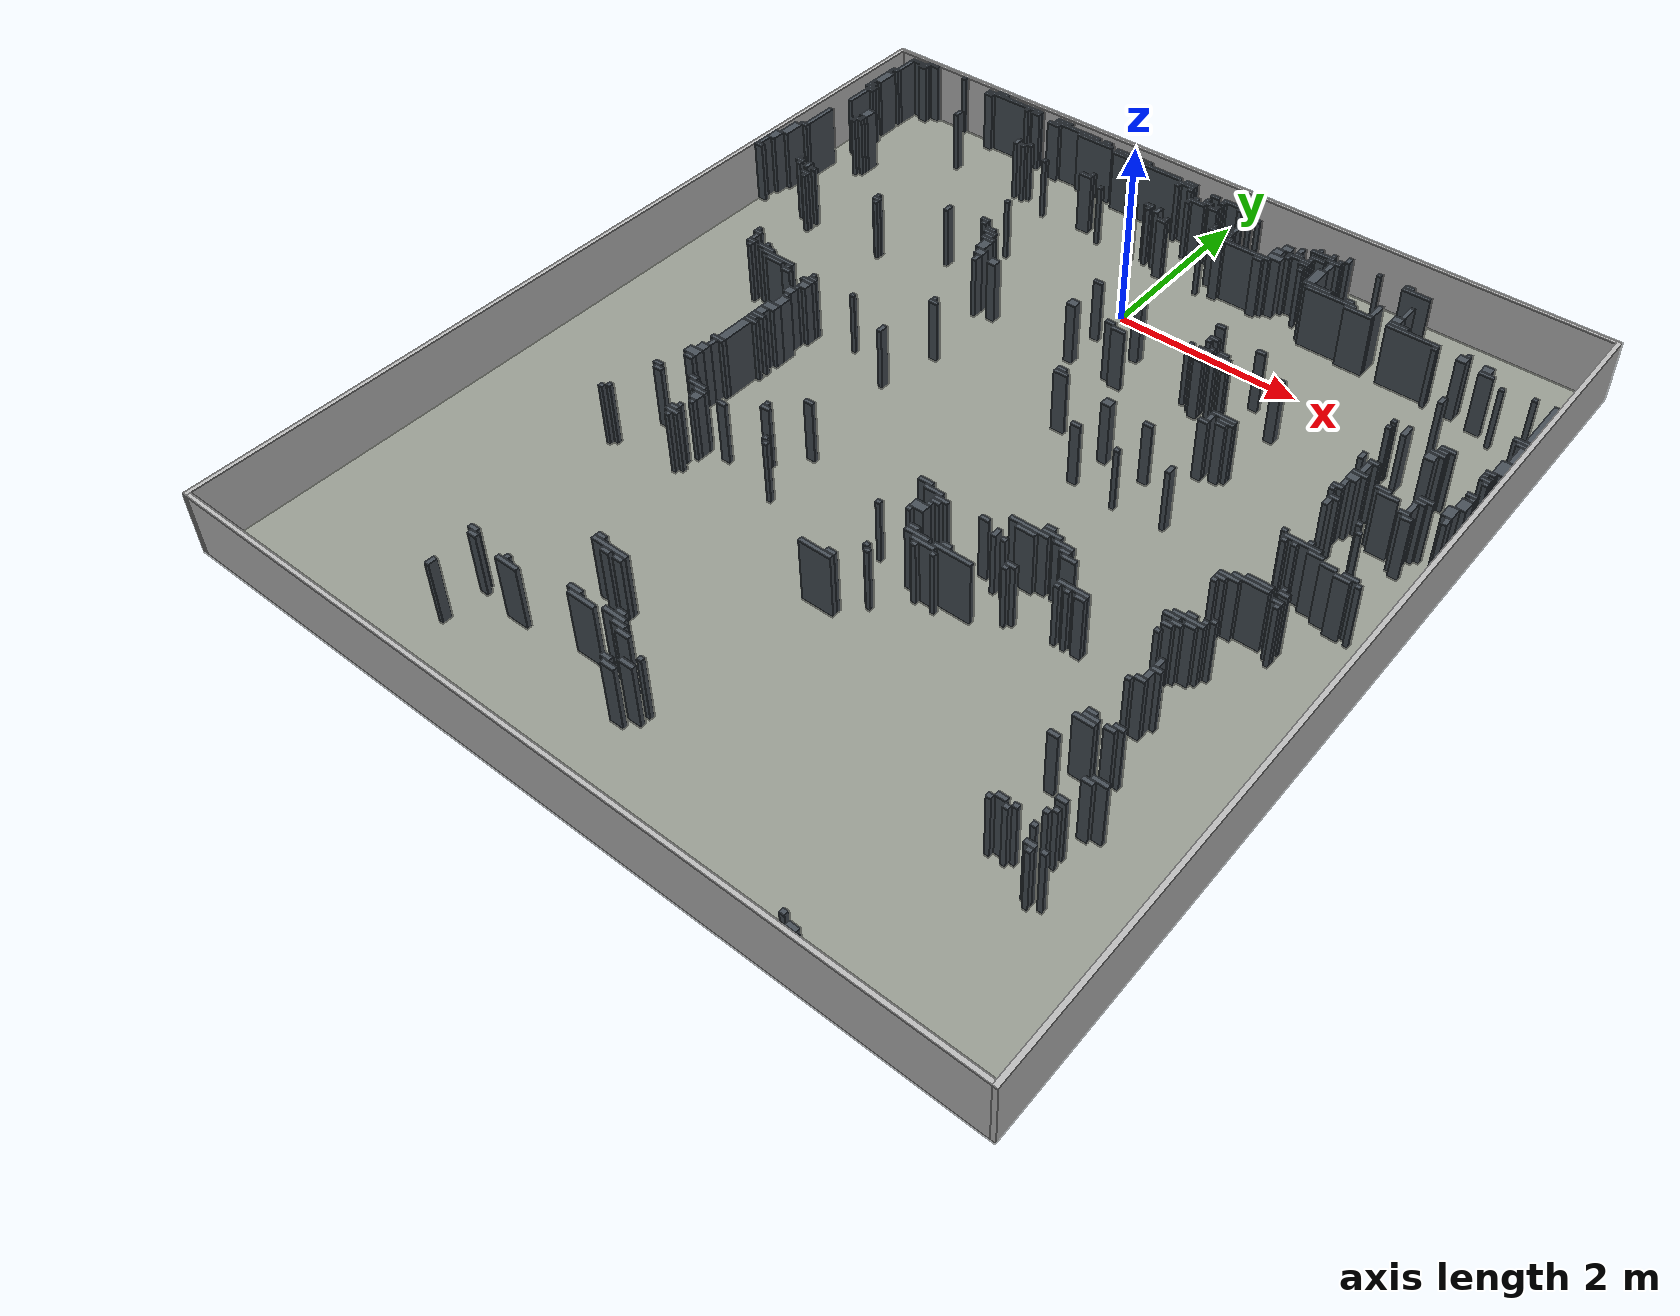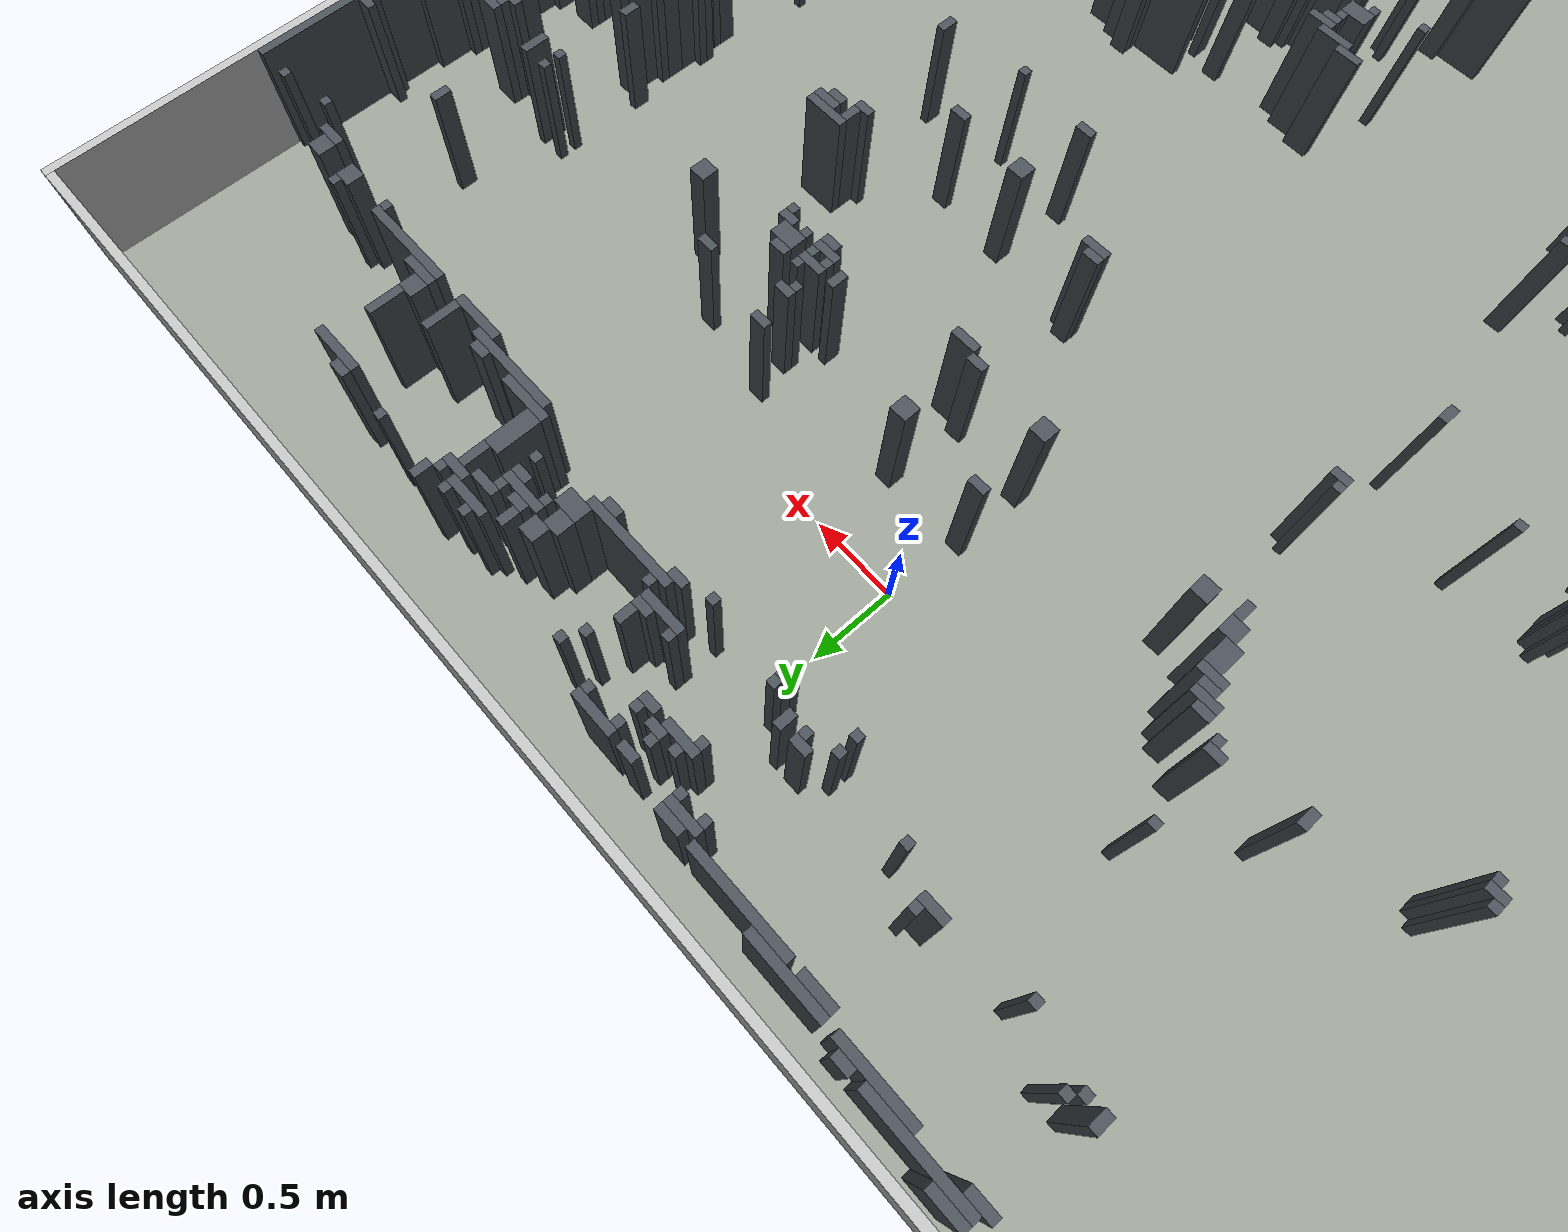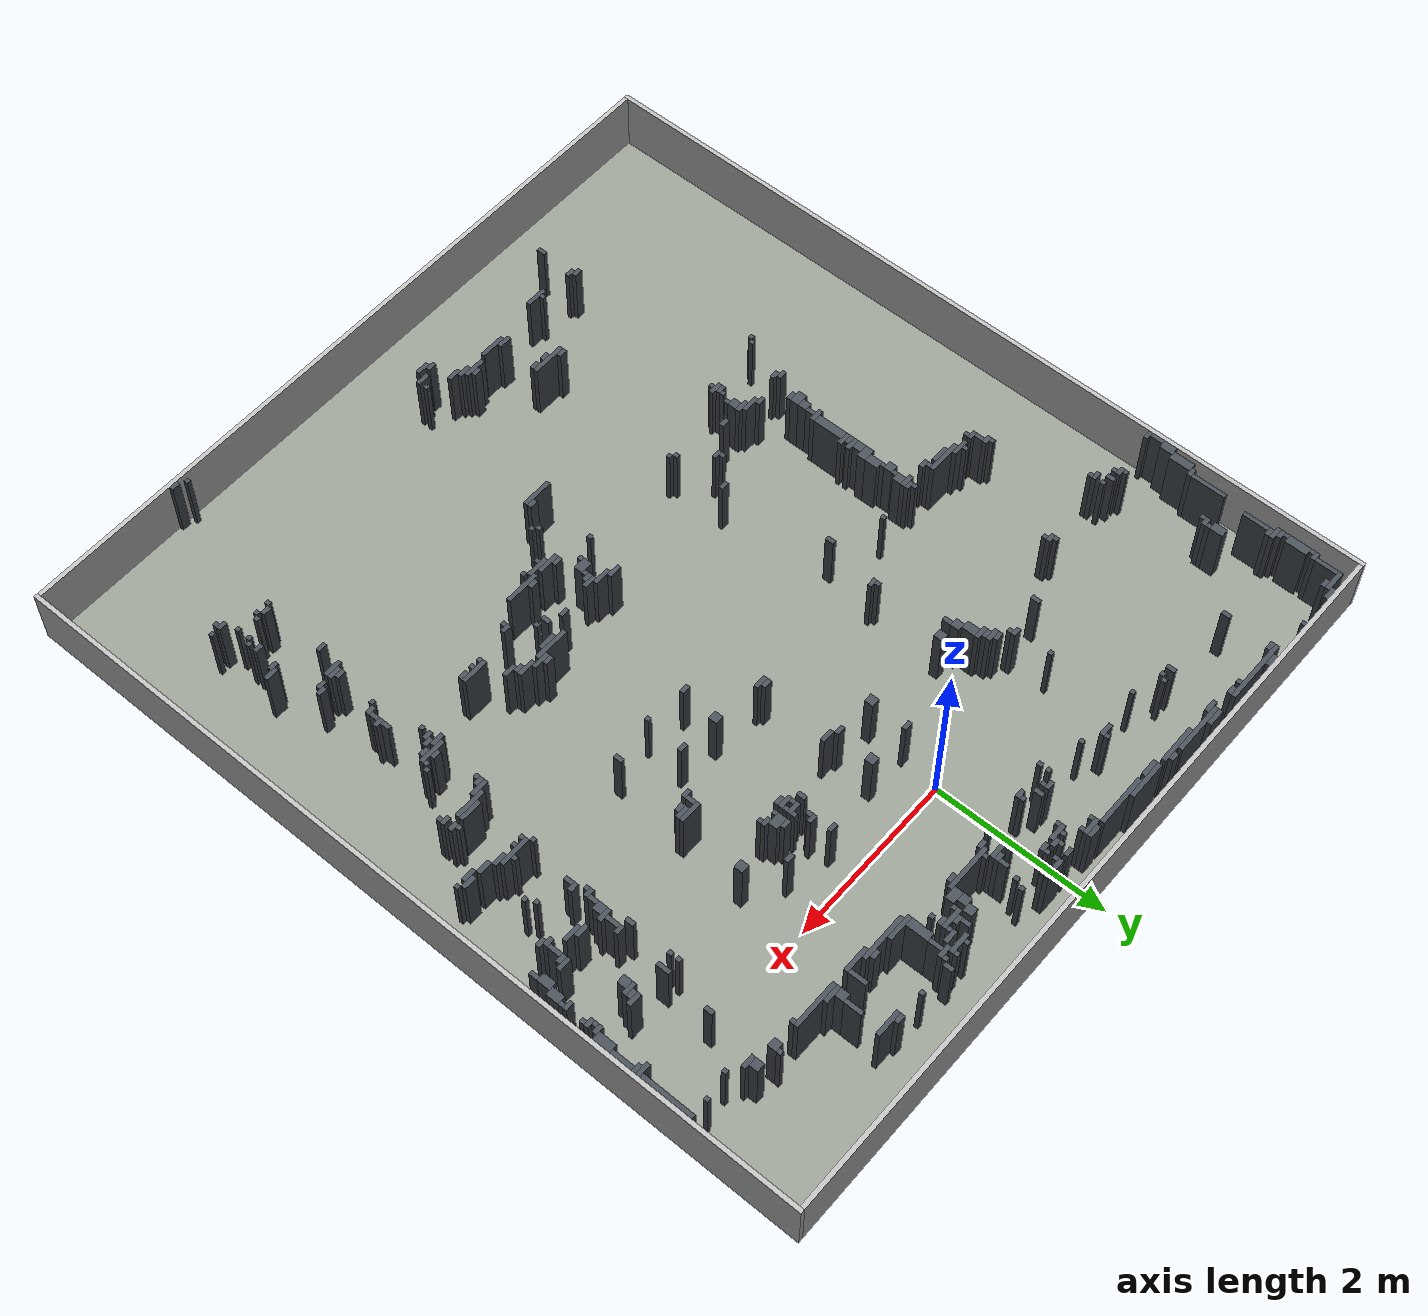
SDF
<?xml version="1.0"?>
<sdf version="1.9">
  <world name="field">
    <physics name="rover_physics" type="ignored">
      <max_step_size>0.002</max_step_size>
      <real_time_factor>1.0</real_time_factor>
    </physics>
    <plugin filename="gz-sim-physics-system" name="gz::sim::systems::Physics"/>
    <plugin filename="gz-sim-user-commands-system" name="gz::sim::systems::UserCommands"/>
    <plugin filename="gz-sim-scene-broadcaster-system" name="gz::sim::systems::SceneBroadcaster"/>
    <plugin filename="gz-sim-sensors-system" name="gz::sim::systems::Sensors"><render_engine>ogre2</render_engine></plugin>
    <plugin filename="gz-sim-imu-system" name="gz::sim::systems::Imu"/>
    <gravity>0 0 -9.81</gravity>
    <light type="directional" name="sun">
      <cast_shadows>true</cast_shadows>
      <pose>0 0 10 0 0 0</pose>
      <diffuse>0.8 0.8 0.8 1</diffuse>
      <specular>0.2 0.2 0.2 1</specular>
      <direction>-0.5 0.2 -0.9</direction>
    </light>
    <model name="field_floor">
      <static>true</static>
      <pose>-0.0330 -2.9500 -0.05 0 0 0</pose>
      <link name="floor">
        <collision name="collision"><geometry><box><size>8.6000 9.5000 0.1</size></box></geometry></collision>
        <visual name="visual"><geometry><box><size>8.6000 9.5000 0.1</size></box></geometry><material><ambient>0.48 0.50 0.46 1</ambient><diffuse>0.58 0.60 0.56 1</diffuse></material></visual>
      </link>
    </model>
    <!-- Generated from map.yaml; 373 occupied rectangles. -->
    <model name="map_obstacles">
      <static>true</static>
      <link name="obstacles">
        <collision name="obstacle_0"><pose>-3.8580 1.7750 0.3500 0 0 0</pose><geometry><box><size>0.1500 0.0500 0.7000</size></box></geometry></collision>
        <visual name="obstacle_0_visual"><pose>-3.8580 1.7750 0.3500 0 0 0</pose><geometry><box><size>0.1500 0.0500 0.7000</size></box></geometry><material><ambient>0.18 0.20 0.22 1</ambient><diffuse>0.27 0.30 0.33 1</diffuse></material></visual>
        <collision name="obstacle_1"><pose>-3.4080 1.7750 0.3500 0 0 0</pose><geometry><box><size>0.0500 0.0500 0.7000</size></box></geometry></collision>
        <visual name="obstacle_1_visual"><pose>-3.4080 1.7750 0.3500 0 0 0</pose><geometry><box><size>0.0500 0.0500 0.7000</size></box></geometry><material><ambient>0.18 0.20 0.22 1</ambient><diffuse>0.27 0.30 0.33 1</diffuse></material></visual>
        <collision name="obstacle_2"><pose>-2.8580 1.7750 0.3500 0 0 0</pose><geometry><box><size>0.1500 0.0500 0.7000</size></box></geometry></collision>
        <visual name="obstacle_2_visual"><pose>-2.8580 1.7750 0.3500 0 0 0</pose><geometry><box><size>0.1500 0.0500 0.7000</size></box></geometry><material><ambient>0.18 0.20 0.22 1</ambient><diffuse>0.27 0.30 0.33 1</diffuse></material></visual>
        <collision name="obstacle_3"><pose>-4.0080 1.7250 0.3500 0 0 0</pose><geometry><box><size>0.2500 0.0500 0.7000</size></box></geometry></collision>
        <visual name="obstacle_3_visual"><pose>-4.0080 1.7250 0.3500 0 0 0</pose><geometry><box><size>0.2500 0.0500 0.7000</size></box></geometry><material><ambient>0.18 0.20 0.22 1</ambient><diffuse>0.27 0.30 0.33 1</diffuse></material></visual>
        <collision name="obstacle_4"><pose>-2.6580 1.7250 0.3500 0 0 0</pose><geometry><box><size>0.7500 0.0500 0.7000</size></box></geometry></collision>
        <visual name="obstacle_4_visual"><pose>-2.6580 1.7250 0.3500 0 0 0</pose><geometry><box><size>0.7500 0.0500 0.7000</size></box></geometry><material><ambient>0.18 0.20 0.22 1</ambient><diffuse>0.27 0.30 0.33 1</diffuse></material></visual>
        <collision name="obstacle_5"><pose>-1.9830 1.7250 0.3500 0 0 0</pose><geometry><box><size>0.2000 0.0500 0.7000</size></box></geometry></collision>
        <visual name="obstacle_5_visual"><pose>-1.9830 1.7250 0.3500 0 0 0</pose><geometry><box><size>0.2000 0.0500 0.7000</size></box></geometry><material><ambient>0.18 0.20 0.22 1</ambient><diffuse>0.27 0.30 0.33 1</diffuse></material></visual>
        <collision name="obstacle_6"><pose>-3.9330 1.6750 0.3500 0 0 0</pose><geometry><box><size>0.1000 0.0500 0.7000</size></box></geometry></collision>
        <visual name="obstacle_6_visual"><pose>-3.9330 1.6750 0.3500 0 0 0</pose><geometry><box><size>0.1000 0.0500 0.7000</size></box></geometry><material><ambient>0.18 0.20 0.22 1</ambient><diffuse>0.27 0.30 0.33 1</diffuse></material></visual>
        <collision name="obstacle_7"><pose>-2.9830 1.6750 0.3500 0 0 0</pose><geometry><box><size>0.1000 0.0500 0.7000</size></box></geometry></collision>
        <visual name="obstacle_7_visual"><pose>-2.9830 1.6750 0.3500 0 0 0</pose><geometry><box><size>0.1000 0.0500 0.7000</size></box></geometry><material><ambient>0.18 0.20 0.22 1</ambient><diffuse>0.27 0.30 0.33 1</diffuse></material></visual>
        <collision name="obstacle_8"><pose>-2.4580 1.6750 0.3500 0 0 0</pose><geometry><box><size>0.0500 0.0500 0.7000</size></box></geometry></collision>
        <visual name="obstacle_8_visual"><pose>-2.4580 1.6750 0.3500 0 0 0</pose><geometry><box><size>0.0500 0.0500 0.7000</size></box></geometry><material><ambient>0.18 0.20 0.22 1</ambient><diffuse>0.27 0.30 0.33 1</diffuse></material></visual>
        <collision name="obstacle_9"><pose>-2.3330 1.6750 0.3500 0 0 0</pose><geometry><box><size>0.1000 0.0500 0.7000</size></box></geometry></collision>
        <visual name="obstacle_9_visual"><pose>-2.3330 1.6750 0.3500 0 0 0</pose><geometry><box><size>0.1000 0.0500 0.7000</size></box></geometry><material><ambient>0.18 0.20 0.22 1</ambient><diffuse>0.27 0.30 0.33 1</diffuse></material></visual>
        <collision name="obstacle_10"><pose>-1.7830 1.6750 0.3500 0 0 0</pose><geometry><box><size>0.6000 0.0500 0.7000</size></box></geometry></collision>
        <visual name="obstacle_10_visual"><pose>-1.7830 1.6750 0.3500 0 0 0</pose><geometry><box><size>0.6000 0.0500 0.7000</size></box></geometry><material><ambient>0.18 0.20 0.22 1</ambient><diffuse>0.27 0.30 0.33 1</diffuse></material></visual>
        <collision name="obstacle_11"><pose>-1.3830 1.6750 0.3500 0 0 0</pose><geometry><box><size>0.1000 0.0500 0.7000</size></box></geometry></collision>
        <visual name="obstacle_11_visual"><pose>-1.3830 1.6750 0.3500 0 0 0</pose><geometry><box><size>0.1000 0.0500 0.7000</size></box></geometry><material><ambient>0.18 0.20 0.22 1</ambient><diffuse>0.27 0.30 0.33 1</diffuse></material></visual>
        <collision name="obstacle_12"><pose>-2.0580 1.6250 0.3500 0 0 0</pose><geometry><box><size>0.1500 0.0500 0.7000</size></box></geometry></collision>
        <visual name="obstacle_12_visual"><pose>-2.0580 1.6250 0.3500 0 0 0</pose><geometry><box><size>0.1500 0.0500 0.7000</size></box></geometry><material><ambient>0.18 0.20 0.22 1</ambient><diffuse>0.27 0.30 0.33 1</diffuse></material></visual>
        <collision name="obstacle_13"><pose>-1.5080 1.6250 0.3500 0 0 0</pose><geometry><box><size>0.4500 0.0500 0.7000</size></box></geometry></collision>
        <visual name="obstacle_13_visual"><pose>-1.5080 1.6250 0.3500 0 0 0</pose><geometry><box><size>0.4500 0.0500 0.7000</size></box></geometry><material><ambient>0.18 0.20 0.22 1</ambient><diffuse>0.27 0.30 0.33 1</diffuse></material></visual>
        <collision name="obstacle_14"><pose>-1.0080 1.6250 0.3500 0 0 0</pose><geometry><box><size>0.4500 0.0500 0.7000</size></box></geometry></collision>
        <visual name="obstacle_14_visual"><pose>-1.0080 1.6250 0.3500 0 0 0</pose><geometry><box><size>0.4500 0.0500 0.7000</size></box></geometry><material><ambient>0.18 0.20 0.22 1</ambient><diffuse>0.27 0.30 0.33 1</diffuse></material></visual>
        <collision name="obstacle_15"><pose>-1.1330 1.5750 0.3500 0 0 0</pose><geometry><box><size>0.2000 0.0500 0.7000</size></box></geometry></collision>
        <visual name="obstacle_15_visual"><pose>-1.1330 1.5750 0.3500 0 0 0</pose><geometry><box><size>0.2000 0.0500 0.7000</size></box></geometry><material><ambient>0.18 0.20 0.22 1</ambient><diffuse>0.27 0.30 0.33 1</diffuse></material></visual>
        <collision name="obstacle_16"><pose>-0.6830 1.5750 0.3500 0 0 0</pose><geometry><box><size>0.6000 0.0500 0.7000</size></box></geometry></collision>
        <visual name="obstacle_16_visual"><pose>-0.6830 1.5750 0.3500 0 0 0</pose><geometry><box><size>0.6000 0.0500 0.7000</size></box></geometry><material><ambient>0.18 0.20 0.22 1</ambient><diffuse>0.27 0.30 0.33 1</diffuse></material></visual>
        <collision name="obstacle_17"><pose>-0.2580 1.5750 0.3500 0 0 0</pose><geometry><box><size>0.1500 0.0500 0.7000</size></box></geometry></collision>
        <visual name="obstacle_17_visual"><pose>-0.2580 1.5750 0.3500 0 0 0</pose><geometry><box><size>0.1500 0.0500 0.7000</size></box></geometry><material><ambient>0.18 0.20 0.22 1</ambient><diffuse>0.27 0.30 0.33 1</diffuse></material></visual>
        <collision name="obstacle_18"><pose>-0.2830 1.5250 0.3500 0 0 0</pose><geometry><box><size>0.2000 0.0500 0.7000</size></box></geometry></collision>
        <visual name="obstacle_18_visual"><pose>-0.2830 1.5250 0.3500 0 0 0</pose><geometry><box><size>0.2000 0.0500 0.7000</size></box></geometry><material><ambient>0.18 0.20 0.22 1</ambient><diffuse>0.27 0.30 0.33 1</diffuse></material></visual>
        <collision name="obstacle_19"><pose>0.0670 1.5250 0.3500 0 0 0</pose><geometry><box><size>0.1000 0.0500 0.7000</size></box></geometry></collision>
        <visual name="obstacle_19_visual"><pose>0.0670 1.5250 0.3500 0 0 0</pose><geometry><box><size>0.1000 0.0500 0.7000</size></box></geometry><material><ambient>0.18 0.20 0.22 1</ambient><diffuse>0.27 0.30 0.33 1</diffuse></material></visual>
        <collision name="obstacle_20"><pose>0.2920 1.5250 0.3500 0 0 0</pose><geometry><box><size>0.2500 0.0500 0.7000</size></box></geometry></collision>
        <visual name="obstacle_20_visual"><pose>0.2920 1.5250 0.3500 0 0 0</pose><geometry><box><size>0.2500 0.0500 0.7000</size></box></geometry><material><ambient>0.18 0.20 0.22 1</ambient><diffuse>0.27 0.30 0.33 1</diffuse></material></visual>
        <collision name="obstacle_21"><pose>-4.1080 1.5750 0.3500 0 0 0</pose><geometry><box><size>0.0500 0.2500 0.7000</size></box></geometry></collision>
        <visual name="obstacle_21_visual"><pose>-4.1080 1.5750 0.3500 0 0 0</pose><geometry><box><size>0.0500 0.2500 0.7000</size></box></geometry><material><ambient>0.18 0.20 0.22 1</ambient><diffuse>0.27 0.30 0.33 1</diffuse></material></visual>
        <collision name="obstacle_22"><pose>-0.3580 1.4750 0.3500 0 0 0</pose><geometry><box><size>0.0500 0.0500 0.7000</size></box></geometry></collision>
        <visual name="obstacle_22_visual"><pose>-0.3580 1.4750 0.3500 0 0 0</pose><geometry><box><size>0.0500 0.0500 0.7000</size></box></geometry><material><ambient>0.18 0.20 0.22 1</ambient><diffuse>0.27 0.30 0.33 1</diffuse></material></visual>
        <collision name="obstacle_23"><pose>-0.2080 1.4750 0.3500 0 0 0</pose><geometry><box><size>0.0500 0.0500 0.7000</size></box></geometry></collision>
        <visual name="obstacle_23_visual"><pose>-0.2080 1.4750 0.3500 0 0 0</pose><geometry><box><size>0.0500 0.0500 0.7000</size></box></geometry><material><ambient>0.18 0.20 0.22 1</ambient><diffuse>0.27 0.30 0.33 1</diffuse></material></visual>
        <collision name="obstacle_24"><pose>0.1920 1.4750 0.3500 0 0 0</pose><geometry><box><size>0.0500 0.0500 0.7000</size></box></geometry></collision>
        <visual name="obstacle_24_visual"><pose>0.1920 1.4750 0.3500 0 0 0</pose><geometry><box><size>0.0500 0.0500 0.7000</size></box></geometry><material><ambient>0.18 0.20 0.22 1</ambient><diffuse>0.27 0.30 0.33 1</diffuse></material></visual>
        <collision name="obstacle_25"><pose>0.3920 1.4750 0.3500 0 0 0</pose><geometry><box><size>0.0500 0.0500 0.7000</size></box></geometry></collision>
        <visual name="obstacle_25_visual"><pose>0.3920 1.4750 0.3500 0 0 0</pose><geometry><box><size>0.0500 0.0500 0.7000</size></box></geometry><material><ambient>0.18 0.20 0.22 1</ambient><diffuse>0.27 0.30 0.33 1</diffuse></material></visual>
        <collision name="obstacle_26"><pose>-4.1330 1.4250 0.3500 0 0 0</pose><geometry><box><size>0.1000 0.0500 0.7000</size></box></geometry></collision>
        <visual name="obstacle_26_visual"><pose>-4.1330 1.4250 0.3500 0 0 0</pose><geometry><box><size>0.1000 0.0500 0.7000</size></box></geometry><material><ambient>0.18 0.20 0.22 1</ambient><diffuse>0.27 0.30 0.33 1</diffuse></material></visual>
        <collision name="obstacle_27"><pose>0.0420 1.4250 0.3500 0 0 0</pose><geometry><box><size>0.0500 0.0500 0.7000</size></box></geometry></collision>
        <visual name="obstacle_27_visual"><pose>0.0420 1.4250 0.3500 0 0 0</pose><geometry><box><size>0.0500 0.0500 0.7000</size></box></geometry><material><ambient>0.18 0.20 0.22 1</ambient><diffuse>0.27 0.30 0.33 1</diffuse></material></visual>
        <collision name="obstacle_28"><pose>0.6420 1.4250 0.3500 0 0 0</pose><geometry><box><size>0.0500 0.0500 0.7000</size></box></geometry></collision>
        <visual name="obstacle_28_visual"><pose>0.6420 1.4250 0.3500 0 0 0</pose><geometry><box><size>0.0500 0.0500 0.7000</size></box></geometry><material><ambient>0.18 0.20 0.22 1</ambient><diffuse>0.27 0.30 0.33 1</diffuse></material></visual>
        <collision name="obstacle_29"><pose>-4.1580 1.3750 0.3500 0 0 0</pose><geometry><box><size>0.0500 0.0500 0.7000</size></box></geometry></collision>
        <visual name="obstacle_29_visual"><pose>-4.1580 1.3750 0.3500 0 0 0</pose><geometry><box><size>0.0500 0.0500 0.7000</size></box></geometry><material><ambient>0.18 0.20 0.22 1</ambient><diffuse>0.27 0.30 0.33 1</diffuse></material></visual>
        <collision name="obstacle_30"><pose>-0.0580 1.3750 0.3500 0 0 0</pose><geometry><box><size>0.0500 0.0500 0.7000</size></box></geometry></collision>
        <visual name="obstacle_30_visual"><pose>-0.0580 1.3750 0.3500 0 0 0</pose><geometry><box><size>0.0500 0.0500 0.7000</size></box></geometry><material><ambient>0.18 0.20 0.22 1</ambient><diffuse>0.27 0.30 0.33 1</diffuse></material></visual>
        <collision name="obstacle_31"><pose>0.0670 1.3750 0.3500 0 0 0</pose><geometry><box><size>0.1000 0.0500 0.7000</size></box></geometry></collision>
        <visual name="obstacle_31_visual"><pose>0.0670 1.3750 0.3500 0 0 0</pose><geometry><box><size>0.1000 0.0500 0.7000</size></box></geometry><material><ambient>0.18 0.20 0.22 1</ambient><diffuse>0.27 0.30 0.33 1</diffuse></material></visual>
        <collision name="obstacle_32"><pose>0.1920 1.3750 0.3500 0 0 0</pose><geometry><box><size>0.0500 0.0500 0.7000</size></box></geometry></collision>
        <visual name="obstacle_32_visual"><pose>0.1920 1.3750 0.3500 0 0 0</pose><geometry><box><size>0.0500 0.0500 0.7000</size></box></geometry><material><ambient>0.18 0.20 0.22 1</ambient><diffuse>0.27 0.30 0.33 1</diffuse></material></visual>
        <collision name="obstacle_33"><pose>1.3920 1.3750 0.3500 0 0 0</pose><geometry><box><size>0.0500 0.0500 0.7000</size></box></geometry></collision>
        <visual name="obstacle_33_visual"><pose>1.3920 1.3750 0.3500 0 0 0</pose><geometry><box><size>0.0500 0.0500 0.7000</size></box></geometry><material><ambient>0.18 0.20 0.22 1</ambient><diffuse>0.27 0.30 0.33 1</diffuse></material></visual>
        <collision name="obstacle_34"><pose>1.5420 1.3750 0.3500 0 0 0</pose><geometry><box><size>0.0500 0.0500 0.7000</size></box></geometry></collision>
        <visual name="obstacle_34_visual"><pose>1.5420 1.3750 0.3500 0 0 0</pose><geometry><box><size>0.0500 0.0500 0.7000</size></box></geometry><material><ambient>0.18 0.20 0.22 1</ambient><diffuse>0.27 0.30 0.33 1</diffuse></material></visual>
        <collision name="obstacle_35"><pose>1.6920 1.4000 0.3500 0 0 0</pose><geometry><box><size>0.0500 0.1000 0.7000</size></box></geometry></collision>
        <visual name="obstacle_35_visual"><pose>1.6920 1.4000 0.3500 0 0 0</pose><geometry><box><size>0.0500 0.1000 0.7000</size></box></geometry><material><ambient>0.18 0.20 0.22 1</ambient><diffuse>0.27 0.30 0.33 1</diffuse></material></visual>
        <collision name="obstacle_36"><pose>2.0420 1.3750 0.3500 0 0 0</pose><geometry><box><size>0.0500 0.0500 0.7000</size></box></geometry></collision>
        <visual name="obstacle_36_visual"><pose>2.0420 1.3750 0.3500 0 0 0</pose><geometry><box><size>0.0500 0.0500 0.7000</size></box></geometry><material><ambient>0.18 0.20 0.22 1</ambient><diffuse>0.27 0.30 0.33 1</diffuse></material></visual>
        <collision name="obstacle_37"><pose>2.3670 1.3750 0.3500 0 0 0</pose><geometry><box><size>0.1000 0.0500 0.7000</size></box></geometry></collision>
        <visual name="obstacle_37_visual"><pose>2.3670 1.3750 0.3500 0 0 0</pose><geometry><box><size>0.1000 0.0500 0.7000</size></box></geometry><material><ambient>0.18 0.20 0.22 1</ambient><diffuse>0.27 0.30 0.33 1</diffuse></material></visual>
        <collision name="obstacle_38"><pose>-0.0330 1.3250 0.3500 0 0 0</pose><geometry><box><size>0.2000 0.0500 0.7000</size></box></geometry></collision>
        <visual name="obstacle_38_visual"><pose>-0.0330 1.3250 0.3500 0 0 0</pose><geometry><box><size>0.2000 0.0500 0.7000</size></box></geometry><material><ambient>0.18 0.20 0.22 1</ambient><diffuse>0.27 0.30 0.33 1</diffuse></material></visual>
        <collision name="obstacle_39"><pose>0.1670 1.3250 0.3500 0 0 0</pose><geometry><box><size>0.1000 0.0500 0.7000</size></box></geometry></collision>
        <visual name="obstacle_39_visual"><pose>0.1670 1.3250 0.3500 0 0 0</pose><geometry><box><size>0.1000 0.0500 0.7000</size></box></geometry><material><ambient>0.18 0.20 0.22 1</ambient><diffuse>0.27 0.30 0.33 1</diffuse></material></visual>
        <collision name="obstacle_40"><pose>0.5920 1.3250 0.3500 0 0 0</pose><geometry><box><size>0.0500 0.0500 0.7000</size></box></geometry></collision>
        <visual name="obstacle_40_visual"><pose>0.5920 1.3250 0.3500 0 0 0</pose><geometry><box><size>0.0500 0.0500 0.7000</size></box></geometry><material><ambient>0.18 0.20 0.22 1</ambient><diffuse>0.27 0.30 0.33 1</diffuse></material></visual>
        <collision name="obstacle_41"><pose>1.4420 1.3250 0.3500 0 0 0</pose><geometry><box><size>0.2500 0.0500 0.7000</size></box></geometry></collision>
        <visual name="obstacle_41_visual"><pose>1.4420 1.3250 0.3500 0 0 0</pose><geometry><box><size>0.2500 0.0500 0.7000</size></box></geometry><material><ambient>0.18 0.20 0.22 1</ambient><diffuse>0.27 0.30 0.33 1</diffuse></material></visual>
        <collision name="obstacle_42"><pose>1.6420 1.3250 0.3500 0 0 0</pose><geometry><box><size>0.0500 0.0500 0.7000</size></box></geometry></collision>
        <visual name="obstacle_42_visual"><pose>1.6420 1.3250 0.3500 0 0 0</pose><geometry><box><size>0.0500 0.0500 0.7000</size></box></geometry><material><ambient>0.18 0.20 0.22 1</ambient><diffuse>0.27 0.30 0.33 1</diffuse></material></visual>
        <collision name="obstacle_43"><pose>2.4670 1.3250 0.3500 0 0 0</pose><geometry><box><size>0.3000 0.0500 0.7000</size></box></geometry></collision>
        <visual name="obstacle_43_visual"><pose>2.4670 1.3250 0.3500 0 0 0</pose><geometry><box><size>0.3000 0.0500 0.7000</size></box></geometry><material><ambient>0.18 0.20 0.22 1</ambient><diffuse>0.27 0.30 0.33 1</diffuse></material></visual>
        <collision name="obstacle_44"><pose>-0.1080 1.2750 0.3500 0 0 0</pose><geometry><box><size>0.0500 0.0500 0.7000</size></box></geometry></collision>
        <visual name="obstacle_44_visual"><pose>-0.1080 1.2750 0.3500 0 0 0</pose><geometry><box><size>0.0500 0.0500 0.7000</size></box></geometry><material><ambient>0.18 0.20 0.22 1</ambient><diffuse>0.27 0.30 0.33 1</diffuse></material></visual>
        <collision name="obstacle_45"><pose>1.5920 1.2750 0.3500 0 0 0</pose><geometry><box><size>0.1500 0.0500 0.7000</size></box></geometry></collision>
        <visual name="obstacle_45_visual"><pose>1.5920 1.2750 0.3500 0 0 0</pose><geometry><box><size>0.1500 0.0500 0.7000</size></box></geometry><material><ambient>0.18 0.20 0.22 1</ambient><diffuse>0.27 0.30 0.33 1</diffuse></material></visual>
        <collision name="obstacle_46"><pose>1.2420 1.2500 0.3500 0 0 0</pose><geometry><box><size>0.0500 0.1000 0.7000</size></box></geometry></collision>
        <visual name="obstacle_46_visual"><pose>1.2420 1.2500 0.3500 0 0 0</pose><geometry><box><size>0.0500 0.1000 0.7000</size></box></geometry><material><ambient>0.18 0.20 0.22 1</ambient><diffuse>0.27 0.30 0.33 1</diffuse></material></visual>
        <collision name="obstacle_47"><pose>1.4420 1.2250 0.3500 0 0 0</pose><geometry><box><size>0.1500 0.0500 0.7000</size></box></geometry></collision>
        <visual name="obstacle_47_visual"><pose>1.4420 1.2250 0.3500 0 0 0</pose><geometry><box><size>0.1500 0.0500 0.7000</size></box></geometry><material><ambient>0.18 0.20 0.22 1</ambient><diffuse>0.27 0.30 0.33 1</diffuse></material></visual>
        <collision name="obstacle_48"><pose>1.1170 1.2000 0.3500 0 0 0</pose><geometry><box><size>0.1000 0.1000 0.7000</size></box></geometry></collision>
        <visual name="obstacle_48_visual"><pose>1.1170 1.2000 0.3500 0 0 0</pose><geometry><box><size>0.1000 0.1000 0.7000</size></box></geometry><material><ambient>0.18 0.20 0.22 1</ambient><diffuse>0.27 0.30 0.33 1</diffuse></material></visual>
        <collision name="obstacle_49"><pose>1.2670 1.1750 0.3500 0 0 0</pose><geometry><box><size>0.1000 0.0500 0.7000</size></box></geometry></collision>
        <visual name="obstacle_49_visual"><pose>1.2670 1.1750 0.3500 0 0 0</pose><geometry><box><size>0.1000 0.0500 0.7000</size></box></geometry><material><ambient>0.18 0.20 0.22 1</ambient><diffuse>0.27 0.30 0.33 1</diffuse></material></visual>
        <collision name="obstacle_50"><pose>1.3920 1.1750 0.3500 0 0 0</pose><geometry><box><size>0.0500 0.0500 0.7000</size></box></geometry></collision>
        <visual name="obstacle_50_visual"><pose>1.3920 1.1750 0.3500 0 0 0</pose><geometry><box><size>0.0500 0.0500 0.7000</size></box></geometry><material><ambient>0.18 0.20 0.22 1</ambient><diffuse>0.27 0.30 0.33 1</diffuse></material></visual>
        <collision name="obstacle_51"><pose>-4.1330 1.2250 0.3500 0 0 0</pose><geometry><box><size>0.1000 0.2500 0.7000</size></box></geometry></collision>
        <visual name="obstacle_51_visual"><pose>-4.1330 1.2250 0.3500 0 0 0</pose><geometry><box><size>0.1000 0.2500 0.7000</size></box></geometry><material><ambient>0.18 0.20 0.22 1</ambient><diffuse>0.27 0.30 0.33 1</diffuse></material></visual>
        <collision name="obstacle_52"><pose>-3.0080 1.1500 0.3500 0 0 0</pose><geometry><box><size>0.0500 0.1000 0.7000</size></box></geometry></collision>
        <visual name="obstacle_52_visual"><pose>-3.0080 1.1500 0.3500 0 0 0</pose><geometry><box><size>0.0500 0.1000 0.7000</size></box></geometry><material><ambient>0.18 0.20 0.22 1</ambient><diffuse>0.27 0.30 0.33 1</diffuse></material></visual>
        <collision name="obstacle_53"><pose>-2.0080 1.1250 0.3500 0 0 0</pose><geometry><box><size>0.0500 0.0500 0.7000</size></box></geometry></collision>
        <visual name="obstacle_53_visual"><pose>-2.0080 1.1250 0.3500 0 0 0</pose><geometry><box><size>0.0500 0.0500 0.7000</size></box></geometry><material><ambient>0.18 0.20 0.22 1</ambient><diffuse>0.27 0.30 0.33 1</diffuse></material></visual>
        <collision name="obstacle_54"><pose>0.5420 1.1500 0.3500 0 0 0</pose><geometry><box><size>0.0500 0.1000 0.7000</size></box></geometry></collision>
        <visual name="obstacle_54_visual"><pose>0.5420 1.1500 0.3500 0 0 0</pose><geometry><box><size>0.0500 0.1000 0.7000</size></box></geometry><material><ambient>0.18 0.20 0.22 1</ambient><diffuse>0.27 0.30 0.33 1</diffuse></material></visual>
        <collision name="obstacle_55"><pose>1.2920 1.1250 0.3500 0 0 0</pose><geometry><box><size>0.2500 0.0500 0.7000</size></box></geometry></collision>
        <visual name="obstacle_55_visual"><pose>1.2920 1.1250 0.3500 0 0 0</pose><geometry><box><size>0.2500 0.0500 0.7000</size></box></geometry><material><ambient>0.18 0.20 0.22 1</ambient><diffuse>0.27 0.30 0.33 1</diffuse></material></visual>
        <collision name="obstacle_56"><pose>1.5920 1.1750 0.3500 0 0 0</pose><geometry><box><size>0.0500 0.1500 0.7000</size></box></geometry></collision>
        <visual name="obstacle_56_visual"><pose>1.5920 1.1750 0.3500 0 0 0</pose><geometry><box><size>0.0500 0.1500 0.7000</size></box></geometry><material><ambient>0.18 0.20 0.22 1</ambient><diffuse>0.27 0.30 0.33 1</diffuse></material></visual>
        <collision name="obstacle_57"><pose>-4.1580 1.0750 0.3500 0 0 0</pose><geometry><box><size>0.0500 0.0500 0.7000</size></box></geometry></collision>
        <visual name="obstacle_57_visual"><pose>-4.1580 1.0750 0.3500 0 0 0</pose><geometry><box><size>0.0500 0.0500 0.7000</size></box></geometry><material><ambient>0.18 0.20 0.22 1</ambient><diffuse>0.27 0.30 0.33 1</diffuse></material></visual>
        <collision name="obstacle_58"><pose>-2.1580 1.1000 0.3500 0 0 0</pose><geometry><box><size>0.0500 0.1000 0.7000</size></box></geometry></collision>
        <visual name="obstacle_58_visual"><pose>-2.1580 1.1000 0.3500 0 0 0</pose><geometry><box><size>0.0500 0.1000 0.7000</size></box></geometry><material><ambient>0.18 0.20 0.22 1</ambient><diffuse>0.27 0.30 0.33 1</diffuse></material></visual>
        <collision name="obstacle_59"><pose>-2.0580 1.0750 0.3500 0 0 0</pose><geometry><box><size>0.0500 0.0500 0.7000</size></box></geometry></collision>
        <visual name="obstacle_59_visual"><pose>-2.0580 1.0750 0.3500 0 0 0</pose><geometry><box><size>0.0500 0.0500 0.7000</size></box></geometry><material><ambient>0.18 0.20 0.22 1</ambient><diffuse>0.27 0.30 0.33 1</diffuse></material></visual>
        <collision name="obstacle_60"><pose>-1.1580 1.0750 0.3500 0 0 0</pose><geometry><box><size>0.0500 0.0500 0.7000</size></box></geometry></collision>
        <visual name="obstacle_60_visual"><pose>-1.1580 1.0750 0.3500 0 0 0</pose><geometry><box><size>0.0500 0.0500 0.7000</size></box></geometry><material><ambient>0.18 0.20 0.22 1</ambient><diffuse>0.27 0.30 0.33 1</diffuse></material></visual>
        <collision name="obstacle_61"><pose>0.3420 1.0750 0.3500 0 0 0</pose><geometry><box><size>0.0500 0.0500 0.7000</size></box></geometry></collision>
        <visual name="obstacle_61_visual"><pose>0.3420 1.0750 0.3500 0 0 0</pose><geometry><box><size>0.0500 0.0500 0.7000</size></box></geometry><material><ambient>0.18 0.20 0.22 1</ambient><diffuse>0.27 0.30 0.33 1</diffuse></material></visual>
        <collision name="obstacle_62"><pose>0.5170 1.0750 0.3500 0 0 0</pose><geometry><box><size>0.1000 0.0500 0.7000</size></box></geometry></collision>
        <visual name="obstacle_62_visual"><pose>0.5170 1.0750 0.3500 0 0 0</pose><geometry><box><size>0.1000 0.0500 0.7000</size></box></geometry><material><ambient>0.18 0.20 0.22 1</ambient><diffuse>0.27 0.30 0.33 1</diffuse></material></visual>
        <collision name="obstacle_63"><pose>1.0670 1.1000 0.3500 0 0 0</pose><geometry><box><size>0.1000 0.1000 0.7000</size></box></geometry></collision>
        <visual name="obstacle_63_visual"><pose>1.0670 1.1000 0.3500 0 0 0</pose><geometry><box><size>0.1000 0.1000 0.7000</size></box></geometry><material><ambient>0.18 0.20 0.22 1</ambient><diffuse>0.27 0.30 0.33 1</diffuse></material></visual>
        <collision name="obstacle_64"><pose>1.1920 1.0750 0.3500 0 0 0</pose><geometry><box><size>0.0500 0.0500 0.7000</size></box></geometry></collision>
        <visual name="obstacle_64_visual"><pose>1.1920 1.0750 0.3500 0 0 0</pose><geometry><box><size>0.0500 0.0500 0.7000</size></box></geometry><material><ambient>0.18 0.20 0.22 1</ambient><diffuse>0.27 0.30 0.33 1</diffuse></material></visual>
        <collision name="obstacle_65"><pose>1.3670 1.0750 0.3500 0 0 0</pose><geometry><box><size>0.1000 0.0500 0.7000</size></box></geometry></collision>
        <visual name="obstacle_65_visual"><pose>1.3670 1.0750 0.3500 0 0 0</pose><geometry><box><size>0.1000 0.0500 0.7000</size></box></geometry><material><ambient>0.18 0.20 0.22 1</ambient><diffuse>0.27 0.30 0.33 1</diffuse></material></visual>
        <collision name="obstacle_66"><pose>-4.1330 1.0250 0.3500 0 0 0</pose><geometry><box><size>0.1000 0.0500 0.7000</size></box></geometry></collision>
        <visual name="obstacle_66_visual"><pose>-4.1330 1.0250 0.3500 0 0 0</pose><geometry><box><size>0.1000 0.0500 0.7000</size></box></geometry><material><ambient>0.18 0.20 0.22 1</ambient><diffuse>0.27 0.30 0.33 1</diffuse></material></visual>
        <collision name="obstacle_67"><pose>-1.2080 1.0250 0.3500 0 0 0</pose><geometry><box><size>0.1500 0.0500 0.7000</size></box></geometry></collision>
        <visual name="obstacle_67_visual"><pose>-1.2080 1.0250 0.3500 0 0 0</pose><geometry><box><size>0.1500 0.0500 0.7000</size></box></geometry><material><ambient>0.18 0.20 0.22 1</ambient><diffuse>0.27 0.30 0.33 1</diffuse></material></visual>
        <collision name="obstacle_68"><pose>0.4420 1.0250 0.3500 0 0 0</pose><geometry><box><size>0.2500 0.0500 0.7000</size></box></geometry></collision>
        <visual name="obstacle_68_visual"><pose>0.4420 1.0250 0.3500 0 0 0</pose><geometry><box><size>0.2500 0.0500 0.7000</size></box></geometry><material><ambient>0.18 0.20 0.22 1</ambient><diffuse>0.27 0.30 0.33 1</diffuse></material></visual>
        <collision name="obstacle_69"><pose>-4.1080 0.9750 0.3500 0 0 0</pose><geometry><box><size>0.1500 0.0500 0.7000</size></box></geometry></collision>
        <visual name="obstacle_69_visual"><pose>-4.1080 0.9750 0.3500 0 0 0</pose><geometry><box><size>0.1500 0.0500 0.7000</size></box></geometry><material><ambient>0.18 0.20 0.22 1</ambient><diffuse>0.27 0.30 0.33 1</diffuse></material></visual>
        <collision name="obstacle_70"><pose>-1.7080 0.9750 0.3500 0 0 0</pose><geometry><box><size>0.0500 0.0500 0.7000</size></box></geometry></collision>
        <visual name="obstacle_70_visual"><pose>-1.7080 0.9750 0.3500 0 0 0</pose><geometry><box><size>0.0500 0.0500 0.7000</size></box></geometry><material><ambient>0.18 0.20 0.22 1</ambient><diffuse>0.27 0.30 0.33 1</diffuse></material></visual>
        <collision name="obstacle_71"><pose>-0.3830 0.9750 0.3500 0 0 0</pose><geometry><box><size>0.1000 0.0500 0.7000</size></box></geometry></collision>
        <visual name="obstacle_71_visual"><pose>-0.3830 0.9750 0.3500 0 0 0</pose><geometry><box><size>0.1000 0.0500 0.7000</size></box></geometry><material><ambient>0.18 0.20 0.22 1</ambient><diffuse>0.27 0.30 0.33 1</diffuse></material></visual>
        <collision name="obstacle_72"><pose>0.5920 0.9750 0.3500 0 0 0</pose><geometry><box><size>0.0500 0.0500 0.7000</size></box></geometry></collision>
        <visual name="obstacle_72_visual"><pose>0.5920 0.9750 0.3500 0 0 0</pose><geometry><box><size>0.0500 0.0500 0.7000</size></box></geometry><material><ambient>0.18 0.20 0.22 1</ambient><diffuse>0.27 0.30 0.33 1</diffuse></material></visual>
        <collision name="obstacle_73"><pose>1.0920 1.0000 0.3500 0 0 0</pose><geometry><box><size>0.1500 0.1000 0.7000</size></box></geometry></collision>
        <visual name="obstacle_73_visual"><pose>1.0920 1.0000 0.3500 0 0 0</pose><geometry><box><size>0.1500 0.1000 0.7000</size></box></geometry><material><ambient>0.18 0.20 0.22 1</ambient><diffuse>0.27 0.30 0.33 1</diffuse></material></visual>
        <collision name="obstacle_74"><pose>1.3920 0.9750 0.3500 0 0 0</pose><geometry><box><size>0.0500 0.0500 0.7000</size></box></geometry></collision>
        <visual name="obstacle_74_visual"><pose>1.3920 0.9750 0.3500 0 0 0</pose><geometry><box><size>0.0500 0.0500 0.7000</size></box></geometry><material><ambient>0.18 0.20 0.22 1</ambient><diffuse>0.27 0.30 0.33 1</diffuse></material></visual>
        <collision name="obstacle_75"><pose>-4.0830 0.9250 0.3500 0 0 0</pose><geometry><box><size>0.1000 0.0500 0.7000</size></box></geometry></collision>
        <visual name="obstacle_75_visual"><pose>-4.0830 0.9250 0.3500 0 0 0</pose><geometry><box><size>0.1000 0.0500 0.7000</size></box></geometry><material><ambient>0.18 0.20 0.22 1</ambient><diffuse>0.27 0.30 0.33 1</diffuse></material></visual>
        <collision name="obstacle_76"><pose>-0.9580 0.9250 0.3500 0 0 0</pose><geometry><box><size>0.0500 0.0500 0.7000</size></box></geometry></collision>
        <visual name="obstacle_76_visual"><pose>-0.9580 0.9250 0.3500 0 0 0</pose><geometry><box><size>0.0500 0.0500 0.7000</size></box></geometry><material><ambient>0.18 0.20 0.22 1</ambient><diffuse>0.27 0.30 0.33 1</diffuse></material></visual>
        <collision name="obstacle_77"><pose>-0.3580 0.9250 0.3500 0 0 0</pose><geometry><box><size>0.0500 0.0500 0.7000</size></box></geometry></collision>
        <visual name="obstacle_77_visual"><pose>-0.3580 0.9250 0.3500 0 0 0</pose><geometry><box><size>0.0500 0.0500 0.7000</size></box></geometry><material><ambient>0.18 0.20 0.22 1</ambient><diffuse>0.27 0.30 0.33 1</diffuse></material></visual>
        <collision name="obstacle_78"><pose>-0.2580 0.9500 0.3500 0 0 0</pose><geometry><box><size>0.0500 0.1000 0.7000</size></box></geometry></collision>
        <visual name="obstacle_78_visual"><pose>-0.2580 0.9500 0.3500 0 0 0</pose><geometry><box><size>0.0500 0.1000 0.7000</size></box></geometry><material><ambient>0.18 0.20 0.22 1</ambient><diffuse>0.27 0.30 0.33 1</diffuse></material></visual>
        <collision name="obstacle_79"><pose>0.7920 0.9250 0.3500 0 0 0</pose><geometry><box><size>0.5500 0.0500 0.7000</size></box></geometry></collision>
        <visual name="obstacle_79_visual"><pose>0.7920 0.9250 0.3500 0 0 0</pose><geometry><box><size>0.5500 0.0500 0.7000</size></box></geometry><material><ambient>0.18 0.20 0.22 1</ambient><diffuse>0.27 0.30 0.33 1</diffuse></material></visual>
        <collision name="obstacle_80"><pose>2.5420 1.0000 0.3500 0 0 0</pose><geometry><box><size>0.0500 0.2000 0.7000</size></box></geometry></collision>
        <visual name="obstacle_80_visual"><pose>2.5420 1.0000 0.3500 0 0 0</pose><geometry><box><size>0.0500 0.2000 0.7000</size></box></geometry><material><ambient>0.18 0.20 0.22 1</ambient><diffuse>0.27 0.30 0.33 1</diffuse></material></visual>
        <collision name="obstacle_81"><pose>-0.5080 0.8750 0.3500 0 0 0</pose><geometry><box><size>0.0500 0.0500 0.7000</size></box></geometry></collision>
        <visual name="obstacle_81_visual"><pose>-0.5080 0.8750 0.3500 0 0 0</pose><geometry><box><size>0.0500 0.0500 0.7000</size></box></geometry><material><ambient>0.18 0.20 0.22 1</ambient><diffuse>0.27 0.30 0.33 1</diffuse></material></visual>
        <collision name="obstacle_82"><pose>-0.1080 0.8750 0.3500 0 0 0</pose><geometry><box><size>0.0500 0.0500 0.7000</size></box></geometry></collision>
        <visual name="obstacle_82_visual"><pose>-0.1080 0.8750 0.3500 0 0 0</pose><geometry><box><size>0.0500 0.0500 0.7000</size></box></geometry><material><ambient>0.18 0.20 0.22 1</ambient><diffuse>0.27 0.30 0.33 1</diffuse></material></visual>
        <collision name="obstacle_83"><pose>0.5170 0.8750 0.3500 0 0 0</pose><geometry><box><size>0.1000 0.0500 0.7000</size></box></geometry></collision>
        <visual name="obstacle_83_visual"><pose>0.5170 0.8750 0.3500 0 0 0</pose><geometry><box><size>0.1000 0.0500 0.7000</size></box></geometry><material><ambient>0.18 0.20 0.22 1</ambient><diffuse>0.27 0.30 0.33 1</diffuse></material></visual>
        <collision name="obstacle_84"><pose>0.9670 0.8750 0.3500 0 0 0</pose><geometry><box><size>0.1000 0.0500 0.7000</size></box></geometry></collision>
        <visual name="obstacle_84_visual"><pose>0.9670 0.8750 0.3500 0 0 0</pose><geometry><box><size>0.1000 0.0500 0.7000</size></box></geometry><material><ambient>0.18 0.20 0.22 1</ambient><diffuse>0.27 0.30 0.33 1</diffuse></material></visual>
        <collision name="obstacle_85"><pose>1.5670 0.9750 0.3500 0 0 0</pose><geometry><box><size>0.1000 0.2500 0.7000</size></box></geometry></collision>
        <visual name="obstacle_85_visual"><pose>1.5670 0.9750 0.3500 0 0 0</pose><geometry><box><size>0.1000 0.2500 0.7000</size></box></geometry><material><ambient>0.18 0.20 0.22 1</ambient><diffuse>0.27 0.30 0.33 1</diffuse></material></visual>
        <collision name="obstacle_86"><pose>-0.1330 0.8250 0.3500 0 0 0</pose><geometry><box><size>0.1000 0.0500 0.7000</size></box></geometry></collision>
        <visual name="obstacle_86_visual"><pose>-0.1330 0.8250 0.3500 0 0 0</pose><geometry><box><size>0.1000 0.0500 0.7000</size></box></geometry><material><ambient>0.18 0.20 0.22 1</ambient><diffuse>0.27 0.30 0.33 1</diffuse></material></visual>
        <collision name="obstacle_87"><pose>0.3420 0.8250 0.3500 0 0 0</pose><geometry><box><size>0.0500 0.0500 0.7000</size></box></geometry></collision>
        <visual name="obstacle_87_visual"><pose>0.3420 0.8250 0.3500 0 0 0</pose><geometry><box><size>0.0500 0.0500 0.7000</size></box></geometry><material><ambient>0.18 0.20 0.22 1</ambient><diffuse>0.27 0.30 0.33 1</diffuse></material></visual>
        <collision name="obstacle_88"><pose>1.6670 0.8250 0.3500 0 0 0</pose><geometry><box><size>0.3000 0.0500 0.7000</size></box></geometry></collision>
        <visual name="obstacle_88_visual"><pose>1.6670 0.8250 0.3500 0 0 0</pose><geometry><box><size>0.3000 0.0500 0.7000</size></box></geometry><material><ambient>0.18 0.20 0.22 1</ambient><diffuse>0.27 0.30 0.33 1</diffuse></material></visual>
        <collision name="obstacle_89"><pose>2.0170 0.8250 0.3500 0 0 0</pose><geometry><box><size>0.1000 0.0500 0.7000</size></box></geometry></collision>
        <visual name="obstacle_89_visual"><pose>2.0170 0.8250 0.3500 0 0 0</pose><geometry><box><size>0.1000 0.0500 0.7000</size></box></geometry><material><ambient>0.18 0.20 0.22 1</ambient><diffuse>0.27 0.30 0.33 1</diffuse></material></visual>
        <collision name="obstacle_90"><pose>2.5170 0.8500 0.3500 0 0 0</pose><geometry><box><size>0.1000 0.1000 0.7000</size></box></geometry></collision>
        <visual name="obstacle_90_visual"><pose>2.5170 0.8500 0.3500 0 0 0</pose><geometry><box><size>0.1000 0.1000 0.7000</size></box></geometry><material><ambient>0.18 0.20 0.22 1</ambient><diffuse>0.27 0.30 0.33 1</diffuse></material></visual>
        <collision name="obstacle_91"><pose>-0.5080 0.7750 0.3500 0 0 0</pose><geometry><box><size>0.0500 0.0500 0.7000</size></box></geometry></collision>
        <visual name="obstacle_91_visual"><pose>-0.5080 0.7750 0.3500 0 0 0</pose><geometry><box><size>0.0500 0.0500 0.7000</size></box></geometry><material><ambient>0.18 0.20 0.22 1</ambient><diffuse>0.27 0.30 0.33 1</diffuse></material></visual>
        <collision name="obstacle_92"><pose>1.8420 0.7750 0.3500 0 0 0</pose><geometry><box><size>0.5500 0.0500 0.7000</size></box></geometry></collision>
        <visual name="obstacle_92_visual"><pose>1.8420 0.7750 0.3500 0 0 0</pose><geometry><box><size>0.5500 0.0500 0.7000</size></box></geometry><material><ambient>0.18 0.20 0.22 1</ambient><diffuse>0.27 0.30 0.33 1</diffuse></material></visual>
        <collision name="obstacle_93"><pose>2.2920 0.8500 0.3500 0 0 0</pose><geometry><box><size>0.0500 0.2000 0.7000</size></box></geometry></collision>
        <visual name="obstacle_93_visual"><pose>2.2920 0.8500 0.3500 0 0 0</pose><geometry><box><size>0.0500 0.2000 0.7000</size></box></geometry><material><ambient>0.18 0.20 0.22 1</ambient><diffuse>0.27 0.30 0.33 1</diffuse></material></visual>
        <collision name="obstacle_94"><pose>2.5670 0.7750 0.3500 0 0 0</pose><geometry><box><size>0.2000 0.0500 0.7000</size></box></geometry></collision>
        <visual name="obstacle_94_visual"><pose>2.5670 0.7750 0.3500 0 0 0</pose><geometry><box><size>0.2000 0.0500 0.7000</size></box></geometry><material><ambient>0.18 0.20 0.22 1</ambient><diffuse>0.27 0.30 0.33 1</diffuse></material></visual>
        <collision name="obstacle_95"><pose>3.2920 0.7750 0.3500 0 0 0</pose><geometry><box><size>0.0500 0.0500 0.7000</size></box></geometry></collision>
        <visual name="obstacle_95_visual"><pose>3.2920 0.7750 0.3500 0 0 0</pose><geometry><box><size>0.0500 0.0500 0.7000</size></box></geometry><material><ambient>0.18 0.20 0.22 1</ambient><diffuse>0.27 0.30 0.33 1</diffuse></material></visual>
        <collision name="obstacle_96"><pose>2.1670 0.7250 0.3500 0 0 0</pose><geometry><box><size>0.3000 0.0500 0.7000</size></box></geometry></collision>
        <visual name="obstacle_96_visual"><pose>2.1670 0.7250 0.3500 0 0 0</pose><geometry><box><size>0.3000 0.0500 0.7000</size></box></geometry><material><ambient>0.18 0.20 0.22 1</ambient><diffuse>0.27 0.30 0.33 1</diffuse></material></visual>
        <collision name="obstacle_97"><pose>2.7420 0.7250 0.3500 0 0 0</pose><geometry><box><size>0.5500 0.0500 0.7000</size></box></geometry></collision>
        <visual name="obstacle_97_visual"><pose>2.7420 0.7250 0.3500 0 0 0</pose><geometry><box><size>0.5500 0.0500 0.7000</size></box></geometry><material><ambient>0.18 0.20 0.22 1</ambient><diffuse>0.27 0.30 0.33 1</diffuse></material></visual>
        <collision name="obstacle_98"><pose>2.9920 0.6750 0.3500 0 0 0</pose><geometry><box><size>0.0500 0.0500 0.7000</size></box></geometry></collision>
        <visual name="obstacle_98_visual"><pose>2.9920 0.6750 0.3500 0 0 0</pose><geometry><box><size>0.0500 0.0500 0.7000</size></box></geometry><material><ambient>0.18 0.20 0.22 1</ambient><diffuse>0.27 0.30 0.33 1</diffuse></material></visual>
        <collision name="obstacle_99"><pose>3.2670 0.7000 0.3500 0 0 0</pose><geometry><box><size>0.1000 0.1000 0.7000</size></box></geometry></collision>
        <visual name="obstacle_99_visual"><pose>3.2670 0.7000 0.3500 0 0 0</pose><geometry><box><size>0.1000 0.1000 0.7000</size></box></geometry><material><ambient>0.18 0.20 0.22 1</ambient><diffuse>0.27 0.30 0.33 1</diffuse></material></visual>
        <collision name="obstacle_100"><pose>3.5170 0.7000 0.3500 0 0 0</pose><geometry><box><size>0.1000 0.1000 0.7000</size></box></geometry></collision>
        <visual name="obstacle_100_visual"><pose>3.5170 0.7000 0.3500 0 0 0</pose><geometry><box><size>0.1000 0.1000 0.7000</size></box></geometry><material><ambient>0.18 0.20 0.22 1</ambient><diffuse>0.27 0.30 0.33 1</diffuse></material></visual>
        <collision name="obstacle_101"><pose>-4.1080 0.7500 0.3500 0 0 0</pose><geometry><box><size>0.0500 0.3000 0.7000</size></box></geometry></collision>
        <visual name="obstacle_101_visual"><pose>-4.1080 0.7500 0.3500 0 0 0</pose><geometry><box><size>0.0500 0.3000 0.7000</size></box></geometry><material><ambient>0.18 0.20 0.22 1</ambient><diffuse>0.27 0.30 0.33 1</diffuse></material></visual>
        <collision name="obstacle_102"><pose>3.5420 0.6250 0.3500 0 0 0</pose><geometry><box><size>0.1500 0.0500 0.7000</size></box></geometry></collision>
        <visual name="obstacle_102_visual"><pose>3.5420 0.6250 0.3500 0 0 0</pose><geometry><box><size>0.1500 0.0500 0.7000</size></box></geometry><material><ambient>0.18 0.20 0.22 1</ambient><diffuse>0.27 0.30 0.33 1</diffuse></material></visual>
        <collision name="obstacle_103"><pose>4.0420 0.5750 0.3500 0 0 0</pose><geometry><box><size>0.0500 0.0500 0.7000</size></box></geometry></collision>
        <visual name="obstacle_103_visual"><pose>4.0420 0.5750 0.3500 0 0 0</pose><geometry><box><size>0.0500 0.0500 0.7000</size></box></geometry><material><ambient>0.18 0.20 0.22 1</ambient><diffuse>0.27 0.30 0.33 1</diffuse></material></visual>
        <collision name="obstacle_104"><pose>3.7420 0.5250 0.3500 0 0 0</pose><geometry><box><size>0.0500 0.0500 0.7000</size></box></geometry></collision>
        <visual name="obstacle_104_visual"><pose>3.7420 0.5250 0.3500 0 0 0</pose><geometry><box><size>0.0500 0.0500 0.7000</size></box></geometry><material><ambient>0.18 0.20 0.22 1</ambient><diffuse>0.27 0.30 0.33 1</diffuse></material></visual>
        <collision name="obstacle_105"><pose>-3.7830 0.5250 0.3500 0 0 0</pose><geometry><box><size>0.1000 0.1500 0.7000</size></box></geometry></collision>
        <visual name="obstacle_105_visual"><pose>-3.7830 0.5250 0.3500 0 0 0</pose><geometry><box><size>0.1000 0.1500 0.7000</size></box></geometry><material><ambient>0.18 0.20 0.22 1</ambient><diffuse>0.27 0.30 0.33 1</diffuse></material></visual>
        <collision name="obstacle_106"><pose>-3.7580 0.4250 0.3500 0 0 0</pose><geometry><box><size>0.0500 0.0500 0.7000</size></box></geometry></collision>
        <visual name="obstacle_106_visual"><pose>-3.7580 0.4250 0.3500 0 0 0</pose><geometry><box><size>0.0500 0.0500 0.7000</size></box></geometry><material><ambient>0.18 0.20 0.22 1</ambient><diffuse>0.27 0.30 0.33 1</diffuse></material></visual>
        <collision name="obstacle_107"><pose>-3.7830 0.3750 0.3500 0 0 0</pose><geometry><box><size>0.1000 0.0500 0.7000</size></box></geometry></collision>
        <visual name="obstacle_107_visual"><pose>-3.7830 0.3750 0.3500 0 0 0</pose><geometry><box><size>0.1000 0.0500 0.7000</size></box></geometry><material><ambient>0.18 0.20 0.22 1</ambient><diffuse>0.27 0.30 0.33 1</diffuse></material></visual>
        <collision name="obstacle_108"><pose>-3.8080 0.3250 0.3500 0 0 0</pose><geometry><box><size>0.0500 0.0500 0.7000</size></box></geometry></collision>
        <visual name="obstacle_108_visual"><pose>-3.8080 0.3250 0.3500 0 0 0</pose><geometry><box><size>0.0500 0.0500 0.7000</size></box></geometry><material><ambient>0.18 0.20 0.22 1</ambient><diffuse>0.27 0.30 0.33 1</diffuse></material></visual>
        <collision name="obstacle_109"><pose>-1.5580 0.1250 0.3500 0 0 0</pose><geometry><box><size>0.0500 0.0500 0.7000</size></box></geometry></collision>
        <visual name="obstacle_109_visual"><pose>-1.5580 0.1250 0.3500 0 0 0</pose><geometry><box><size>0.0500 0.0500 0.7000</size></box></geometry><material><ambient>0.18 0.20 0.22 1</ambient><diffuse>0.27 0.30 0.33 1</diffuse></material></visual>
        <collision name="obstacle_110"><pose>3.3920 0.0500 0.3500 0 0 0</pose><geometry><box><size>0.0500 0.1000 0.7000</size></box></geometry></collision>
        <visual name="obstacle_110_visual"><pose>3.3920 0.0500 0.3500 0 0 0</pose><geometry><box><size>0.0500 0.1000 0.7000</size></box></geometry><material><ambient>0.18 0.20 0.22 1</ambient><diffuse>0.27 0.30 0.33 1</diffuse></material></visual>
        <collision name="obstacle_111"><pose>4.2420 0.3000 0.3500 0 0 0</pose><geometry><box><size>0.0500 0.6000 0.7000</size></box></geometry></collision>
        <visual name="obstacle_111_visual"><pose>4.2420 0.3000 0.3500 0 0 0</pose><geometry><box><size>0.0500 0.6000 0.7000</size></box></geometry><material><ambient>0.18 0.20 0.22 1</ambient><diffuse>0.27 0.30 0.33 1</diffuse></material></visual>
        <collision name="obstacle_112"><pose>-4.1580 0.1500 0.3500 0 0 0</pose><geometry><box><size>0.0500 0.4000 0.7000</size></box></geometry></collision>
        <visual name="obstacle_112_visual"><pose>-4.1580 0.1500 0.3500 0 0 0</pose><geometry><box><size>0.0500 0.4000 0.7000</size></box></geometry><material><ambient>0.18 0.20 0.22 1</ambient><diffuse>0.27 0.30 0.33 1</diffuse></material></visual>
        <collision name="obstacle_113"><pose>4.1920 -0.0250 0.3500 0 0 0</pose><geometry><box><size>0.1500 0.0500 0.7000</size></box></geometry></collision>
        <visual name="obstacle_113_visual"><pose>4.1920 -0.0250 0.3500 0 0 0</pose><geometry><box><size>0.1500 0.0500 0.7000</size></box></geometry><material><ambient>0.18 0.20 0.22 1</ambient><diffuse>0.27 0.30 0.33 1</diffuse></material></visual>
        <collision name="obstacle_114"><pose>-4.1830 -0.0750 0.3500 0 0 0</pose><geometry><box><size>0.1000 0.0500 0.7000</size></box></geometry></collision>
        <visual name="obstacle_114_visual"><pose>-4.1830 -0.0750 0.3500 0 0 0</pose><geometry><box><size>0.1000 0.0500 0.7000</size></box></geometry><material><ambient>0.18 0.20 0.22 1</ambient><diffuse>0.27 0.30 0.33 1</diffuse></material></visual>
        <collision name="obstacle_115"><pose>4.2170 -0.0750 0.3500 0 0 0</pose><geometry><box><size>0.1000 0.0500 0.7000</size></box></geometry></collision>
        <visual name="obstacle_115_visual"><pose>4.2170 -0.0750 0.3500 0 0 0</pose><geometry><box><size>0.1000 0.0500 0.7000</size></box></geometry><material><ambient>0.18 0.20 0.22 1</ambient><diffuse>0.27 0.30 0.33 1</diffuse></material></visual>
        <collision name="obstacle_116"><pose>-1.5330 -0.2750 0.3500 0 0 0</pose><geometry><box><size>0.1000 0.0500 0.7000</size></box></geometry></collision>
        <visual name="obstacle_116_visual"><pose>-1.5330 -0.2750 0.3500 0 0 0</pose><geometry><box><size>0.1000 0.0500 0.7000</size></box></geometry><material><ambient>0.18 0.20 0.22 1</ambient><diffuse>0.27 0.30 0.33 1</diffuse></material></visual>
        <collision name="obstacle_117"><pose>1.2670 -0.2750 0.3500 0 0 0</pose><geometry><box><size>0.1000 0.0500 0.7000</size></box></geometry></collision>
        <visual name="obstacle_117_visual"><pose>1.2670 -0.2750 0.3500 0 0 0</pose><geometry><box><size>0.1000 0.0500 0.7000</size></box></geometry><material><ambient>0.18 0.20 0.22 1</ambient><diffuse>0.27 0.30 0.33 1</diffuse></material></visual>
        <collision name="obstacle_118"><pose>-4.2330 -0.2250 0.3500 0 0 0</pose><geometry><box><size>0.1000 0.2500 0.7000</size></box></geometry></collision>
        <visual name="obstacle_118_visual"><pose>-4.2330 -0.2250 0.3500 0 0 0</pose><geometry><box><size>0.1000 0.2500 0.7000</size></box></geometry><material><ambient>0.18 0.20 0.22 1</ambient><diffuse>0.27 0.30 0.33 1</diffuse></material></visual>
        <collision name="obstacle_119"><pose>-1.5080 -0.3250 0.3500 0 0 0</pose><geometry><box><size>0.0500 0.0500 0.7000</size></box></geometry></collision>
        <visual name="obstacle_119_visual"><pose>-1.5080 -0.3250 0.3500 0 0 0</pose><geometry><box><size>0.0500 0.0500 0.7000</size></box></geometry><material><ambient>0.18 0.20 0.22 1</ambient><diffuse>0.27 0.30 0.33 1</diffuse></material></visual>
        <collision name="obstacle_120"><pose>4.2420 -0.2250 0.3500 0 0 0</pose><geometry><box><size>0.0500 0.2500 0.7000</size></box></geometry></collision>
        <visual name="obstacle_120_visual"><pose>4.2420 -0.2250 0.3500 0 0 0</pose><geometry><box><size>0.0500 0.2500 0.7000</size></box></geometry><material><ambient>0.18 0.20 0.22 1</ambient><diffuse>0.27 0.30 0.33 1</diffuse></material></visual>
        <collision name="obstacle_121"><pose>-1.9580 -0.3500 0.3500 0 0 0</pose><geometry><box><size>0.0500 0.1000 0.7000</size></box></geometry></collision>
        <visual name="obstacle_121_visual"><pose>-1.9580 -0.3500 0.3500 0 0 0</pose><geometry><box><size>0.0500 0.1000 0.7000</size></box></geometry><material><ambient>0.18 0.20 0.22 1</ambient><diffuse>0.27 0.30 0.33 1</diffuse></material></visual>
        <collision name="obstacle_122"><pose>-1.3830 -0.3750 0.3500 0 0 0</pose><geometry><box><size>0.1000 0.0500 0.7000</size></box></geometry></collision>
        <visual name="obstacle_122_visual"><pose>-1.3830 -0.3750 0.3500 0 0 0</pose><geometry><box><size>0.1000 0.0500 0.7000</size></box></geometry><material><ambient>0.18 0.20 0.22 1</ambient><diffuse>0.27 0.30 0.33 1</diffuse></material></visual>
        <collision name="obstacle_123"><pose>1.7670 -0.3750 0.3500 0 0 0</pose><geometry><box><size>0.1000 0.0500 0.7000</size></box></geometry></collision>
        <visual name="obstacle_123_visual"><pose>1.7670 -0.3750 0.3500 0 0 0</pose><geometry><box><size>0.1000 0.0500 0.7000</size></box></geometry><material><ambient>0.18 0.20 0.22 1</ambient><diffuse>0.27 0.30 0.33 1</diffuse></material></visual>
        <collision name="obstacle_124"><pose>-1.3580 -0.4250 0.3500 0 0 0</pose><geometry><box><size>0.1500 0.0500 0.7000</size></box></geometry></collision>
        <visual name="obstacle_124_visual"><pose>-1.3580 -0.4250 0.3500 0 0 0</pose><geometry><box><size>0.1500 0.0500 0.7000</size></box></geometry><material><ambient>0.18 0.20 0.22 1</ambient><diffuse>0.27 0.30 0.33 1</diffuse></material></visual>
        <collision name="obstacle_125"><pose>-0.0330 -0.4250 0.3500 0 0 0</pose><geometry><box><size>0.1000 0.0500 0.7000</size></box></geometry></collision>
        <visual name="obstacle_125_visual"><pose>-0.0330 -0.4250 0.3500 0 0 0</pose><geometry><box><size>0.1000 0.0500 0.7000</size></box></geometry><material><ambient>0.18 0.20 0.22 1</ambient><diffuse>0.27 0.30 0.33 1</diffuse></material></visual>
        <collision name="obstacle_126"><pose>-4.2830 -0.4250 0.3500 0 0 0</pose><geometry><box><size>0.1000 0.1500 0.7000</size></box></geometry></collision>
        <visual name="obstacle_126_visual"><pose>-4.2830 -0.4250 0.3500 0 0 0</pose><geometry><box><size>0.1000 0.1500 0.7000</size></box></geometry><material><ambient>0.18 0.20 0.22 1</ambient><diffuse>0.27 0.30 0.33 1</diffuse></material></visual>
        <collision name="obstacle_127"><pose>-1.3330 -0.4750 0.3500 0 0 0</pose><geometry><box><size>0.1000 0.0500 0.7000</size></box></geometry></collision>
        <visual name="obstacle_127_visual"><pose>-1.3330 -0.4750 0.3500 0 0 0</pose><geometry><box><size>0.1000 0.0500 0.7000</size></box></geometry><material><ambient>0.18 0.20 0.22 1</ambient><diffuse>0.27 0.30 0.33 1</diffuse></material></visual>
        <collision name="obstacle_128"><pose>0.4670 -0.4500 0.3500 0 0 0</pose><geometry><box><size>0.1000 0.1000 0.7000</size></box></geometry></collision>
        <visual name="obstacle_128_visual"><pose>0.4670 -0.4500 0.3500 0 0 0</pose><geometry><box><size>0.1000 0.1000 0.7000</size></box></geometry><material><ambient>0.18 0.20 0.22 1</ambient><diffuse>0.27 0.30 0.33 1</diffuse></material></visual>
        <collision name="obstacle_129"><pose>1.3170 -0.4750 0.3500 0 0 0</pose><geometry><box><size>0.1000 0.0500 0.7000</size></box></geometry></collision>
        <visual name="obstacle_129_visual"><pose>1.3170 -0.4750 0.3500 0 0 0</pose><geometry><box><size>0.1000 0.0500 0.7000</size></box></geometry><material><ambient>0.18 0.20 0.22 1</ambient><diffuse>0.27 0.30 0.33 1</diffuse></material></visual>
        <collision name="obstacle_130"><pose>3.1920 -0.4750 0.3500 0 0 0</pose><geometry><box><size>0.0500 0.0500 0.7000</size></box></geometry></collision>
        <visual name="obstacle_130_visual"><pose>3.1920 -0.4750 0.3500 0 0 0</pose><geometry><box><size>0.0500 0.0500 0.7000</size></box></geometry><material><ambient>0.18 0.20 0.22 1</ambient><diffuse>0.27 0.30 0.33 1</diffuse></material></visual>
        <collision name="obstacle_131"><pose>-1.3080 -0.5250 0.3500 0 0 0</pose><geometry><box><size>0.1500 0.0500 0.7000</size></box></geometry></collision>
        <visual name="obstacle_131_visual"><pose>-1.3080 -0.5250 0.3500 0 0 0</pose><geometry><box><size>0.1500 0.0500 0.7000</size></box></geometry><material><ambient>0.18 0.20 0.22 1</ambient><diffuse>0.27 0.30 0.33 1</diffuse></material></visual>
        <collision name="obstacle_132"><pose>1.2920 -0.5250 0.3500 0 0 0</pose><geometry><box><size>0.0500 0.0500 0.7000</size></box></geometry></collision>
        <visual name="obstacle_132_visual"><pose>1.2920 -0.5250 0.3500 0 0 0</pose><geometry><box><size>0.0500 0.0500 0.7000</size></box></geometry><material><ambient>0.18 0.20 0.22 1</ambient><diffuse>0.27 0.30 0.33 1</diffuse></material></visual>
        <collision name="obstacle_133"><pose>3.7420 -0.5250 0.3500 0 0 0</pose><geometry><box><size>0.1500 0.0500 0.7000</size></box></geometry></collision>
        <visual name="obstacle_133_visual"><pose>3.7420 -0.5250 0.3500 0 0 0</pose><geometry><box><size>0.1500 0.0500 0.7000</size></box></geometry><material><ambient>0.18 0.20 0.22 1</ambient><diffuse>0.27 0.30 0.33 1</diffuse></material></visual>
        <collision name="obstacle_134"><pose>4.2170 -0.4500 0.3500 0 0 0</pose><geometry><box><size>0.1000 0.2000 0.7000</size></box></geometry></collision>
        <visual name="obstacle_134_visual"><pose>4.2170 -0.4500 0.3500 0 0 0</pose><geometry><box><size>0.1000 0.2000 0.7000</size></box></geometry><material><ambient>0.18 0.20 0.22 1</ambient><diffuse>0.27 0.30 0.33 1</diffuse></material></visual>
        <collision name="obstacle_135"><pose>-3.7580 -0.5750 0.3500 0 0 0</pose><geometry><box><size>0.0500 0.0500 0.7000</size></box></geometry></collision>
        <visual name="obstacle_135_visual"><pose>-3.7580 -0.5750 0.3500 0 0 0</pose><geometry><box><size>0.0500 0.0500 0.7000</size></box></geometry><material><ambient>0.18 0.20 0.22 1</ambient><diffuse>0.27 0.30 0.33 1</diffuse></material></visual>
        <collision name="obstacle_136"><pose>3.1920 -0.5750 0.3500 0 0 0</pose><geometry><box><size>0.0500 0.0500 0.7000</size></box></geometry></collision>
        <visual name="obstacle_136_visual"><pose>3.1920 -0.5750 0.3500 0 0 0</pose><geometry><box><size>0.0500 0.0500 0.7000</size></box></geometry><material><ambient>0.18 0.20 0.22 1</ambient><diffuse>0.27 0.30 0.33 1</diffuse></material></visual>
        <collision name="obstacle_137"><pose>3.3420 -0.5250 0.3500 0 0 0</pose><geometry><box><size>0.0500 0.1500 0.7000</size></box></geometry></collision>
        <visual name="obstacle_137_visual"><pose>3.3420 -0.5250 0.3500 0 0 0</pose><geometry><box><size>0.0500 0.1500 0.7000</size></box></geometry><material><ambient>0.18 0.20 0.22 1</ambient><diffuse>0.27 0.30 0.33 1</diffuse></material></visual>
        <collision name="obstacle_138"><pose>3.7170 -0.5750 0.3500 0 0 0</pose><geometry><box><size>0.1000 0.0500 0.7000</size></box></geometry></collision>
        <visual name="obstacle_138_visual"><pose>3.7170 -0.5750 0.3500 0 0 0</pose><geometry><box><size>0.1000 0.0500 0.7000</size></box></geometry><material><ambient>0.18 0.20 0.22 1</ambient><diffuse>0.27 0.30 0.33 1</diffuse></material></visual>
        <collision name="obstacle_139"><pose>4.1670 -0.5750 0.3500 0 0 0</pose><geometry><box><size>0.1000 0.0500 0.7000</size></box></geometry></collision>
        <visual name="obstacle_139_visual"><pose>4.1670 -0.5750 0.3500 0 0 0</pose><geometry><box><size>0.1000 0.0500 0.7000</size></box></geometry><material><ambient>0.18 0.20 0.22 1</ambient><diffuse>0.27 0.30 0.33 1</diffuse></material></visual>
        <collision name="obstacle_140"><pose>-4.3080 -0.5750 0.3500 0 0 0</pose><geometry><box><size>0.0500 0.1500 0.7000</size></box></geometry></collision>
        <visual name="obstacle_140_visual"><pose>-4.3080 -0.5750 0.3500 0 0 0</pose><geometry><box><size>0.0500 0.1500 0.7000</size></box></geometry><material><ambient>0.18 0.20 0.22 1</ambient><diffuse>0.27 0.30 0.33 1</diffuse></material></visual>
        <collision name="obstacle_141"><pose>-3.7330 -0.6250 0.3500 0 0 0</pose><geometry><box><size>0.1000 0.0500 0.7000</size></box></geometry></collision>
        <visual name="obstacle_141_visual"><pose>-3.7330 -0.6250 0.3500 0 0 0</pose><geometry><box><size>0.1000 0.0500 0.7000</size></box></geometry><material><ambient>0.18 0.20 0.22 1</ambient><diffuse>0.27 0.30 0.33 1</diffuse></material></visual>
        <collision name="obstacle_142"><pose>-2.6580 -0.6250 0.3500 0 0 0</pose><geometry><box><size>0.0500 0.0500 0.7000</size></box></geometry></collision>
        <visual name="obstacle_142_visual"><pose>-2.6580 -0.6250 0.3500 0 0 0</pose><geometry><box><size>0.0500 0.0500 0.7000</size></box></geometry><material><ambient>0.18 0.20 0.22 1</ambient><diffuse>0.27 0.30 0.33 1</diffuse></material></visual>
        <collision name="obstacle_143"><pose>1.3920 -0.6250 0.3500 0 0 0</pose><geometry><box><size>0.0500 0.0500 0.7000</size></box></geometry></collision>
        <visual name="obstacle_143_visual"><pose>1.3920 -0.6250 0.3500 0 0 0</pose><geometry><box><size>0.0500 0.0500 0.7000</size></box></geometry><material><ambient>0.18 0.20 0.22 1</ambient><diffuse>0.27 0.30 0.33 1</diffuse></material></visual>
        <collision name="obstacle_144"><pose>1.5170 -0.6250 0.3500 0 0 0</pose><geometry><box><size>0.1000 0.0500 0.7000</size></box></geometry></collision>
        <visual name="obstacle_144_visual"><pose>1.5170 -0.6250 0.3500 0 0 0</pose><geometry><box><size>0.1000 0.0500 0.7000</size></box></geometry><material><ambient>0.18 0.20 0.22 1</ambient><diffuse>0.27 0.30 0.33 1</diffuse></material></visual>
        <collision name="obstacle_145"><pose>3.6920 -0.6250 0.3500 0 0 0</pose><geometry><box><size>0.1500 0.0500 0.7000</size></box></geometry></collision>
        <visual name="obstacle_145_visual"><pose>3.6920 -0.6250 0.3500 0 0 0</pose><geometry><box><size>0.1500 0.0500 0.7000</size></box></geometry><material><ambient>0.18 0.20 0.22 1</ambient><diffuse>0.27 0.30 0.33 1</diffuse></material></visual>
        <collision name="obstacle_146"><pose>4.1420 -0.6250 0.3500 0 0 0</pose><geometry><box><size>0.0500 0.0500 0.7000</size></box></geometry></collision>
        <visual name="obstacle_146_visual"><pose>4.1420 -0.6250 0.3500 0 0 0</pose><geometry><box><size>0.0500 0.0500 0.7000</size></box></geometry><material><ambient>0.18 0.20 0.22 1</ambient><diffuse>0.27 0.30 0.33 1</diffuse></material></visual>
        <collision name="obstacle_147"><pose>-4.2830 -0.6750 0.3500 0 0 0</pose><geometry><box><size>0.1000 0.0500 0.7000</size></box></geometry></collision>
        <visual name="obstacle_147_visual"><pose>-4.2830 -0.6750 0.3500 0 0 0</pose><geometry><box><size>0.1000 0.0500 0.7000</size></box></geometry><material><ambient>0.18 0.20 0.22 1</ambient><diffuse>0.27 0.30 0.33 1</diffuse></material></visual>
        <collision name="obstacle_148"><pose>-3.7080 -0.6750 0.3500 0 0 0</pose><geometry><box><size>0.0500 0.0500 0.7000</size></box></geometry></collision>
        <visual name="obstacle_148_visual"><pose>-3.7080 -0.6750 0.3500 0 0 0</pose><geometry><box><size>0.0500 0.0500 0.7000</size></box></geometry><material><ambient>0.18 0.20 0.22 1</ambient><diffuse>0.27 0.30 0.33 1</diffuse></material></visual>
        <collision name="obstacle_149"><pose>-3.6080 -0.6500 0.3500 0 0 0</pose><geometry><box><size>0.0500 0.1000 0.7000</size></box></geometry></collision>
        <visual name="obstacle_149_visual"><pose>-3.6080 -0.6500 0.3500 0 0 0</pose><geometry><box><size>0.0500 0.1000 0.7000</size></box></geometry><material><ambient>0.18 0.20 0.22 1</ambient><diffuse>0.27 0.30 0.33 1</diffuse></material></visual>
        <collision name="obstacle_150"><pose>-3.5080 -0.6750 0.3500 0 0 0</pose><geometry><box><size>0.0500 0.0500 0.7000</size></box></geometry></collision>
        <visual name="obstacle_150_visual"><pose>-3.5080 -0.6750 0.3500 0 0 0</pose><geometry><box><size>0.0500 0.0500 0.7000</size></box></geometry><material><ambient>0.18 0.20 0.22 1</ambient><diffuse>0.27 0.30 0.33 1</diffuse></material></visual>
        <collision name="obstacle_151"><pose>-2.6330 -0.6750 0.3500 0 0 0</pose><geometry><box><size>0.1000 0.0500 0.7000</size></box></geometry></collision>
        <visual name="obstacle_151_visual"><pose>-2.6330 -0.6750 0.3500 0 0 0</pose><geometry><box><size>0.1000 0.0500 0.7000</size></box></geometry><material><ambient>0.18 0.20 0.22 1</ambient><diffuse>0.27 0.30 0.33 1</diffuse></material></visual>
        <collision name="obstacle_152"><pose>-1.2830 -0.6250 0.3500 0 0 0</pose><geometry><box><size>0.1000 0.1500 0.7000</size></box></geometry></collision>
        <visual name="obstacle_152_visual"><pose>-1.2830 -0.6250 0.3500 0 0 0</pose><geometry><box><size>0.1000 0.1500 0.7000</size></box></geometry><material><ambient>0.18 0.20 0.22 1</ambient><diffuse>0.27 0.30 0.33 1</diffuse></material></visual>
        <collision name="obstacle_153"><pose>1.3420 -0.6750 0.3500 0 0 0</pose><geometry><box><size>0.1500 0.0500 0.7000</size></box></geometry></collision>
        <visual name="obstacle_153_visual"><pose>1.3420 -0.6750 0.3500 0 0 0</pose><geometry><box><size>0.1500 0.0500 0.7000</size></box></geometry><material><ambient>0.18 0.20 0.22 1</ambient><diffuse>0.27 0.30 0.33 1</diffuse></material></visual>
        <collision name="obstacle_154"><pose>2.1170 -0.6500 0.3500 0 0 0</pose><geometry><box><size>0.1000 0.1000 0.7000</size></box></geometry></collision>
        <visual name="obstacle_154_visual"><pose>2.1170 -0.6500 0.3500 0 0 0</pose><geometry><box><size>0.1000 0.1000 0.7000</size></box></geometry><material><ambient>0.18 0.20 0.22 1</ambient><diffuse>0.27 0.30 0.33 1</diffuse></material></visual>
        <collision name="obstacle_155"><pose>4.1670 -0.6750 0.3500 0 0 0</pose><geometry><box><size>0.1000 0.0500 0.7000</size></box></geometry></collision>
        <visual name="obstacle_155_visual"><pose>4.1670 -0.6750 0.3500 0 0 0</pose><geometry><box><size>0.1000 0.0500 0.7000</size></box></geometry><material><ambient>0.18 0.20 0.22 1</ambient><diffuse>0.27 0.30 0.33 1</diffuse></material></visual>
        <collision name="obstacle_156"><pose>-2.6080 -0.7250 0.3500 0 0 0</pose><geometry><box><size>0.0500 0.0500 0.7000</size></box></geometry></collision>
        <visual name="obstacle_156_visual"><pose>-2.6080 -0.7250 0.3500 0 0 0</pose><geometry><box><size>0.0500 0.0500 0.7000</size></box></geometry><material><ambient>0.18 0.20 0.22 1</ambient><diffuse>0.27 0.30 0.33 1</diffuse></material></visual>
        <collision name="obstacle_157"><pose>1.1920 -0.7000 0.3500 0 0 0</pose><geometry><box><size>0.0500 0.1000 0.7000</size></box></geometry></collision>
        <visual name="obstacle_157_visual"><pose>1.1920 -0.7000 0.3500 0 0 0</pose><geometry><box><size>0.0500 0.1000 0.7000</size></box></geometry><material><ambient>0.18 0.20 0.22 1</ambient><diffuse>0.27 0.30 0.33 1</diffuse></material></visual>
        <collision name="obstacle_158"><pose>1.2920 -0.7250 0.3500 0 0 0</pose><geometry><box><size>0.0500 0.0500 0.7000</size></box></geometry></collision>
        <visual name="obstacle_158_visual"><pose>1.2920 -0.7250 0.3500 0 0 0</pose><geometry><box><size>0.0500 0.0500 0.7000</size></box></geometry><material><ambient>0.18 0.20 0.22 1</ambient><diffuse>0.27 0.30 0.33 1</diffuse></material></visual>
        <collision name="obstacle_159"><pose>1.3920 -0.7250 0.3500 0 0 0</pose><geometry><box><size>0.0500 0.0500 0.7000</size></box></geometry></collision>
        <visual name="obstacle_159_visual"><pose>1.3920 -0.7250 0.3500 0 0 0</pose><geometry><box><size>0.0500 0.0500 0.7000</size></box></geometry><material><ambient>0.18 0.20 0.22 1</ambient><diffuse>0.27 0.30 0.33 1</diffuse></material></visual>
        <collision name="obstacle_160"><pose>1.5420 -0.7000 0.3500 0 0 0</pose><geometry><box><size>0.1500 0.1000 0.7000</size></box></geometry></collision>
        <visual name="obstacle_160_visual"><pose>1.5420 -0.7000 0.3500 0 0 0</pose><geometry><box><size>0.1500 0.1000 0.7000</size></box></geometry><material><ambient>0.18 0.20 0.22 1</ambient><diffuse>0.27 0.30 0.33 1</diffuse></material></visual>
        <collision name="obstacle_161"><pose>3.6670 -0.7000 0.3500 0 0 0</pose><geometry><box><size>0.1000 0.1000 0.7000</size></box></geometry></collision>
        <visual name="obstacle_161_visual"><pose>3.6670 -0.7000 0.3500 0 0 0</pose><geometry><box><size>0.1000 0.1000 0.7000</size></box></geometry><material><ambient>0.18 0.20 0.22 1</ambient><diffuse>0.27 0.30 0.33 1</diffuse></material></visual>
        <collision name="obstacle_162"><pose>4.1920 -0.7250 0.3500 0 0 0</pose><geometry><box><size>0.0500 0.0500 0.7000</size></box></geometry></collision>
        <visual name="obstacle_162_visual"><pose>4.1920 -0.7250 0.3500 0 0 0</pose><geometry><box><size>0.0500 0.0500 0.7000</size></box></geometry><material><ambient>0.18 0.20 0.22 1</ambient><diffuse>0.27 0.30 0.33 1</diffuse></material></visual>
        <collision name="obstacle_163"><pose>-3.5330 -0.7750 0.3500 0 0 0</pose><geometry><box><size>0.1000 0.0500 0.7000</size></box></geometry></collision>
        <visual name="obstacle_163_visual"><pose>-3.5330 -0.7750 0.3500 0 0 0</pose><geometry><box><size>0.1000 0.0500 0.7000</size></box></geometry><material><ambient>0.18 0.20 0.22 1</ambient><diffuse>0.27 0.30 0.33 1</diffuse></material></visual>
        <collision name="obstacle_164"><pose>-1.2330 -0.7500 0.3500 0 0 0</pose><geometry><box><size>0.1000 0.1000 0.7000</size></box></geometry></collision>
        <visual name="obstacle_164_visual"><pose>-1.2330 -0.7500 0.3500 0 0 0</pose><geometry><box><size>0.1000 0.1000 0.7000</size></box></geometry><material><ambient>0.18 0.20 0.22 1</ambient><diffuse>0.27 0.30 0.33 1</diffuse></material></visual>
        <collision name="obstacle_165"><pose>1.3420 -0.7750 0.3500 0 0 0</pose><geometry><box><size>0.1500 0.0500 0.7000</size></box></geometry></collision>
        <visual name="obstacle_165_visual"><pose>1.3420 -0.7750 0.3500 0 0 0</pose><geometry><box><size>0.1500 0.0500 0.7000</size></box></geometry><material><ambient>0.18 0.20 0.22 1</ambient><diffuse>0.27 0.30 0.33 1</diffuse></material></visual>
        <collision name="obstacle_166"><pose>1.4920 -0.7750 0.3500 0 0 0</pose><geometry><box><size>0.0500 0.0500 0.7000</size></box></geometry></collision>
        <visual name="obstacle_166_visual"><pose>1.4920 -0.7750 0.3500 0 0 0</pose><geometry><box><size>0.0500 0.0500 0.7000</size></box></geometry><material><ambient>0.18 0.20 0.22 1</ambient><diffuse>0.27 0.30 0.33 1</diffuse></material></visual>
        <collision name="obstacle_167"><pose>1.6170 -0.7750 0.3500 0 0 0</pose><geometry><box><size>0.1000 0.0500 0.7000</size></box></geometry></collision>
        <visual name="obstacle_167_visual"><pose>1.6170 -0.7750 0.3500 0 0 0</pose><geometry><box><size>0.1000 0.0500 0.7000</size></box></geometry><material><ambient>0.18 0.20 0.22 1</ambient><diffuse>0.27 0.30 0.33 1</diffuse></material></visual>
        <collision name="obstacle_168"><pose>-3.5080 -0.8250 0.3500 0 0 0</pose><geometry><box><size>0.0500 0.0500 0.7000</size></box></geometry></collision>
        <visual name="obstacle_168_visual"><pose>-3.5080 -0.8250 0.3500 0 0 0</pose><geometry><box><size>0.0500 0.0500 0.7000</size></box></geometry><material><ambient>0.18 0.20 0.22 1</ambient><diffuse>0.27 0.30 0.33 1</diffuse></material></visual>
        <collision name="obstacle_169"><pose>-1.0330 -0.8000 0.3500 0 0 0</pose><geometry><box><size>0.1000 0.1000 0.7000</size></box></geometry></collision>
        <visual name="obstacle_169_visual"><pose>-1.0330 -0.8000 0.3500 0 0 0</pose><geometry><box><size>0.1000 0.1000 0.7000</size></box></geometry><material><ambient>0.18 0.20 0.22 1</ambient><diffuse>0.27 0.30 0.33 1</diffuse></material></visual>
        <collision name="obstacle_170"><pose>1.3670 -0.8250 0.3500 0 0 0</pose><geometry><box><size>0.1000 0.0500 0.7000</size></box></geometry></collision>
        <visual name="obstacle_170_visual"><pose>1.3670 -0.8250 0.3500 0 0 0</pose><geometry><box><size>0.1000 0.0500 0.7000</size></box></geometry><material><ambient>0.18 0.20 0.22 1</ambient><diffuse>0.27 0.30 0.33 1</diffuse></material></visual>
        <collision name="obstacle_171"><pose>1.6420 -0.8250 0.3500 0 0 0</pose><geometry><box><size>0.0500 0.0500 0.7000</size></box></geometry></collision>
        <visual name="obstacle_171_visual"><pose>1.6420 -0.8250 0.3500 0 0 0</pose><geometry><box><size>0.0500 0.0500 0.7000</size></box></geometry><material><ambient>0.18 0.20 0.22 1</ambient><diffuse>0.27 0.30 0.33 1</diffuse></material></visual>
        <collision name="obstacle_172"><pose>-1.2080 -0.8500 0.3500 0 0 0</pose><geometry><box><size>0.0500 0.1000 0.7000</size></box></geometry></collision>
        <visual name="obstacle_172_visual"><pose>-1.2080 -0.8500 0.3500 0 0 0</pose><geometry><box><size>0.0500 0.1000 0.7000</size></box></geometry><material><ambient>0.18 0.20 0.22 1</ambient><diffuse>0.27 0.30 0.33 1</diffuse></material></visual>
        <collision name="obstacle_173"><pose>-0.0330 -0.8500 0.3500 0 0 0</pose><geometry><box><size>0.1000 0.1000 0.7000</size></box></geometry></collision>
        <visual name="obstacle_173_visual"><pose>-0.0330 -0.8500 0.3500 0 0 0</pose><geometry><box><size>0.1000 0.1000 0.7000</size></box></geometry><material><ambient>0.18 0.20 0.22 1</ambient><diffuse>0.27 0.30 0.33 1</diffuse></material></visual>
        <collision name="obstacle_174"><pose>0.4170 -0.8750 0.3500 0 0 0</pose><geometry><box><size>0.1000 0.0500 0.7000</size></box></geometry></collision>
        <visual name="obstacle_174_visual"><pose>0.4170 -0.8750 0.3500 0 0 0</pose><geometry><box><size>0.1000 0.0500 0.7000</size></box></geometry><material><ambient>0.18 0.20 0.22 1</ambient><diffuse>0.27 0.30 0.33 1</diffuse></material></visual>
        <collision name="obstacle_175"><pose>0.5420 -0.9250 0.3500 0 0 0</pose><geometry><box><size>0.1500 0.0500 0.7000</size></box></geometry></collision>
        <visual name="obstacle_175_visual"><pose>0.5420 -0.9250 0.3500 0 0 0</pose><geometry><box><size>0.1500 0.0500 0.7000</size></box></geometry><material><ambient>0.18 0.20 0.22 1</ambient><diffuse>0.27 0.30 0.33 1</diffuse></material></visual>
        <collision name="obstacle_176"><pose>4.1670 -0.9250 0.3500 0 0 0</pose><geometry><box><size>0.1000 0.0500 0.7000</size></box></geometry></collision>
        <visual name="obstacle_176_visual"><pose>4.1670 -0.9250 0.3500 0 0 0</pose><geometry><box><size>0.1000 0.0500 0.7000</size></box></geometry><material><ambient>0.18 0.20 0.22 1</ambient><diffuse>0.27 0.30 0.33 1</diffuse></material></visual>
        <collision name="obstacle_177"><pose>4.1920 -0.9750 0.3500 0 0 0</pose><geometry><box><size>0.0500 0.0500 0.7000</size></box></geometry></collision>
        <visual name="obstacle_177_visual"><pose>4.1920 -0.9750 0.3500 0 0 0</pose><geometry><box><size>0.0500 0.0500 0.7000</size></box></geometry><material><ambient>0.18 0.20 0.22 1</ambient><diffuse>0.27 0.30 0.33 1</diffuse></material></visual>
        <collision name="obstacle_178"><pose>3.1920 -1.0500 0.3500 0 0 0</pose><geometry><box><size>0.0500 0.1000 0.7000</size></box></geometry></collision>
        <visual name="obstacle_178_visual"><pose>3.1920 -1.0500 0.3500 0 0 0</pose><geometry><box><size>0.0500 0.1000 0.7000</size></box></geometry><material><ambient>0.18 0.20 0.22 1</ambient><diffuse>0.27 0.30 0.33 1</diffuse></material></visual>
        <collision name="obstacle_179"><pose>3.3170 -1.0750 0.3500 0 0 0</pose><geometry><box><size>0.1000 0.0500 0.7000</size></box></geometry></collision>
        <visual name="obstacle_179_visual"><pose>3.3170 -1.0750 0.3500 0 0 0</pose><geometry><box><size>0.1000 0.0500 0.7000</size></box></geometry><material><ambient>0.18 0.20 0.22 1</ambient><diffuse>0.27 0.30 0.33 1</diffuse></material></visual>
        <collision name="obstacle_180"><pose>4.1670 -1.0750 0.3500 0 0 0</pose><geometry><box><size>0.1000 0.1500 0.7000</size></box></geometry></collision>
        <visual name="obstacle_180_visual"><pose>4.1670 -1.0750 0.3500 0 0 0</pose><geometry><box><size>0.1000 0.1500 0.7000</size></box></geometry><material><ambient>0.18 0.20 0.22 1</ambient><diffuse>0.27 0.30 0.33 1</diffuse></material></visual>
        <collision name="obstacle_181"><pose>3.2920 -1.1750 0.3500 0 0 0</pose><geometry><box><size>0.0500 0.1500 0.7000</size></box></geometry></collision>
        <visual name="obstacle_181_visual"><pose>3.2920 -1.1750 0.3500 0 0 0</pose><geometry><box><size>0.0500 0.1500 0.7000</size></box></geometry><material><ambient>0.18 0.20 0.22 1</ambient><diffuse>0.27 0.30 0.33 1</diffuse></material></visual>
        <collision name="obstacle_182"><pose>3.8920 -1.2250 0.3500 0 0 0</pose><geometry><box><size>0.1500 0.0500 0.7000</size></box></geometry></collision>
        <visual name="obstacle_182_visual"><pose>3.8920 -1.2250 0.3500 0 0 0</pose><geometry><box><size>0.1500 0.0500 0.7000</size></box></geometry><material><ambient>0.18 0.20 0.22 1</ambient><diffuse>0.27 0.30 0.33 1</diffuse></material></visual>
        <collision name="obstacle_183"><pose>3.2920 -1.2750 0.3500 0 0 0</pose><geometry><box><size>0.1500 0.0500 0.7000</size></box></geometry></collision>
        <visual name="obstacle_183_visual"><pose>3.2920 -1.2750 0.3500 0 0 0</pose><geometry><box><size>0.1500 0.0500 0.7000</size></box></geometry><material><ambient>0.18 0.20 0.22 1</ambient><diffuse>0.27 0.30 0.33 1</diffuse></material></visual>
        <collision name="obstacle_184"><pose>3.8670 -1.2750 0.3500 0 0 0</pose><geometry><box><size>0.1000 0.0500 0.7000</size></box></geometry></collision>
        <visual name="obstacle_184_visual"><pose>3.8670 -1.2750 0.3500 0 0 0</pose><geometry><box><size>0.1000 0.0500 0.7000</size></box></geometry><material><ambient>0.18 0.20 0.22 1</ambient><diffuse>0.27 0.30 0.33 1</diffuse></material></visual>
        <collision name="obstacle_185"><pose>4.1170 -1.2250 0.3500 0 0 0</pose><geometry><box><size>0.1000 0.1500 0.7000</size></box></geometry></collision>
        <visual name="obstacle_185_visual"><pose>4.1170 -1.2250 0.3500 0 0 0</pose><geometry><box><size>0.1000 0.1500 0.7000</size></box></geometry><material><ambient>0.18 0.20 0.22 1</ambient><diffuse>0.27 0.30 0.33 1</diffuse></material></visual>
        <collision name="obstacle_186"><pose>3.5420 -1.3250 0.3500 0 0 0</pose><geometry><box><size>0.1500 0.0500 0.7000</size></box></geometry></collision>
        <visual name="obstacle_186_visual"><pose>3.5420 -1.3250 0.3500 0 0 0</pose><geometry><box><size>0.1500 0.0500 0.7000</size></box></geometry><material><ambient>0.18 0.20 0.22 1</ambient><diffuse>0.27 0.30 0.33 1</diffuse></material></visual>
        <collision name="obstacle_187"><pose>1.9920 -1.3750 0.3500 0 0 0</pose><geometry><box><size>0.2500 0.0500 0.7000</size></box></geometry></collision>
        <visual name="obstacle_187_visual"><pose>1.9920 -1.3750 0.3500 0 0 0</pose><geometry><box><size>0.2500 0.0500 0.7000</size></box></geometry><material><ambient>0.18 0.20 0.22 1</ambient><diffuse>0.27 0.30 0.33 1</diffuse></material></visual>
        <collision name="obstacle_188"><pose>3.2670 -1.3500 0.3500 0 0 0</pose><geometry><box><size>0.1000 0.1000 0.7000</size></box></geometry></collision>
        <visual name="obstacle_188_visual"><pose>3.2670 -1.3500 0.3500 0 0 0</pose><geometry><box><size>0.1000 0.1000 0.7000</size></box></geometry><material><ambient>0.18 0.20 0.22 1</ambient><diffuse>0.27 0.30 0.33 1</diffuse></material></visual>
        <collision name="obstacle_189"><pose>3.6170 -1.3750 0.3500 0 0 0</pose><geometry><box><size>0.2000 0.0500 0.7000</size></box></geometry></collision>
        <visual name="obstacle_189_visual"><pose>3.6170 -1.3750 0.3500 0 0 0</pose><geometry><box><size>0.2000 0.0500 0.7000</size></box></geometry><material><ambient>0.18 0.20 0.22 1</ambient><diffuse>0.27 0.30 0.33 1</diffuse></material></visual>
        <collision name="obstacle_190"><pose>4.1420 -1.3500 0.3500 0 0 0</pose><geometry><box><size>0.0500 0.1000 0.7000</size></box></geometry></collision>
        <visual name="obstacle_190_visual"><pose>4.1420 -1.3500 0.3500 0 0 0</pose><geometry><box><size>0.0500 0.1000 0.7000</size></box></geometry><material><ambient>0.18 0.20 0.22 1</ambient><diffuse>0.27 0.30 0.33 1</diffuse></material></visual>
        <collision name="obstacle_191"><pose>2.0420 -1.4250 0.3500 0 0 0</pose><geometry><box><size>0.1500 0.0500 0.7000</size></box></geometry></collision>
        <visual name="obstacle_191_visual"><pose>2.0420 -1.4250 0.3500 0 0 0</pose><geometry><box><size>0.1500 0.0500 0.7000</size></box></geometry><material><ambient>0.18 0.20 0.22 1</ambient><diffuse>0.27 0.30 0.33 1</diffuse></material></visual>
        <collision name="obstacle_192"><pose>3.8420 -1.3750 0.3500 0 0 0</pose><geometry><box><size>0.0500 0.1500 0.7000</size></box></geometry></collision>
        <visual name="obstacle_192_visual"><pose>3.8420 -1.3750 0.3500 0 0 0</pose><geometry><box><size>0.0500 0.1500 0.7000</size></box></geometry><material><ambient>0.18 0.20 0.22 1</ambient><diffuse>0.27 0.30 0.33 1</diffuse></material></visual>
        <collision name="obstacle_193"><pose>1.8920 -1.4500 0.3500 0 0 0</pose><geometry><box><size>0.0500 0.1000 0.7000</size></box></geometry></collision>
        <visual name="obstacle_193_visual"><pose>1.8920 -1.4500 0.3500 0 0 0</pose><geometry><box><size>0.0500 0.1000 0.7000</size></box></geometry><material><ambient>0.18 0.20 0.22 1</ambient><diffuse>0.27 0.30 0.33 1</diffuse></material></visual>
        <collision name="obstacle_194"><pose>2.0170 -1.4750 0.3500 0 0 0</pose><geometry><box><size>0.1000 0.0500 0.7000</size></box></geometry></collision>
        <visual name="obstacle_194_visual"><pose>2.0170 -1.4750 0.3500 0 0 0</pose><geometry><box><size>0.1000 0.0500 0.7000</size></box></geometry><material><ambient>0.18 0.20 0.22 1</ambient><diffuse>0.27 0.30 0.33 1</diffuse></material></visual>
        <collision name="obstacle_195"><pose>3.2420 -1.4500 0.3500 0 0 0</pose><geometry><box><size>0.0500 0.1000 0.7000</size></box></geometry></collision>
        <visual name="obstacle_195_visual"><pose>3.2420 -1.4500 0.3500 0 0 0</pose><geometry><box><size>0.0500 0.1000 0.7000</size></box></geometry><material><ambient>0.18 0.20 0.22 1</ambient><diffuse>0.27 0.30 0.33 1</diffuse></material></visual>
        <collision name="obstacle_196"><pose>3.8170 -1.4750 0.3500 0 0 0</pose><geometry><box><size>0.1000 0.0500 0.7000</size></box></geometry></collision>
        <visual name="obstacle_196_visual"><pose>3.8170 -1.4750 0.3500 0 0 0</pose><geometry><box><size>0.1000 0.0500 0.7000</size></box></geometry><material><ambient>0.18 0.20 0.22 1</ambient><diffuse>0.27 0.30 0.33 1</diffuse></material></visual>
        <collision name="obstacle_197"><pose>1.8670 -1.5250 0.3500 0 0 0</pose><geometry><box><size>0.1000 0.0500 0.7000</size></box></geometry></collision>
        <visual name="obstacle_197_visual"><pose>1.8670 -1.5250 0.3500 0 0 0</pose><geometry><box><size>0.1000 0.0500 0.7000</size></box></geometry><material><ambient>0.18 0.20 0.22 1</ambient><diffuse>0.27 0.30 0.33 1</diffuse></material></visual>
        <collision name="obstacle_198"><pose>3.2170 -1.5250 0.3500 0 0 0</pose><geometry><box><size>0.1000 0.0500 0.7000</size></box></geometry></collision>
        <visual name="obstacle_198_visual"><pose>3.2170 -1.5250 0.3500 0 0 0</pose><geometry><box><size>0.1000 0.0500 0.7000</size></box></geometry><material><ambient>0.18 0.20 0.22 1</ambient><diffuse>0.27 0.30 0.33 1</diffuse></material></visual>
        <collision name="obstacle_199"><pose>3.8670 -1.5250 0.3500 0 0 0</pose><geometry><box><size>0.1000 0.0500 0.7000</size></box></geometry></collision>
        <visual name="obstacle_199_visual"><pose>3.8670 -1.5250 0.3500 0 0 0</pose><geometry><box><size>0.1000 0.0500 0.7000</size></box></geometry><material><ambient>0.18 0.20 0.22 1</ambient><diffuse>0.27 0.30 0.33 1</diffuse></material></visual>
        <collision name="obstacle_200"><pose>3.1920 -1.5750 0.3500 0 0 0</pose><geometry><box><size>0.0500 0.0500 0.7000</size></box></geometry></collision>
        <visual name="obstacle_200_visual"><pose>3.1920 -1.5750 0.3500 0 0 0</pose><geometry><box><size>0.0500 0.0500 0.7000</size></box></geometry><material><ambient>0.18 0.20 0.22 1</ambient><diffuse>0.27 0.30 0.33 1</diffuse></material></visual>
        <collision name="obstacle_201"><pose>-1.1080 -1.6250 0.3500 0 0 0</pose><geometry><box><size>0.0500 0.0500 0.7000</size></box></geometry></collision>
        <visual name="obstacle_201_visual"><pose>-1.1080 -1.6250 0.3500 0 0 0</pose><geometry><box><size>0.0500 0.0500 0.7000</size></box></geometry><material><ambient>0.18 0.20 0.22 1</ambient><diffuse>0.27 0.30 0.33 1</diffuse></material></visual>
        <collision name="obstacle_202"><pose>-1.0830 -1.6750 0.3500 0 0 0</pose><geometry><box><size>0.1000 0.0500 0.7000</size></box></geometry></collision>
        <visual name="obstacle_202_visual"><pose>-1.0830 -1.6750 0.3500 0 0 0</pose><geometry><box><size>0.1000 0.0500 0.7000</size></box></geometry><material><ambient>0.18 0.20 0.22 1</ambient><diffuse>0.27 0.30 0.33 1</diffuse></material></visual>
        <collision name="obstacle_203"><pose>3.2670 -1.6750 0.3500 0 0 0</pose><geometry><box><size>0.1000 0.0500 0.7000</size></box></geometry></collision>
        <visual name="obstacle_203_visual"><pose>3.2670 -1.6750 0.3500 0 0 0</pose><geometry><box><size>0.1000 0.0500 0.7000</size></box></geometry><material><ambient>0.18 0.20 0.22 1</ambient><diffuse>0.27 0.30 0.33 1</diffuse></material></visual>
        <collision name="obstacle_204"><pose>0.4670 -1.7250 0.3500 0 0 0</pose><geometry><box><size>0.1000 0.0500 0.7000</size></box></geometry></collision>
        <visual name="obstacle_204_visual"><pose>0.4670 -1.7250 0.3500 0 0 0</pose><geometry><box><size>0.1000 0.0500 0.7000</size></box></geometry><material><ambient>0.18 0.20 0.22 1</ambient><diffuse>0.27 0.30 0.33 1</diffuse></material></visual>
        <collision name="obstacle_205"><pose>0.4920 -1.7750 0.3500 0 0 0</pose><geometry><box><size>0.1500 0.0500 0.7000</size></box></geometry></collision>
        <visual name="obstacle_205_visual"><pose>0.4920 -1.7750 0.3500 0 0 0</pose><geometry><box><size>0.1500 0.0500 0.7000</size></box></geometry><material><ambient>0.18 0.20 0.22 1</ambient><diffuse>0.27 0.30 0.33 1</diffuse></material></visual>
        <collision name="obstacle_206"><pose>3.2420 -1.7500 0.3500 0 0 0</pose><geometry><box><size>0.0500 0.1000 0.7000</size></box></geometry></collision>
        <visual name="obstacle_206_visual"><pose>3.2420 -1.7500 0.3500 0 0 0</pose><geometry><box><size>0.0500 0.1000 0.7000</size></box></geometry><material><ambient>0.18 0.20 0.22 1</ambient><diffuse>0.27 0.30 0.33 1</diffuse></material></visual>
        <collision name="obstacle_207"><pose>-3.2080 -1.8250 0.3500 0 0 0</pose><geometry><box><size>0.0500 0.0500 0.7000</size></box></geometry></collision>
        <visual name="obstacle_207_visual"><pose>-3.2080 -1.8250 0.3500 0 0 0</pose><geometry><box><size>0.0500 0.0500 0.7000</size></box></geometry><material><ambient>0.18 0.20 0.22 1</ambient><diffuse>0.27 0.30 0.33 1</diffuse></material></visual>
        <collision name="obstacle_208"><pose>3.5920 -1.8250 0.3500 0 0 0</pose><geometry><box><size>0.0500 0.0500 0.7000</size></box></geometry></collision>
        <visual name="obstacle_208_visual"><pose>3.5920 -1.8250 0.3500 0 0 0</pose><geometry><box><size>0.0500 0.0500 0.7000</size></box></geometry><material><ambient>0.18 0.20 0.22 1</ambient><diffuse>0.27 0.30 0.33 1</diffuse></material></visual>
        <collision name="obstacle_209"><pose>-3.1830 -1.8750 0.3500 0 0 0</pose><geometry><box><size>0.1000 0.0500 0.7000</size></box></geometry></collision>
        <visual name="obstacle_209_visual"><pose>-3.1830 -1.8750 0.3500 0 0 0</pose><geometry><box><size>0.1000 0.0500 0.7000</size></box></geometry><material><ambient>0.18 0.20 0.22 1</ambient><diffuse>0.27 0.30 0.33 1</diffuse></material></visual>
        <collision name="obstacle_210"><pose>1.0670 -1.8500 0.3500 0 0 0</pose><geometry><box><size>0.1000 0.1000 0.7000</size></box></geometry></collision>
        <visual name="obstacle_210_visual"><pose>1.0670 -1.8500 0.3500 0 0 0</pose><geometry><box><size>0.1000 0.1000 0.7000</size></box></geometry><material><ambient>0.18 0.20 0.22 1</ambient><diffuse>0.27 0.30 0.33 1</diffuse></material></visual>
        <collision name="obstacle_211"><pose>1.5170 -1.8750 0.3500 0 0 0</pose><geometry><box><size>0.1000 0.0500 0.7000</size></box></geometry></collision>
        <visual name="obstacle_211_visual"><pose>1.5170 -1.8750 0.3500 0 0 0</pose><geometry><box><size>0.1000 0.0500 0.7000</size></box></geometry><material><ambient>0.18 0.20 0.22 1</ambient><diffuse>0.27 0.30 0.33 1</diffuse></material></visual>
        <collision name="obstacle_212"><pose>3.6420 -1.9250 0.3500 0 0 0</pose><geometry><box><size>0.0500 0.0500 0.7000</size></box></geometry></collision>
        <visual name="obstacle_212_visual"><pose>3.6420 -1.9250 0.3500 0 0 0</pose><geometry><box><size>0.0500 0.0500 0.7000</size></box></geometry><material><ambient>0.18 0.20 0.22 1</ambient><diffuse>0.27 0.30 0.33 1</diffuse></material></visual>
        <collision name="obstacle_213"><pose>-3.1580 -1.9500 0.3500 0 0 0</pose><geometry><box><size>0.0500 0.1000 0.7000</size></box></geometry></collision>
        <visual name="obstacle_213_visual"><pose>-3.1580 -1.9500 0.3500 0 0 0</pose><geometry><box><size>0.0500 0.1000 0.7000</size></box></geometry><material><ambient>0.18 0.20 0.22 1</ambient><diffuse>0.27 0.30 0.33 1</diffuse></material></visual>
        <collision name="obstacle_214"><pose>-2.9580 -1.9750 0.3500 0 0 0</pose><geometry><box><size>0.0500 0.0500 0.7000</size></box></geometry></collision>
        <visual name="obstacle_214_visual"><pose>-2.9580 -1.9750 0.3500 0 0 0</pose><geometry><box><size>0.0500 0.0500 0.7000</size></box></geometry><material><ambient>0.18 0.20 0.22 1</ambient><diffuse>0.27 0.30 0.33 1</diffuse></material></visual>
        <collision name="obstacle_215"><pose>-3.1330 -2.0250 0.3500 0 0 0</pose><geometry><box><size>0.1000 0.0500 0.7000</size></box></geometry></collision>
        <visual name="obstacle_215_visual"><pose>-3.1330 -2.0250 0.3500 0 0 0</pose><geometry><box><size>0.1000 0.0500 0.7000</size></box></geometry><material><ambient>0.18 0.20 0.22 1</ambient><diffuse>0.27 0.30 0.33 1</diffuse></material></visual>
        <collision name="obstacle_216"><pose>-2.9330 -2.0250 0.3500 0 0 0</pose><geometry><box><size>0.2000 0.0500 0.7000</size></box></geometry></collision>
        <visual name="obstacle_216_visual"><pose>-2.9330 -2.0250 0.3500 0 0 0</pose><geometry><box><size>0.2000 0.0500 0.7000</size></box></geometry><material><ambient>0.18 0.20 0.22 1</ambient><diffuse>0.27 0.30 0.33 1</diffuse></material></visual>
        <collision name="obstacle_217"><pose>-3.1080 -2.0750 0.3500 0 0 0</pose><geometry><box><size>0.0500 0.0500 0.7000</size></box></geometry></collision>
        <visual name="obstacle_217_visual"><pose>-3.1080 -2.0750 0.3500 0 0 0</pose><geometry><box><size>0.0500 0.0500 0.7000</size></box></geometry><material><ambient>0.18 0.20 0.22 1</ambient><diffuse>0.27 0.30 0.33 1</diffuse></material></visual>
        <collision name="obstacle_218"><pose>-2.7330 -2.0750 0.3500 0 0 0</pose><geometry><box><size>0.4000 0.0500 0.7000</size></box></geometry></collision>
        <visual name="obstacle_218_visual"><pose>-2.7330 -2.0750 0.3500 0 0 0</pose><geometry><box><size>0.4000 0.0500 0.7000</size></box></geometry><material><ambient>0.18 0.20 0.22 1</ambient><diffuse>0.27 0.30 0.33 1</diffuse></material></visual>
        <collision name="obstacle_219"><pose>-2.2580 -2.0750 0.3500 0 0 0</pose><geometry><box><size>0.0500 0.0500 0.7000</size></box></geometry></collision>
        <visual name="obstacle_219_visual"><pose>-2.2580 -2.0750 0.3500 0 0 0</pose><geometry><box><size>0.0500 0.0500 0.7000</size></box></geometry><material><ambient>0.18 0.20 0.22 1</ambient><diffuse>0.27 0.30 0.33 1</diffuse></material></visual>
        <collision name="obstacle_220"><pose>-1.7580 -2.0750 0.3500 0 0 0</pose><geometry><box><size>0.0500 0.0500 0.7000</size></box></geometry></collision>
        <visual name="obstacle_220_visual"><pose>-1.7580 -2.0750 0.3500 0 0 0</pose><geometry><box><size>0.0500 0.0500 0.7000</size></box></geometry><material><ambient>0.18 0.20 0.22 1</ambient><diffuse>0.27 0.30 0.33 1</diffuse></material></visual>
        <collision name="obstacle_221"><pose>-2.7330 -2.1250 0.3500 0 0 0</pose><geometry><box><size>0.2000 0.0500 0.7000</size></box></geometry></collision>
        <visual name="obstacle_221_visual"><pose>-2.7330 -2.1250 0.3500 0 0 0</pose><geometry><box><size>0.2000 0.0500 0.7000</size></box></geometry><material><ambient>0.18 0.20 0.22 1</ambient><diffuse>0.27 0.30 0.33 1</diffuse></material></visual>
        <collision name="obstacle_222"><pose>-2.5580 -2.1250 0.3500 0 0 0</pose><geometry><box><size>0.0500 0.0500 0.7000</size></box></geometry></collision>
        <visual name="obstacle_222_visual"><pose>-2.5580 -2.1250 0.3500 0 0 0</pose><geometry><box><size>0.0500 0.0500 0.7000</size></box></geometry><material><ambient>0.18 0.20 0.22 1</ambient><diffuse>0.27 0.30 0.33 1</diffuse></material></visual>
        <collision name="obstacle_223"><pose>-2.2330 -2.1250 0.3500 0 0 0</pose><geometry><box><size>0.1000 0.0500 0.7000</size></box></geometry></collision>
        <visual name="obstacle_223_visual"><pose>-2.2330 -2.1250 0.3500 0 0 0</pose><geometry><box><size>0.1000 0.0500 0.7000</size></box></geometry><material><ambient>0.18 0.20 0.22 1</ambient><diffuse>0.27 0.30 0.33 1</diffuse></material></visual>
        <collision name="obstacle_224"><pose>-2.5330 -2.1750 0.3500 0 0 0</pose><geometry><box><size>0.1000 0.0500 0.7000</size></box></geometry></collision>
        <visual name="obstacle_224_visual"><pose>-2.5330 -2.1750 0.3500 0 0 0</pose><geometry><box><size>0.1000 0.0500 0.7000</size></box></geometry><material><ambient>0.18 0.20 0.22 1</ambient><diffuse>0.27 0.30 0.33 1</diffuse></material></visual>
        <collision name="obstacle_225"><pose>-2.2580 -2.1750 0.3500 0 0 0</pose><geometry><box><size>0.1500 0.0500 0.7000</size></box></geometry></collision>
        <visual name="obstacle_225_visual"><pose>-2.2580 -2.1750 0.3500 0 0 0</pose><geometry><box><size>0.1500 0.0500 0.7000</size></box></geometry><material><ambient>0.18 0.20 0.22 1</ambient><diffuse>0.27 0.30 0.33 1</diffuse></material></visual>
        <collision name="obstacle_226"><pose>-2.2330 -2.2500 0.3500 0 0 0</pose><geometry><box><size>0.1000 0.1000 0.7000</size></box></geometry></collision>
        <visual name="obstacle_226_visual"><pose>-2.2330 -2.2500 0.3500 0 0 0</pose><geometry><box><size>0.1000 0.1000 0.7000</size></box></geometry><material><ambient>0.18 0.20 0.22 1</ambient><diffuse>0.27 0.30 0.33 1</diffuse></material></visual>
        <collision name="obstacle_227"><pose>1.0170 -2.2750 0.3500 0 0 0</pose><geometry><box><size>0.1000 0.0500 0.7000</size></box></geometry></collision>
        <visual name="obstacle_227_visual"><pose>1.0170 -2.2750 0.3500 0 0 0</pose><geometry><box><size>0.1000 0.0500 0.7000</size></box></geometry><material><ambient>0.18 0.20 0.22 1</ambient><diffuse>0.27 0.30 0.33 1</diffuse></material></visual>
        <collision name="obstacle_228"><pose>1.9920 -2.2500 0.3500 0 0 0</pose><geometry><box><size>0.0500 0.1000 0.7000</size></box></geometry></collision>
        <visual name="obstacle_228_visual"><pose>1.9920 -2.2500 0.3500 0 0 0</pose><geometry><box><size>0.0500 0.1000 0.7000</size></box></geometry><material><ambient>0.18 0.20 0.22 1</ambient><diffuse>0.27 0.30 0.33 1</diffuse></material></visual>
        <collision name="obstacle_229"><pose>3.1420 -2.2750 0.3500 0 0 0</pose><geometry><box><size>0.0500 0.0500 0.7000</size></box></geometry></collision>
        <visual name="obstacle_229_visual"><pose>3.1420 -2.2750 0.3500 0 0 0</pose><geometry><box><size>0.0500 0.0500 0.7000</size></box></geometry><material><ambient>0.18 0.20 0.22 1</ambient><diffuse>0.27 0.30 0.33 1</diffuse></material></visual>
        <collision name="obstacle_230"><pose>3.3920 -2.2750 0.3500 0 0 0</pose><geometry><box><size>0.0500 0.0500 0.7000</size></box></geometry></collision>
        <visual name="obstacle_230_visual"><pose>3.3920 -2.2750 0.3500 0 0 0</pose><geometry><box><size>0.0500 0.0500 0.7000</size></box></geometry><material><ambient>0.18 0.20 0.22 1</ambient><diffuse>0.27 0.30 0.33 1</diffuse></material></visual>
        <collision name="obstacle_231"><pose>-2.2580 -2.3250 0.3500 0 0 0</pose><geometry><box><size>0.0500 0.0500 0.7000</size></box></geometry></collision>
        <visual name="obstacle_231_visual"><pose>-2.2580 -2.3250 0.3500 0 0 0</pose><geometry><box><size>0.0500 0.0500 0.7000</size></box></geometry><material><ambient>0.18 0.20 0.22 1</ambient><diffuse>0.27 0.30 0.33 1</diffuse></material></visual>
        <collision name="obstacle_232"><pose>-1.2080 -2.3000 0.3500 0 0 0</pose><geometry><box><size>0.0500 0.1000 0.7000</size></box></geometry></collision>
        <visual name="obstacle_232_visual"><pose>-1.2080 -2.3000 0.3500 0 0 0</pose><geometry><box><size>0.0500 0.1000 0.7000</size></box></geometry><material><ambient>0.18 0.20 0.22 1</ambient><diffuse>0.27 0.30 0.33 1</diffuse></material></visual>
        <collision name="obstacle_233"><pose>1.4920 -2.3250 0.3500 0 0 0</pose><geometry><box><size>0.0500 0.0500 0.7000</size></box></geometry></collision>
        <visual name="obstacle_233_visual"><pose>1.4920 -2.3250 0.3500 0 0 0</pose><geometry><box><size>0.0500 0.0500 0.7000</size></box></geometry><material><ambient>0.18 0.20 0.22 1</ambient><diffuse>0.27 0.30 0.33 1</diffuse></material></visual>
        <collision name="obstacle_234"><pose>3.3420 -2.3250 0.3500 0 0 0</pose><geometry><box><size>0.3500 0.0500 0.7000</size></box></geometry></collision>
        <visual name="obstacle_234_visual"><pose>3.3420 -2.3250 0.3500 0 0 0</pose><geometry><box><size>0.3500 0.0500 0.7000</size></box></geometry><material><ambient>0.18 0.20 0.22 1</ambient><diffuse>0.27 0.30 0.33 1</diffuse></material></visual>
        <collision name="obstacle_235"><pose>3.1920 -2.3750 0.3500 0 0 0</pose><geometry><box><size>0.0500 0.0500 0.7000</size></box></geometry></collision>
        <visual name="obstacle_235_visual"><pose>3.1920 -2.3750 0.3500 0 0 0</pose><geometry><box><size>0.0500 0.0500 0.7000</size></box></geometry><material><ambient>0.18 0.20 0.22 1</ambient><diffuse>0.27 0.30 0.33 1</diffuse></material></visual>
        <collision name="obstacle_236"><pose>3.2920 -2.3750 0.3500 0 0 0</pose><geometry><box><size>0.0500 0.0500 0.7000</size></box></geometry></collision>
        <visual name="obstacle_236_visual"><pose>3.2920 -2.3750 0.3500 0 0 0</pose><geometry><box><size>0.0500 0.0500 0.7000</size></box></geometry><material><ambient>0.18 0.20 0.22 1</ambient><diffuse>0.27 0.30 0.33 1</diffuse></material></visual>
        <collision name="obstacle_237"><pose>3.4920 -2.3750 0.3500 0 0 0</pose><geometry><box><size>0.1500 0.0500 0.7000</size></box></geometry></collision>
        <visual name="obstacle_237_visual"><pose>3.4920 -2.3750 0.3500 0 0 0</pose><geometry><box><size>0.1500 0.0500 0.7000</size></box></geometry><material><ambient>0.18 0.20 0.22 1</ambient><diffuse>0.27 0.30 0.33 1</diffuse></material></visual>
        <collision name="obstacle_238"><pose>-2.2830 -2.4000 0.3500 0 0 0</pose><geometry><box><size>0.1000 0.1000 0.7000</size></box></geometry></collision>
        <visual name="obstacle_238_visual"><pose>-2.2830 -2.4000 0.3500 0 0 0</pose><geometry><box><size>0.1000 0.1000 0.7000</size></box></geometry><material><ambient>0.18 0.20 0.22 1</ambient><diffuse>0.27 0.30 0.33 1</diffuse></material></visual>
        <collision name="obstacle_239"><pose>3.6420 -2.4250 0.3500 0 0 0</pose><geometry><box><size>0.1500 0.0500 0.7000</size></box></geometry></collision>
        <visual name="obstacle_239_visual"><pose>3.6420 -2.4250 0.3500 0 0 0</pose><geometry><box><size>0.1500 0.0500 0.7000</size></box></geometry><material><ambient>0.18 0.20 0.22 1</ambient><diffuse>0.27 0.30 0.33 1</diffuse></material></visual>
        <collision name="obstacle_240"><pose>3.8420 -2.4250 0.3500 0 0 0</pose><geometry><box><size>0.1500 0.0500 0.7000</size></box></geometry></collision>
        <visual name="obstacle_240_visual"><pose>3.8420 -2.4250 0.3500 0 0 0</pose><geometry><box><size>0.1500 0.0500 0.7000</size></box></geometry><material><ambient>0.18 0.20 0.22 1</ambient><diffuse>0.27 0.30 0.33 1</diffuse></material></visual>
        <collision name="obstacle_241"><pose>-2.2580 -2.4750 0.3500 0 0 0</pose><geometry><box><size>0.0500 0.0500 0.7000</size></box></geometry></collision>
        <visual name="obstacle_241_visual"><pose>-2.2580 -2.4750 0.3500 0 0 0</pose><geometry><box><size>0.0500 0.0500 0.7000</size></box></geometry><material><ambient>0.18 0.20 0.22 1</ambient><diffuse>0.27 0.30 0.33 1</diffuse></material></visual>
        <collision name="obstacle_242"><pose>3.7920 -2.4750 0.3500 0 0 0</pose><geometry><box><size>0.1500 0.0500 0.7000</size></box></geometry></collision>
        <visual name="obstacle_242_visual"><pose>3.7920 -2.4750 0.3500 0 0 0</pose><geometry><box><size>0.1500 0.0500 0.7000</size></box></geometry><material><ambient>0.18 0.20 0.22 1</ambient><diffuse>0.27 0.30 0.33 1</diffuse></material></visual>
        <collision name="obstacle_243"><pose>3.9420 -2.4750 0.3500 0 0 0</pose><geometry><box><size>0.0500 0.0500 0.7000</size></box></geometry></collision>
        <visual name="obstacle_243_visual"><pose>3.9420 -2.4750 0.3500 0 0 0</pose><geometry><box><size>0.0500 0.0500 0.7000</size></box></geometry><material><ambient>0.18 0.20 0.22 1</ambient><diffuse>0.27 0.30 0.33 1</diffuse></material></visual>
        <collision name="obstacle_244"><pose>-2.2330 -2.5750 0.3500 0 0 0</pose><geometry><box><size>0.1000 0.1500 0.7000</size></box></geometry></collision>
        <visual name="obstacle_244_visual"><pose>-2.2330 -2.5750 0.3500 0 0 0</pose><geometry><box><size>0.1000 0.1500 0.7000</size></box></geometry><material><ambient>0.18 0.20 0.22 1</ambient><diffuse>0.27 0.30 0.33 1</diffuse></material></visual>
        <collision name="obstacle_245"><pose>-2.2580 -2.7000 0.3500 0 0 0</pose><geometry><box><size>0.1500 0.1000 0.7000</size></box></geometry></collision>
        <visual name="obstacle_245_visual"><pose>-2.2580 -2.7000 0.3500 0 0 0</pose><geometry><box><size>0.1500 0.1000 0.7000</size></box></geometry><material><ambient>0.18 0.20 0.22 1</ambient><diffuse>0.27 0.30 0.33 1</diffuse></material></visual>
        <collision name="obstacle_246"><pose>-2.2830 -2.8000 0.3500 0 0 0</pose><geometry><box><size>0.1000 0.1000 0.7000</size></box></geometry></collision>
        <visual name="obstacle_246_visual"><pose>-2.2830 -2.8000 0.3500 0 0 0</pose><geometry><box><size>0.1000 0.1000 0.7000</size></box></geometry><material><ambient>0.18 0.20 0.22 1</ambient><diffuse>0.27 0.30 0.33 1</diffuse></material></visual>
        <collision name="obstacle_247"><pose>-2.2580 -2.8750 0.3500 0 0 0</pose><geometry><box><size>0.1500 0.0500 0.7000</size></box></geometry></collision>
        <visual name="obstacle_247_visual"><pose>-2.2580 -2.8750 0.3500 0 0 0</pose><geometry><box><size>0.1500 0.0500 0.7000</size></box></geometry><material><ambient>0.18 0.20 0.22 1</ambient><diffuse>0.27 0.30 0.33 1</diffuse></material></visual>
        <collision name="obstacle_248"><pose>3.4920 -2.8750 0.3500 0 0 0</pose><geometry><box><size>0.0500 0.0500 0.7000</size></box></geometry></collision>
        <visual name="obstacle_248_visual"><pose>3.4920 -2.8750 0.3500 0 0 0</pose><geometry><box><size>0.0500 0.0500 0.7000</size></box></geometry><material><ambient>0.18 0.20 0.22 1</ambient><diffuse>0.27 0.30 0.33 1</diffuse></material></visual>
        <collision name="obstacle_249"><pose>-2.2830 -2.9250 0.3500 0 0 0</pose><geometry><box><size>0.1000 0.0500 0.7000</size></box></geometry></collision>
        <visual name="obstacle_249_visual"><pose>-2.2830 -2.9250 0.3500 0 0 0</pose><geometry><box><size>0.1000 0.0500 0.7000</size></box></geometry><material><ambient>0.18 0.20 0.22 1</ambient><diffuse>0.27 0.30 0.33 1</diffuse></material></visual>
        <collision name="obstacle_250"><pose>3.2920 -2.9250 0.3500 0 0 0</pose><geometry><box><size>0.2500 0.0500 0.7000</size></box></geometry></collision>
        <visual name="obstacle_250_visual"><pose>3.2920 -2.9250 0.3500 0 0 0</pose><geometry><box><size>0.2500 0.0500 0.7000</size></box></geometry><material><ambient>0.18 0.20 0.22 1</ambient><diffuse>0.27 0.30 0.33 1</diffuse></material></visual>
        <collision name="obstacle_251"><pose>3.5170 -2.9250 0.3500 0 0 0</pose><geometry><box><size>0.1000 0.0500 0.7000</size></box></geometry></collision>
        <visual name="obstacle_251_visual"><pose>3.5170 -2.9250 0.3500 0 0 0</pose><geometry><box><size>0.1000 0.0500 0.7000</size></box></geometry><material><ambient>0.18 0.20 0.22 1</ambient><diffuse>0.27 0.30 0.33 1</diffuse></material></visual>
        <collision name="obstacle_252"><pose>-2.2580 -2.9750 0.3500 0 0 0</pose><geometry><box><size>0.1500 0.0500 0.7000</size></box></geometry></collision>
        <visual name="obstacle_252_visual"><pose>-2.2580 -2.9750 0.3500 0 0 0</pose><geometry><box><size>0.1500 0.0500 0.7000</size></box></geometry><material><ambient>0.18 0.20 0.22 1</ambient><diffuse>0.27 0.30 0.33 1</diffuse></material></visual>
        <collision name="obstacle_253"><pose>3.2420 -2.9750 0.3500 0 0 0</pose><geometry><box><size>0.3500 0.0500 0.7000</size></box></geometry></collision>
        <visual name="obstacle_253_visual"><pose>3.2420 -2.9750 0.3500 0 0 0</pose><geometry><box><size>0.3500 0.0500 0.7000</size></box></geometry><material><ambient>0.18 0.20 0.22 1</ambient><diffuse>0.27 0.30 0.33 1</diffuse></material></visual>
        <collision name="obstacle_254"><pose>3.0670 -3.0250 0.3500 0 0 0</pose><geometry><box><size>0.2000 0.0500 0.7000</size></box></geometry></collision>
        <visual name="obstacle_254_visual"><pose>3.0670 -3.0250 0.3500 0 0 0</pose><geometry><box><size>0.2000 0.0500 0.7000</size></box></geometry><material><ambient>0.18 0.20 0.22 1</ambient><diffuse>0.27 0.30 0.33 1</diffuse></material></visual>
        <collision name="obstacle_255"><pose>3.5170 -3.0250 0.3500 0 0 0</pose><geometry><box><size>0.1000 0.0500 0.7000</size></box></geometry></collision>
        <visual name="obstacle_255_visual"><pose>3.5170 -3.0250 0.3500 0 0 0</pose><geometry><box><size>0.1000 0.0500 0.7000</size></box></geometry><material><ambient>0.18 0.20 0.22 1</ambient><diffuse>0.27 0.30 0.33 1</diffuse></material></visual>
        <collision name="obstacle_256"><pose>3.0170 -3.0750 0.3500 0 0 0</pose><geometry><box><size>0.1000 0.0500 0.7000</size></box></geometry></collision>
        <visual name="obstacle_256_visual"><pose>3.0170 -3.0750 0.3500 0 0 0</pose><geometry><box><size>0.1000 0.0500 0.7000</size></box></geometry><material><ambient>0.18 0.20 0.22 1</ambient><diffuse>0.27 0.30 0.33 1</diffuse></material></visual>
        <collision name="obstacle_257"><pose>3.5420 -3.0750 0.3500 0 0 0</pose><geometry><box><size>0.0500 0.0500 0.7000</size></box></geometry></collision>
        <visual name="obstacle_257_visual"><pose>3.5420 -3.0750 0.3500 0 0 0</pose><geometry><box><size>0.0500 0.0500 0.7000</size></box></geometry><material><ambient>0.18 0.20 0.22 1</ambient><diffuse>0.27 0.30 0.33 1</diffuse></material></visual>
        <collision name="obstacle_258"><pose>2.9920 -3.1250 0.3500 0 0 0</pose><geometry><box><size>0.0500 0.0500 0.7000</size></box></geometry></collision>
        <visual name="obstacle_258_visual"><pose>2.9920 -3.1250 0.3500 0 0 0</pose><geometry><box><size>0.0500 0.0500 0.7000</size></box></geometry><material><ambient>0.18 0.20 0.22 1</ambient><diffuse>0.27 0.30 0.33 1</diffuse></material></visual>
        <collision name="obstacle_259"><pose>-2.2830 -3.1750 0.3500 0 0 0</pose><geometry><box><size>0.1000 0.3500 0.7000</size></box></geometry></collision>
        <visual name="obstacle_259_visual"><pose>-2.2830 -3.1750 0.3500 0 0 0</pose><geometry><box><size>0.1000 0.3500 0.7000</size></box></geometry><material><ambient>0.18 0.20 0.22 1</ambient><diffuse>0.27 0.30 0.33 1</diffuse></material></visual>
        <collision name="obstacle_260"><pose>-2.3080 -3.3750 0.3500 0 0 0</pose><geometry><box><size>0.1500 0.0500 0.7000</size></box></geometry></collision>
        <visual name="obstacle_260_visual"><pose>-2.3080 -3.3750 0.3500 0 0 0</pose><geometry><box><size>0.1500 0.0500 0.7000</size></box></geometry><material><ambient>0.18 0.20 0.22 1</ambient><diffuse>0.27 0.30 0.33 1</diffuse></material></visual>
        <collision name="obstacle_261"><pose>-2.3080 -3.4500 0.3500 0 0 0</pose><geometry><box><size>0.0500 0.1000 0.7000</size></box></geometry></collision>
        <visual name="obstacle_261_visual"><pose>-2.3080 -3.4500 0.3500 0 0 0</pose><geometry><box><size>0.0500 0.1000 0.7000</size></box></geometry><material><ambient>0.18 0.20 0.22 1</ambient><diffuse>0.27 0.30 0.33 1</diffuse></material></visual>
        <collision name="obstacle_262"><pose>1.6170 -3.4750 0.3500 0 0 0</pose><geometry><box><size>0.1000 0.0500 0.7000</size></box></geometry></collision>
        <visual name="obstacle_262_visual"><pose>1.6170 -3.4750 0.3500 0 0 0</pose><geometry><box><size>0.1000 0.0500 0.7000</size></box></geometry><material><ambient>0.18 0.20 0.22 1</ambient><diffuse>0.27 0.30 0.33 1</diffuse></material></visual>
        <collision name="obstacle_263"><pose>-1.0330 -3.5250 0.3500 0 0 0</pose><geometry><box><size>0.1000 0.0500 0.7000</size></box></geometry></collision>
        <visual name="obstacle_263_visual"><pose>-1.0330 -3.5250 0.3500 0 0 0</pose><geometry><box><size>0.1000 0.0500 0.7000</size></box></geometry><material><ambient>0.18 0.20 0.22 1</ambient><diffuse>0.27 0.30 0.33 1</diffuse></material></visual>
        <collision name="obstacle_264"><pose>1.6670 -3.5250 0.3500 0 0 0</pose><geometry><box><size>0.2000 0.0500 0.7000</size></box></geometry></collision>
        <visual name="obstacle_264_visual"><pose>1.6670 -3.5250 0.3500 0 0 0</pose><geometry><box><size>0.2000 0.0500 0.7000</size></box></geometry><material><ambient>0.18 0.20 0.22 1</ambient><diffuse>0.27 0.30 0.33 1</diffuse></material></visual>
        <collision name="obstacle_265"><pose>3.2420 -3.5250 0.3500 0 0 0</pose><geometry><box><size>0.0500 0.0500 0.7000</size></box></geometry></collision>
        <visual name="obstacle_265_visual"><pose>3.2420 -3.5250 0.3500 0 0 0</pose><geometry><box><size>0.0500 0.0500 0.7000</size></box></geometry><material><ambient>0.18 0.20 0.22 1</ambient><diffuse>0.27 0.30 0.33 1</diffuse></material></visual>
        <collision name="obstacle_266"><pose>-2.3330 -3.5500 0.3500 0 0 0</pose><geometry><box><size>0.1000 0.1000 0.7000</size></box></geometry></collision>
        <visual name="obstacle_266_visual"><pose>-2.3330 -3.5500 0.3500 0 0 0</pose><geometry><box><size>0.1000 0.1000 0.7000</size></box></geometry><material><ambient>0.18 0.20 0.22 1</ambient><diffuse>0.27 0.30 0.33 1</diffuse></material></visual>
        <collision name="obstacle_267"><pose>1.4670 -3.5750 0.3500 0 0 0</pose><geometry><box><size>0.4000 0.0500 0.7000</size></box></geometry></collision>
        <visual name="obstacle_267_visual"><pose>1.4670 -3.5750 0.3500 0 0 0</pose><geometry><box><size>0.4000 0.0500 0.7000</size></box></geometry><material><ambient>0.18 0.20 0.22 1</ambient><diffuse>0.27 0.30 0.33 1</diffuse></material></visual>
        <collision name="obstacle_268"><pose>1.8170 -3.5750 0.3500 0 0 0</pose><geometry><box><size>0.2000 0.0500 0.7000</size></box></geometry></collision>
        <visual name="obstacle_268_visual"><pose>1.8170 -3.5750 0.3500 0 0 0</pose><geometry><box><size>0.2000 0.0500 0.7000</size></box></geometry><material><ambient>0.18 0.20 0.22 1</ambient><diffuse>0.27 0.30 0.33 1</diffuse></material></visual>
        <collision name="obstacle_269"><pose>3.0670 -3.5750 0.3500 0 0 0</pose><geometry><box><size>0.1000 0.0500 0.7000</size></box></geometry></collision>
        <visual name="obstacle_269_visual"><pose>3.0670 -3.5750 0.3500 0 0 0</pose><geometry><box><size>0.1000 0.0500 0.7000</size></box></geometry><material><ambient>0.18 0.20 0.22 1</ambient><diffuse>0.27 0.30 0.33 1</diffuse></material></visual>
        <collision name="obstacle_270"><pose>3.1920 -3.5750 0.3500 0 0 0</pose><geometry><box><size>0.0500 0.0500 0.7000</size></box></geometry></collision>
        <visual name="obstacle_270_visual"><pose>3.1920 -3.5750 0.3500 0 0 0</pose><geometry><box><size>0.0500 0.0500 0.7000</size></box></geometry><material><ambient>0.18 0.20 0.22 1</ambient><diffuse>0.27 0.30 0.33 1</diffuse></material></visual>
        <collision name="obstacle_271"><pose>1.4670 -3.6250 0.3500 0 0 0</pose><geometry><box><size>0.2000 0.0500 0.7000</size></box></geometry></collision>
        <visual name="obstacle_271_visual"><pose>1.4670 -3.6250 0.3500 0 0 0</pose><geometry><box><size>0.2000 0.0500 0.7000</size></box></geometry><material><ambient>0.18 0.20 0.22 1</ambient><diffuse>0.27 0.30 0.33 1</diffuse></material></visual>
        <collision name="obstacle_272"><pose>1.8670 -3.6250 0.3500 0 0 0</pose><geometry><box><size>0.1000 0.0500 0.7000</size></box></geometry></collision>
        <visual name="obstacle_272_visual"><pose>1.8670 -3.6250 0.3500 0 0 0</pose><geometry><box><size>0.1000 0.0500 0.7000</size></box></geometry><material><ambient>0.18 0.20 0.22 1</ambient><diffuse>0.27 0.30 0.33 1</diffuse></material></visual>
        <collision name="obstacle_273"><pose>3.0670 -3.6250 0.3500 0 0 0</pose><geometry><box><size>0.3000 0.0500 0.7000</size></box></geometry></collision>
        <visual name="obstacle_273_visual"><pose>3.0670 -3.6250 0.3500 0 0 0</pose><geometry><box><size>0.3000 0.0500 0.7000</size></box></geometry><material><ambient>0.18 0.20 0.22 1</ambient><diffuse>0.27 0.30 0.33 1</diffuse></material></visual>
        <collision name="obstacle_274"><pose>-2.3580 -3.6500 0.3500 0 0 0</pose><geometry><box><size>0.1500 0.1000 0.7000</size></box></geometry></collision>
        <visual name="obstacle_274_visual"><pose>-2.3580 -3.6500 0.3500 0 0 0</pose><geometry><box><size>0.1500 0.1000 0.7000</size></box></geometry><material><ambient>0.18 0.20 0.22 1</ambient><diffuse>0.27 0.30 0.33 1</diffuse></material></visual>
        <collision name="obstacle_275"><pose>0.4420 -3.6750 0.3500 0 0 0</pose><geometry><box><size>0.1500 0.0500 0.7000</size></box></geometry></collision>
        <visual name="obstacle_275_visual"><pose>0.4420 -3.6750 0.3500 0 0 0</pose><geometry><box><size>0.1500 0.0500 0.7000</size></box></geometry><material><ambient>0.18 0.20 0.22 1</ambient><diffuse>0.27 0.30 0.33 1</diffuse></material></visual>
        <collision name="obstacle_276"><pose>1.9420 -3.6750 0.3500 0 0 0</pose><geometry><box><size>0.1500 0.0500 0.7000</size></box></geometry></collision>
        <visual name="obstacle_276_visual"><pose>1.9420 -3.6750 0.3500 0 0 0</pose><geometry><box><size>0.1500 0.0500 0.7000</size></box></geometry><material><ambient>0.18 0.20 0.22 1</ambient><diffuse>0.27 0.30 0.33 1</diffuse></material></visual>
        <collision name="obstacle_277"><pose>2.9420 -3.6750 0.3500 0 0 0</pose><geometry><box><size>0.1500 0.0500 0.7000</size></box></geometry></collision>
        <visual name="obstacle_277_visual"><pose>2.9420 -3.6750 0.3500 0 0 0</pose><geometry><box><size>0.1500 0.0500 0.7000</size></box></geometry><material><ambient>0.18 0.20 0.22 1</ambient><diffuse>0.27 0.30 0.33 1</diffuse></material></visual>
        <collision name="obstacle_278"><pose>3.1170 -3.6750 0.3500 0 0 0</pose><geometry><box><size>0.1000 0.0500 0.7000</size></box></geometry></collision>
        <visual name="obstacle_278_visual"><pose>3.1170 -3.6750 0.3500 0 0 0</pose><geometry><box><size>0.1000 0.0500 0.7000</size></box></geometry><material><ambient>0.18 0.20 0.22 1</ambient><diffuse>0.27 0.30 0.33 1</diffuse></material></visual>
        <collision name="obstacle_279"><pose>-2.3330 -3.7250 0.3500 0 0 0</pose><geometry><box><size>0.1000 0.0500 0.7000</size></box></geometry></collision>
        <visual name="obstacle_279_visual"><pose>-2.3330 -3.7250 0.3500 0 0 0</pose><geometry><box><size>0.1000 0.0500 0.7000</size></box></geometry><material><ambient>0.18 0.20 0.22 1</ambient><diffuse>0.27 0.30 0.33 1</diffuse></material></visual>
        <collision name="obstacle_280"><pose>0.5670 -3.7250 0.3500 0 0 0</pose><geometry><box><size>0.2000 0.0500 0.7000</size></box></geometry></collision>
        <visual name="obstacle_280_visual"><pose>0.5670 -3.7250 0.3500 0 0 0</pose><geometry><box><size>0.2000 0.0500 0.7000</size></box></geometry><material><ambient>0.18 0.20 0.22 1</ambient><diffuse>0.27 0.30 0.33 1</diffuse></material></visual>
        <collision name="obstacle_281"><pose>1.1170 -3.7250 0.3500 0 0 0</pose><geometry><box><size>0.1000 0.0500 0.7000</size></box></geometry></collision>
        <visual name="obstacle_281_visual"><pose>1.1170 -3.7250 0.3500 0 0 0</pose><geometry><box><size>0.1000 0.0500 0.7000</size></box></geometry><material><ambient>0.18 0.20 0.22 1</ambient><diffuse>0.27 0.30 0.33 1</diffuse></material></visual>
        <collision name="obstacle_282"><pose>3.0170 -3.7250 0.3500 0 0 0</pose><geometry><box><size>0.1000 0.0500 0.7000</size></box></geometry></collision>
        <visual name="obstacle_282_visual"><pose>3.0170 -3.7250 0.3500 0 0 0</pose><geometry><box><size>0.1000 0.0500 0.7000</size></box></geometry><material><ambient>0.18 0.20 0.22 1</ambient><diffuse>0.27 0.30 0.33 1</diffuse></material></visual>
        <collision name="obstacle_283"><pose>-1.3080 -3.7750 0.3500 0 0 0</pose><geometry><box><size>0.0500 0.0500 0.7000</size></box></geometry></collision>
        <visual name="obstacle_283_visual"><pose>-1.3080 -3.7750 0.3500 0 0 0</pose><geometry><box><size>0.0500 0.0500 0.7000</size></box></geometry><material><ambient>0.18 0.20 0.22 1</ambient><diffuse>0.27 0.30 0.33 1</diffuse></material></visual>
        <collision name="obstacle_284"><pose>0.6920 -3.7750 0.3500 0 0 0</pose><geometry><box><size>0.1500 0.0500 0.7000</size></box></geometry></collision>
        <visual name="obstacle_284_visual"><pose>0.6920 -3.7750 0.3500 0 0 0</pose><geometry><box><size>0.1500 0.0500 0.7000</size></box></geometry><material><ambient>0.18 0.20 0.22 1</ambient><diffuse>0.27 0.30 0.33 1</diffuse></material></visual>
        <collision name="obstacle_285"><pose>2.9670 -3.7750 0.3500 0 0 0</pose><geometry><box><size>0.1000 0.0500 0.7000</size></box></geometry></collision>
        <visual name="obstacle_285_visual"><pose>2.9670 -3.7750 0.3500 0 0 0</pose><geometry><box><size>0.1000 0.0500 0.7000</size></box></geometry><material><ambient>0.18 0.20 0.22 1</ambient><diffuse>0.27 0.30 0.33 1</diffuse></material></visual>
        <collision name="obstacle_286"><pose>-1.2830 -3.8250 0.3500 0 0 0</pose><geometry><box><size>0.1000 0.0500 0.7000</size></box></geometry></collision>
        <visual name="obstacle_286_visual"><pose>-1.2830 -3.8250 0.3500 0 0 0</pose><geometry><box><size>0.1000 0.0500 0.7000</size></box></geometry><material><ambient>0.18 0.20 0.22 1</ambient><diffuse>0.27 0.30 0.33 1</diffuse></material></visual>
        <collision name="obstacle_287"><pose>0.6670 -3.8250 0.3500 0 0 0</pose><geometry><box><size>0.1000 0.0500 0.7000</size></box></geometry></collision>
        <visual name="obstacle_287_visual"><pose>0.6670 -3.8250 0.3500 0 0 0</pose><geometry><box><size>0.1000 0.0500 0.7000</size></box></geometry><material><ambient>0.18 0.20 0.22 1</ambient><diffuse>0.27 0.30 0.33 1</diffuse></material></visual>
        <collision name="obstacle_288"><pose>1.2920 -3.8000 0.3500 0 0 0</pose><geometry><box><size>0.0500 0.1000 0.7000</size></box></geometry></collision>
        <visual name="obstacle_288_visual"><pose>1.2920 -3.8000 0.3500 0 0 0</pose><geometry><box><size>0.0500 0.1000 0.7000</size></box></geometry><material><ambient>0.18 0.20 0.22 1</ambient><diffuse>0.27 0.30 0.33 1</diffuse></material></visual>
        <collision name="obstacle_289"><pose>1.3920 -3.8250 0.3500 0 0 0</pose><geometry><box><size>0.0500 0.0500 0.7000</size></box></geometry></collision>
        <visual name="obstacle_289_visual"><pose>1.3920 -3.8250 0.3500 0 0 0</pose><geometry><box><size>0.0500 0.0500 0.7000</size></box></geometry><material><ambient>0.18 0.20 0.22 1</ambient><diffuse>0.27 0.30 0.33 1</diffuse></material></visual>
        <collision name="obstacle_290"><pose>0.6420 -3.8750 0.3500 0 0 0</pose><geometry><box><size>0.0500 0.0500 0.7000</size></box></geometry></collision>
        <visual name="obstacle_290_visual"><pose>0.6420 -3.8750 0.3500 0 0 0</pose><geometry><box><size>0.0500 0.0500 0.7000</size></box></geometry><material><ambient>0.18 0.20 0.22 1</ambient><diffuse>0.27 0.30 0.33 1</diffuse></material></visual>
        <collision name="obstacle_291"><pose>2.9420 -3.8750 0.3500 0 0 0</pose><geometry><box><size>0.0500 0.0500 0.7000</size></box></geometry></collision>
        <visual name="obstacle_291_visual"><pose>2.9420 -3.8750 0.3500 0 0 0</pose><geometry><box><size>0.0500 0.0500 0.7000</size></box></geometry><material><ambient>0.18 0.20 0.22 1</ambient><diffuse>0.27 0.30 0.33 1</diffuse></material></visual>
        <collision name="obstacle_292"><pose>-2.0830 -3.9250 0.3500 0 0 0</pose><geometry><box><size>0.1000 0.0500 0.7000</size></box></geometry></collision>
        <visual name="obstacle_292_visual"><pose>-2.0830 -3.9250 0.3500 0 0 0</pose><geometry><box><size>0.1000 0.0500 0.7000</size></box></geometry><material><ambient>0.18 0.20 0.22 1</ambient><diffuse>0.27 0.30 0.33 1</diffuse></material></visual>
        <collision name="obstacle_293"><pose>2.1670 -3.9250 0.3500 0 0 0</pose><geometry><box><size>0.3000 0.0500 0.7000</size></box></geometry></collision>
        <visual name="obstacle_293_visual"><pose>2.1670 -3.9250 0.3500 0 0 0</pose><geometry><box><size>0.3000 0.0500 0.7000</size></box></geometry><material><ambient>0.18 0.20 0.22 1</ambient><diffuse>0.27 0.30 0.33 1</diffuse></material></visual>
        <collision name="obstacle_294"><pose>-2.4830 -3.9750 0.3500 0 0 0</pose><geometry><box><size>0.1000 0.0500 0.7000</size></box></geometry></collision>
        <visual name="obstacle_294_visual"><pose>-2.4830 -3.9750 0.3500 0 0 0</pose><geometry><box><size>0.1000 0.0500 0.7000</size></box></geometry><material><ambient>0.18 0.20 0.22 1</ambient><diffuse>0.27 0.30 0.33 1</diffuse></material></visual>
        <collision name="obstacle_295"><pose>-1.9830 -3.9750 0.3500 0 0 0</pose><geometry><box><size>0.2000 0.0500 0.7000</size></box></geometry></collision>
        <visual name="obstacle_295_visual"><pose>-1.9830 -3.9750 0.3500 0 0 0</pose><geometry><box><size>0.2000 0.0500 0.7000</size></box></geometry><material><ambient>0.18 0.20 0.22 1</ambient><diffuse>0.27 0.30 0.33 1</diffuse></material></visual>
        <collision name="obstacle_296"><pose>0.5920 -3.9500 0.3500 0 0 0</pose><geometry><box><size>0.1500 0.1000 0.7000</size></box></geometry></collision>
        <visual name="obstacle_296_visual"><pose>0.5920 -3.9500 0.3500 0 0 0</pose><geometry><box><size>0.1500 0.1000 0.7000</size></box></geometry><material><ambient>0.18 0.20 0.22 1</ambient><diffuse>0.27 0.30 0.33 1</diffuse></material></visual>
        <collision name="obstacle_297"><pose>2.0420 -3.9750 0.3500 0 0 0</pose><geometry><box><size>0.0500 0.0500 0.7000</size></box></geometry></collision>
        <visual name="obstacle_297_visual"><pose>2.0420 -3.9750 0.3500 0 0 0</pose><geometry><box><size>0.0500 0.0500 0.7000</size></box></geometry><material><ambient>0.18 0.20 0.22 1</ambient><diffuse>0.27 0.30 0.33 1</diffuse></material></visual>
        <collision name="obstacle_298"><pose>2.1420 -3.9750 0.3500 0 0 0</pose><geometry><box><size>0.0500 0.0500 0.7000</size></box></geometry></collision>
        <visual name="obstacle_298_visual"><pose>2.1420 -3.9750 0.3500 0 0 0</pose><geometry><box><size>0.0500 0.0500 0.7000</size></box></geometry><material><ambient>0.18 0.20 0.22 1</ambient><diffuse>0.27 0.30 0.33 1</diffuse></material></visual>
        <collision name="obstacle_299"><pose>2.2670 -3.9750 0.3500 0 0 0</pose><geometry><box><size>0.1000 0.0500 0.7000</size></box></geometry></collision>
        <visual name="obstacle_299_visual"><pose>2.2670 -3.9750 0.3500 0 0 0</pose><geometry><box><size>0.1000 0.0500 0.7000</size></box></geometry><material><ambient>0.18 0.20 0.22 1</ambient><diffuse>0.27 0.30 0.33 1</diffuse></material></visual>
        <collision name="obstacle_300"><pose>-2.4330 -4.0250 0.3500 0 0 0</pose><geometry><box><size>0.1000 0.0500 0.7000</size></box></geometry></collision>
        <visual name="obstacle_300_visual"><pose>-2.4330 -4.0250 0.3500 0 0 0</pose><geometry><box><size>0.1000 0.0500 0.7000</size></box></geometry><material><ambient>0.18 0.20 0.22 1</ambient><diffuse>0.27 0.30 0.33 1</diffuse></material></visual>
        <collision name="obstacle_301"><pose>-1.9080 -4.0250 0.3500 0 0 0</pose><geometry><box><size>0.1500 0.0500 0.7000</size></box></geometry></collision>
        <visual name="obstacle_301_visual"><pose>-1.9080 -4.0250 0.3500 0 0 0</pose><geometry><box><size>0.1500 0.0500 0.7000</size></box></geometry><material><ambient>0.18 0.20 0.22 1</ambient><diffuse>0.27 0.30 0.33 1</diffuse></material></visual>
        <collision name="obstacle_302"><pose>-1.6330 -4.0250 0.3500 0 0 0</pose><geometry><box><size>0.1000 0.0500 0.7000</size></box></geometry></collision>
        <visual name="obstacle_302_visual"><pose>-1.6330 -4.0250 0.3500 0 0 0</pose><geometry><box><size>0.1000 0.0500 0.7000</size></box></geometry><material><ambient>0.18 0.20 0.22 1</ambient><diffuse>0.27 0.30 0.33 1</diffuse></material></visual>
        <collision name="obstacle_303"><pose>0.5420 -4.0250 0.3500 0 0 0</pose><geometry><box><size>0.0500 0.0500 0.7000</size></box></geometry></collision>
        <visual name="obstacle_303_visual"><pose>0.5420 -4.0250 0.3500 0 0 0</pose><geometry><box><size>0.0500 0.0500 0.7000</size></box></geometry><material><ambient>0.18 0.20 0.22 1</ambient><diffuse>0.27 0.30 0.33 1</diffuse></material></visual>
        <collision name="obstacle_304"><pose>1.6170 -4.0250 0.3500 0 0 0</pose><geometry><box><size>0.1000 0.0500 0.7000</size></box></geometry></collision>
        <visual name="obstacle_304_visual"><pose>1.6170 -4.0250 0.3500 0 0 0</pose><geometry><box><size>0.1000 0.0500 0.7000</size></box></geometry><material><ambient>0.18 0.20 0.22 1</ambient><diffuse>0.27 0.30 0.33 1</diffuse></material></visual>
        <collision name="obstacle_305"><pose>1.5920 -4.0750 0.3500 0 0 0</pose><geometry><box><size>0.0500 0.0500 0.7000</size></box></geometry></collision>
        <visual name="obstacle_305_visual"><pose>1.5920 -4.0750 0.3500 0 0 0</pose><geometry><box><size>0.0500 0.0500 0.7000</size></box></geometry><material><ambient>0.18 0.20 0.22 1</ambient><diffuse>0.27 0.30 0.33 1</diffuse></material></visual>
        <collision name="obstacle_306"><pose>-1.8830 -4.1000 0.3500 0 0 0</pose><geometry><box><size>0.1000 0.1000 0.7000</size></box></geometry></collision>
        <visual name="obstacle_306_visual"><pose>-1.8830 -4.1000 0.3500 0 0 0</pose><geometry><box><size>0.1000 0.1000 0.7000</size></box></geometry><material><ambient>0.18 0.20 0.22 1</ambient><diffuse>0.27 0.30 0.33 1</diffuse></material></visual>
        <collision name="obstacle_307"><pose>-1.0080 -4.1250 0.3500 0 0 0</pose><geometry><box><size>0.0500 0.0500 0.7000</size></box></geometry></collision>
        <visual name="obstacle_307_visual"><pose>-1.0080 -4.1250 0.3500 0 0 0</pose><geometry><box><size>0.0500 0.0500 0.7000</size></box></geometry><material><ambient>0.18 0.20 0.22 1</ambient><diffuse>0.27 0.30 0.33 1</diffuse></material></visual>
        <collision name="obstacle_308"><pose>0.2920 -4.1250 0.3500 0 0 0</pose><geometry><box><size>0.0500 0.0500 0.7000</size></box></geometry></collision>
        <visual name="obstacle_308_visual"><pose>0.2920 -4.1250 0.3500 0 0 0</pose><geometry><box><size>0.0500 0.0500 0.7000</size></box></geometry><material><ambient>0.18 0.20 0.22 1</ambient><diffuse>0.27 0.30 0.33 1</diffuse></material></visual>
        <collision name="obstacle_309"><pose>-1.8580 -4.1750 0.3500 0 0 0</pose><geometry><box><size>0.0500 0.0500 0.7000</size></box></geometry></collision>
        <visual name="obstacle_309_visual"><pose>-1.8580 -4.1750 0.3500 0 0 0</pose><geometry><box><size>0.0500 0.0500 0.7000</size></box></geometry><material><ambient>0.18 0.20 0.22 1</ambient><diffuse>0.27 0.30 0.33 1</diffuse></material></visual>
        <collision name="obstacle_310"><pose>-0.9580 -4.1750 0.3500 0 0 0</pose><geometry><box><size>0.0500 0.0500 0.7000</size></box></geometry></collision>
        <visual name="obstacle_310_visual"><pose>-0.9580 -4.1750 0.3500 0 0 0</pose><geometry><box><size>0.0500 0.0500 0.7000</size></box></geometry><material><ambient>0.18 0.20 0.22 1</ambient><diffuse>0.27 0.30 0.33 1</diffuse></material></visual>
        <collision name="obstacle_311"><pose>0.7170 -4.1750 0.3500 0 0 0</pose><geometry><box><size>0.1000 0.0500 0.7000</size></box></geometry></collision>
        <visual name="obstacle_311_visual"><pose>0.7170 -4.1750 0.3500 0 0 0</pose><geometry><box><size>0.1000 0.0500 0.7000</size></box></geometry><material><ambient>0.18 0.20 0.22 1</ambient><diffuse>0.27 0.30 0.33 1</diffuse></material></visual>
        <collision name="obstacle_312"><pose>1.0670 -4.1750 0.3500 0 0 0</pose><geometry><box><size>0.1000 0.0500 0.7000</size></box></geometry></collision>
        <visual name="obstacle_312_visual"><pose>1.0670 -4.1750 0.3500 0 0 0</pose><geometry><box><size>0.1000 0.0500 0.7000</size></box></geometry><material><ambient>0.18 0.20 0.22 1</ambient><diffuse>0.27 0.30 0.33 1</diffuse></material></visual>
        <collision name="obstacle_313"><pose>3.1420 -4.1500 0.3500 0 0 0</pose><geometry><box><size>0.0500 0.1000 0.7000</size></box></geometry></collision>
        <visual name="obstacle_313_visual"><pose>3.1420 -4.1500 0.3500 0 0 0</pose><geometry><box><size>0.0500 0.1000 0.7000</size></box></geometry><material><ambient>0.18 0.20 0.22 1</ambient><diffuse>0.27 0.30 0.33 1</diffuse></material></visual>
        <collision name="obstacle_314"><pose>0.7920 -4.2250 0.3500 0 0 0</pose><geometry><box><size>0.2500 0.0500 0.7000</size></box></geometry></collision>
        <visual name="obstacle_314_visual"><pose>0.7920 -4.2250 0.3500 0 0 0</pose><geometry><box><size>0.2500 0.0500 0.7000</size></box></geometry><material><ambient>0.18 0.20 0.22 1</ambient><diffuse>0.27 0.30 0.33 1</diffuse></material></visual>
        <collision name="obstacle_315"><pose>1.1670 -4.2250 0.3500 0 0 0</pose><geometry><box><size>0.4000 0.0500 0.7000</size></box></geometry></collision>
        <visual name="obstacle_315_visual"><pose>1.1670 -4.2250 0.3500 0 0 0</pose><geometry><box><size>0.4000 0.0500 0.7000</size></box></geometry><material><ambient>0.18 0.20 0.22 1</ambient><diffuse>0.27 0.30 0.33 1</diffuse></material></visual>
        <collision name="obstacle_316"><pose>3.1670 -4.2250 0.3500 0 0 0</pose><geometry><box><size>0.1000 0.0500 0.7000</size></box></geometry></collision>
        <visual name="obstacle_316_visual"><pose>3.1670 -4.2250 0.3500 0 0 0</pose><geometry><box><size>0.1000 0.0500 0.7000</size></box></geometry><material><ambient>0.18 0.20 0.22 1</ambient><diffuse>0.27 0.30 0.33 1</diffuse></material></visual>
        <collision name="obstacle_317"><pose>-1.9080 -4.2750 0.3500 0 0 0</pose><geometry><box><size>0.0500 0.0500 0.7000</size></box></geometry></collision>
        <visual name="obstacle_317_visual"><pose>-1.9080 -4.2750 0.3500 0 0 0</pose><geometry><box><size>0.0500 0.0500 0.7000</size></box></geometry><material><ambient>0.18 0.20 0.22 1</ambient><diffuse>0.27 0.30 0.33 1</diffuse></material></visual>
        <collision name="obstacle_318"><pose>0.8920 -4.2750 0.3500 0 0 0</pose><geometry><box><size>0.2500 0.0500 0.7000</size></box></geometry></collision>
        <visual name="obstacle_318_visual"><pose>0.8920 -4.2750 0.3500 0 0 0</pose><geometry><box><size>0.2500 0.0500 0.7000</size></box></geometry><material><ambient>0.18 0.20 0.22 1</ambient><diffuse>0.27 0.30 0.33 1</diffuse></material></visual>
        <collision name="obstacle_319"><pose>-1.9330 -4.3250 0.3500 0 0 0</pose><geometry><box><size>0.1000 0.0500 0.7000</size></box></geometry></collision>
        <visual name="obstacle_319_visual"><pose>-1.9330 -4.3250 0.3500 0 0 0</pose><geometry><box><size>0.1000 0.0500 0.7000</size></box></geometry><material><ambient>0.18 0.20 0.22 1</ambient><diffuse>0.27 0.30 0.33 1</diffuse></material></visual>
        <collision name="obstacle_320"><pose>0.8420 -4.3250 0.3500 0 0 0</pose><geometry><box><size>0.0500 0.0500 0.7000</size></box></geometry></collision>
        <visual name="obstacle_320_visual"><pose>0.8420 -4.3250 0.3500 0 0 0</pose><geometry><box><size>0.0500 0.0500 0.7000</size></box></geometry><material><ambient>0.18 0.20 0.22 1</ambient><diffuse>0.27 0.30 0.33 1</diffuse></material></visual>
        <collision name="obstacle_321"><pose>1.0420 -4.3250 0.3500 0 0 0</pose><geometry><box><size>0.0500 0.0500 0.7000</size></box></geometry></collision>
        <visual name="obstacle_321_visual"><pose>1.0420 -4.3250 0.3500 0 0 0</pose><geometry><box><size>0.0500 0.0500 0.7000</size></box></geometry><material><ambient>0.18 0.20 0.22 1</ambient><diffuse>0.27 0.30 0.33 1</diffuse></material></visual>
        <collision name="obstacle_322"><pose>3.1420 -4.3000 0.3500 0 0 0</pose><geometry><box><size>0.0500 0.1000 0.7000</size></box></geometry></collision>
        <visual name="obstacle_322_visual"><pose>3.1420 -4.3000 0.3500 0 0 0</pose><geometry><box><size>0.0500 0.1000 0.7000</size></box></geometry><material><ambient>0.18 0.20 0.22 1</ambient><diffuse>0.27 0.30 0.33 1</diffuse></material></visual>
        <collision name="obstacle_323"><pose>-1.9080 -4.3750 0.3500 0 0 0</pose><geometry><box><size>0.1500 0.0500 0.7000</size></box></geometry></collision>
        <visual name="obstacle_323_visual"><pose>-1.9080 -4.3750 0.3500 0 0 0</pose><geometry><box><size>0.1500 0.0500 0.7000</size></box></geometry><material><ambient>0.18 0.20 0.22 1</ambient><diffuse>0.27 0.30 0.33 1</diffuse></material></visual>
        <collision name="obstacle_324"><pose>3.1170 -4.3750 0.3500 0 0 0</pose><geometry><box><size>0.1000 0.0500 0.7000</size></box></geometry></collision>
        <visual name="obstacle_324_visual"><pose>3.1170 -4.3750 0.3500 0 0 0</pose><geometry><box><size>0.1000 0.0500 0.7000</size></box></geometry><material><ambient>0.18 0.20 0.22 1</ambient><diffuse>0.27 0.30 0.33 1</diffuse></material></visual>
        <collision name="obstacle_325"><pose>-1.9080 -4.4250 0.3500 0 0 0</pose><geometry><box><size>0.0500 0.0500 0.7000</size></box></geometry></collision>
        <visual name="obstacle_325_visual"><pose>-1.9080 -4.4250 0.3500 0 0 0</pose><geometry><box><size>0.0500 0.0500 0.7000</size></box></geometry><material><ambient>0.18 0.20 0.22 1</ambient><diffuse>0.27 0.30 0.33 1</diffuse></material></visual>
        <collision name="obstacle_326"><pose>3.0420 -4.4250 0.3500 0 0 0</pose><geometry><box><size>0.0500 0.0500 0.7000</size></box></geometry></collision>
        <visual name="obstacle_326_visual"><pose>3.0420 -4.4250 0.3500 0 0 0</pose><geometry><box><size>0.0500 0.0500 0.7000</size></box></geometry><material><ambient>0.18 0.20 0.22 1</ambient><diffuse>0.27 0.30 0.33 1</diffuse></material></visual>
        <collision name="obstacle_327"><pose>-2.6080 -4.4750 0.3500 0 0 0</pose><geometry><box><size>0.0500 0.0500 0.7000</size></box></geometry></collision>
        <visual name="obstacle_327_visual"><pose>-2.6080 -4.4750 0.3500 0 0 0</pose><geometry><box><size>0.0500 0.0500 0.7000</size></box></geometry><material><ambient>0.18 0.20 0.22 1</ambient><diffuse>0.27 0.30 0.33 1</diffuse></material></visual>
        <collision name="obstacle_328"><pose>-2.6580 -4.5250 0.3500 0 0 0</pose><geometry><box><size>0.0500 0.0500 0.7000</size></box></geometry></collision>
        <visual name="obstacle_328_visual"><pose>-2.6580 -4.5250 0.3500 0 0 0</pose><geometry><box><size>0.0500 0.0500 0.7000</size></box></geometry><material><ambient>0.18 0.20 0.22 1</ambient><diffuse>0.27 0.30 0.33 1</diffuse></material></visual>
        <collision name="obstacle_329"><pose>0.5420 -4.5750 0.3500 0 0 0</pose><geometry><box><size>0.0500 0.0500 0.7000</size></box></geometry></collision>
        <visual name="obstacle_329_visual"><pose>0.5420 -4.5750 0.3500 0 0 0</pose><geometry><box><size>0.0500 0.0500 0.7000</size></box></geometry><material><ambient>0.18 0.20 0.22 1</ambient><diffuse>0.27 0.30 0.33 1</diffuse></material></visual>
        <collision name="obstacle_330"><pose>0.5920 -4.6250 0.3500 0 0 0</pose><geometry><box><size>0.0500 0.0500 0.7000</size></box></geometry></collision>
        <visual name="obstacle_330_visual"><pose>0.5920 -4.6250 0.3500 0 0 0</pose><geometry><box><size>0.0500 0.0500 0.7000</size></box></geometry><material><ambient>0.18 0.20 0.22 1</ambient><diffuse>0.27 0.30 0.33 1</diffuse></material></visual>
        <collision name="obstacle_331"><pose>0.3670 -4.8250 0.3500 0 0 0</pose><geometry><box><size>0.1000 0.0500 0.7000</size></box></geometry></collision>
        <visual name="obstacle_331_visual"><pose>0.3670 -4.8250 0.3500 0 0 0</pose><geometry><box><size>0.1000 0.0500 0.7000</size></box></geometry><material><ambient>0.18 0.20 0.22 1</ambient><diffuse>0.27 0.30 0.33 1</diffuse></material></visual>
        <collision name="obstacle_332"><pose>0.2420 -4.8750 0.3500 0 0 0</pose><geometry><box><size>0.3500 0.0500 0.7000</size></box></geometry></collision>
        <visual name="obstacle_332_visual"><pose>0.2420 -4.8750 0.3500 0 0 0</pose><geometry><box><size>0.3500 0.0500 0.7000</size></box></geometry><material><ambient>0.18 0.20 0.22 1</ambient><diffuse>0.27 0.30 0.33 1</diffuse></material></visual>
        <collision name="obstacle_333"><pose>3.0170 -4.8750 0.3500 0 0 0</pose><geometry><box><size>0.1000 0.0500 0.7000</size></box></geometry></collision>
        <visual name="obstacle_333_visual"><pose>3.0170 -4.8750 0.3500 0 0 0</pose><geometry><box><size>0.1000 0.0500 0.7000</size></box></geometry><material><ambient>0.18 0.20 0.22 1</ambient><diffuse>0.27 0.30 0.33 1</diffuse></material></visual>
        <collision name="obstacle_334"><pose>3.2670 -4.8750 0.3500 0 0 0</pose><geometry><box><size>0.1000 0.0500 0.7000</size></box></geometry></collision>
        <visual name="obstacle_334_visual"><pose>3.2670 -4.8750 0.3500 0 0 0</pose><geometry><box><size>0.1000 0.0500 0.7000</size></box></geometry><material><ambient>0.18 0.20 0.22 1</ambient><diffuse>0.27 0.30 0.33 1</diffuse></material></visual>
        <collision name="obstacle_335"><pose>3.0420 -4.9250 0.3500 0 0 0</pose><geometry><box><size>0.1500 0.0500 0.7000</size></box></geometry></collision>
        <visual name="obstacle_335_visual"><pose>3.0420 -4.9250 0.3500 0 0 0</pose><geometry><box><size>0.1500 0.0500 0.7000</size></box></geometry><material><ambient>0.18 0.20 0.22 1</ambient><diffuse>0.27 0.30 0.33 1</diffuse></material></visual>
        <collision name="obstacle_336"><pose>3.2170 -4.9250 0.3500 0 0 0</pose><geometry><box><size>0.1000 0.0500 0.7000</size></box></geometry></collision>
        <visual name="obstacle_336_visual"><pose>3.2170 -4.9250 0.3500 0 0 0</pose><geometry><box><size>0.1000 0.0500 0.7000</size></box></geometry><material><ambient>0.18 0.20 0.22 1</ambient><diffuse>0.27 0.30 0.33 1</diffuse></material></visual>
        <collision name="obstacle_337"><pose>3.0170 -4.9750 0.3500 0 0 0</pose><geometry><box><size>0.2000 0.0500 0.7000</size></box></geometry></collision>
        <visual name="obstacle_337_visual"><pose>3.0170 -4.9750 0.3500 0 0 0</pose><geometry><box><size>0.2000 0.0500 0.7000</size></box></geometry><material><ambient>0.18 0.20 0.22 1</ambient><diffuse>0.27 0.30 0.33 1</diffuse></material></visual>
        <collision name="obstacle_338"><pose>2.9170 -5.2250 0.3500 0 0 0</pose><geometry><box><size>0.1000 0.0500 0.7000</size></box></geometry></collision>
        <visual name="obstacle_338_visual"><pose>2.9170 -5.2250 0.3500 0 0 0</pose><geometry><box><size>0.1000 0.0500 0.7000</size></box></geometry><material><ambient>0.18 0.20 0.22 1</ambient><diffuse>0.27 0.30 0.33 1</diffuse></material></visual>
        <collision name="obstacle_339"><pose>3.4420 -5.3750 0.3500 0 0 0</pose><geometry><box><size>0.1500 0.0500 0.7000</size></box></geometry></collision>
        <visual name="obstacle_339_visual"><pose>3.4420 -5.3750 0.3500 0 0 0</pose><geometry><box><size>0.1500 0.0500 0.7000</size></box></geometry><material><ambient>0.18 0.20 0.22 1</ambient><diffuse>0.27 0.30 0.33 1</diffuse></material></visual>
        <collision name="obstacle_340"><pose>3.3670 -5.4250 0.3500 0 0 0</pose><geometry><box><size>0.1000 0.0500 0.7000</size></box></geometry></collision>
        <visual name="obstacle_340_visual"><pose>3.3670 -5.4250 0.3500 0 0 0</pose><geometry><box><size>0.1000 0.0500 0.7000</size></box></geometry><material><ambient>0.18 0.20 0.22 1</ambient><diffuse>0.27 0.30 0.33 1</diffuse></material></visual>
        <collision name="obstacle_341"><pose>3.3170 -5.6750 0.3500 0 0 0</pose><geometry><box><size>0.1000 0.0500 0.7000</size></box></geometry></collision>
        <visual name="obstacle_341_visual"><pose>3.3170 -5.6750 0.3500 0 0 0</pose><geometry><box><size>0.1000 0.0500 0.7000</size></box></geometry><material><ambient>0.18 0.20 0.22 1</ambient><diffuse>0.27 0.30 0.33 1</diffuse></material></visual>
        <collision name="obstacle_342"><pose>3.3420 -5.7750 0.3500 0 0 0</pose><geometry><box><size>0.0500 0.0500 0.7000</size></box></geometry></collision>
        <visual name="obstacle_342_visual"><pose>3.3420 -5.7750 0.3500 0 0 0</pose><geometry><box><size>0.0500 0.0500 0.7000</size></box></geometry><material><ambient>0.18 0.20 0.22 1</ambient><diffuse>0.27 0.30 0.33 1</diffuse></material></visual>
        <collision name="obstacle_343"><pose>3.2920 -5.8250 0.3500 0 0 0</pose><geometry><box><size>0.0500 0.0500 0.7000</size></box></geometry></collision>
        <visual name="obstacle_343_visual"><pose>3.2920 -5.8250 0.3500 0 0 0</pose><geometry><box><size>0.0500 0.0500 0.7000</size></box></geometry><material><ambient>0.18 0.20 0.22 1</ambient><diffuse>0.27 0.30 0.33 1</diffuse></material></visual>
        <collision name="obstacle_344"><pose>-1.2330 -5.8750 0.3500 0 0 0</pose><geometry><box><size>0.1000 0.0500 0.7000</size></box></geometry></collision>
        <visual name="obstacle_344_visual"><pose>-1.2330 -5.8750 0.3500 0 0 0</pose><geometry><box><size>0.1000 0.0500 0.7000</size></box></geometry><material><ambient>0.18 0.20 0.22 1</ambient><diffuse>0.27 0.30 0.33 1</diffuse></material></visual>
        <collision name="obstacle_345"><pose>-1.0830 -5.9250 0.3500 0 0 0</pose><geometry><box><size>0.4000 0.0500 0.7000</size></box></geometry></collision>
        <visual name="obstacle_345_visual"><pose>-1.0830 -5.9250 0.3500 0 0 0</pose><geometry><box><size>0.4000 0.0500 0.7000</size></box></geometry><material><ambient>0.18 0.20 0.22 1</ambient><diffuse>0.27 0.30 0.33 1</diffuse></material></visual>
        <collision name="obstacle_346"><pose>2.9670 -5.9250 0.3500 0 0 0</pose><geometry><box><size>0.1000 0.0500 0.7000</size></box></geometry></collision>
        <visual name="obstacle_346_visual"><pose>2.9670 -5.9250 0.3500 0 0 0</pose><geometry><box><size>0.1000 0.0500 0.7000</size></box></geometry><material><ambient>0.18 0.20 0.22 1</ambient><diffuse>0.27 0.30 0.33 1</diffuse></material></visual>
        <collision name="obstacle_347"><pose>3.0920 -5.9250 0.3500 0 0 0</pose><geometry><box><size>0.0500 0.0500 0.7000</size></box></geometry></collision>
        <visual name="obstacle_347_visual"><pose>3.0920 -5.9250 0.3500 0 0 0</pose><geometry><box><size>0.0500 0.0500 0.7000</size></box></geometry><material><ambient>0.18 0.20 0.22 1</ambient><diffuse>0.27 0.30 0.33 1</diffuse></material></visual>
        <collision name="obstacle_348"><pose>-1.0830 -5.9750 0.3500 0 0 0</pose><geometry><box><size>0.1000 0.0500 0.7000</size></box></geometry></collision>
        <visual name="obstacle_348_visual"><pose>-1.0830 -5.9750 0.3500 0 0 0</pose><geometry><box><size>0.1000 0.0500 0.7000</size></box></geometry><material><ambient>0.18 0.20 0.22 1</ambient><diffuse>0.27 0.30 0.33 1</diffuse></material></visual>
        <collision name="obstacle_349"><pose>-0.9330 -5.9750 0.3500 0 0 0</pose><geometry><box><size>0.1000 0.0500 0.7000</size></box></geometry></collision>
        <visual name="obstacle_349_visual"><pose>-0.9330 -5.9750 0.3500 0 0 0</pose><geometry><box><size>0.1000 0.0500 0.7000</size></box></geometry><material><ambient>0.18 0.20 0.22 1</ambient><diffuse>0.27 0.30 0.33 1</diffuse></material></visual>
        <collision name="obstacle_350"><pose>2.8920 -5.9750 0.3500 0 0 0</pose><geometry><box><size>0.0500 0.0500 0.7000</size></box></geometry></collision>
        <visual name="obstacle_350_visual"><pose>2.8920 -5.9750 0.3500 0 0 0</pose><geometry><box><size>0.0500 0.0500 0.7000</size></box></geometry><material><ambient>0.18 0.20 0.22 1</ambient><diffuse>0.27 0.30 0.33 1</diffuse></material></visual>
        <collision name="obstacle_351"><pose>3.0420 -5.9750 0.3500 0 0 0</pose><geometry><box><size>0.0500 0.0500 0.7000</size></box></geometry></collision>
        <visual name="obstacle_351_visual"><pose>3.0420 -5.9750 0.3500 0 0 0</pose><geometry><box><size>0.0500 0.0500 0.7000</size></box></geometry><material><ambient>0.18 0.20 0.22 1</ambient><diffuse>0.27 0.30 0.33 1</diffuse></material></visual>
        <collision name="obstacle_352"><pose>3.2920 -5.9750 0.3500 0 0 0</pose><geometry><box><size>0.0500 0.0500 0.7000</size></box></geometry></collision>
        <visual name="obstacle_352_visual"><pose>3.2920 -5.9750 0.3500 0 0 0</pose><geometry><box><size>0.0500 0.0500 0.7000</size></box></geometry><material><ambient>0.18 0.20 0.22 1</ambient><diffuse>0.27 0.30 0.33 1</diffuse></material></visual>
        <collision name="obstacle_353"><pose>3.3670 -6.1250 0.3500 0 0 0</pose><geometry><box><size>0.1000 0.0500 0.7000</size></box></geometry></collision>
        <visual name="obstacle_353_visual"><pose>3.3670 -6.1250 0.3500 0 0 0</pose><geometry><box><size>0.1000 0.0500 0.7000</size></box></geometry><material><ambient>0.18 0.20 0.22 1</ambient><diffuse>0.27 0.30 0.33 1</diffuse></material></visual>
        <collision name="obstacle_354"><pose>3.4920 -6.1250 0.3500 0 0 0</pose><geometry><box><size>0.0500 0.0500 0.7000</size></box></geometry></collision>
        <visual name="obstacle_354_visual"><pose>3.4920 -6.1250 0.3500 0 0 0</pose><geometry><box><size>0.0500 0.0500 0.7000</size></box></geometry><material><ambient>0.18 0.20 0.22 1</ambient><diffuse>0.27 0.30 0.33 1</diffuse></material></visual>
        <collision name="obstacle_355"><pose>3.3920 -6.1750 0.3500 0 0 0</pose><geometry><box><size>0.0500 0.0500 0.7000</size></box></geometry></collision>
        <visual name="obstacle_355_visual"><pose>3.3920 -6.1750 0.3500 0 0 0</pose><geometry><box><size>0.0500 0.0500 0.7000</size></box></geometry><material><ambient>0.18 0.20 0.22 1</ambient><diffuse>0.27 0.30 0.33 1</diffuse></material></visual>
        <collision name="obstacle_356"><pose>-0.4830 -6.3750 0.3500 0 0 0</pose><geometry><box><size>0.1000 0.0500 0.7000</size></box></geometry></collision>
        <visual name="obstacle_356_visual"><pose>-0.4830 -6.3750 0.3500 0 0 0</pose><geometry><box><size>0.1000 0.0500 0.7000</size></box></geometry><material><ambient>0.18 0.20 0.22 1</ambient><diffuse>0.27 0.30 0.33 1</diffuse></material></visual>
        <collision name="obstacle_357"><pose>-0.9580 -6.4250 0.3500 0 0 0</pose><geometry><box><size>0.1500 0.0500 0.7000</size></box></geometry></collision>
        <visual name="obstacle_357_visual"><pose>-0.9580 -6.4250 0.3500 0 0 0</pose><geometry><box><size>0.1500 0.0500 0.7000</size></box></geometry><material><ambient>0.18 0.20 0.22 1</ambient><diffuse>0.27 0.30 0.33 1</diffuse></material></visual>
        <collision name="obstacle_358"><pose>-0.5080 -6.4250 0.3500 0 0 0</pose><geometry><box><size>0.2500 0.0500 0.7000</size></box></geometry></collision>
        <visual name="obstacle_358_visual"><pose>-0.5080 -6.4250 0.3500 0 0 0</pose><geometry><box><size>0.2500 0.0500 0.7000</size></box></geometry><material><ambient>0.18 0.20 0.22 1</ambient><diffuse>0.27 0.30 0.33 1</diffuse></material></visual>
        <collision name="obstacle_359"><pose>-2.1330 -6.4750 0.3500 0 0 0</pose><geometry><box><size>0.1000 0.0500 0.7000</size></box></geometry></collision>
        <visual name="obstacle_359_visual"><pose>-2.1330 -6.4750 0.3500 0 0 0</pose><geometry><box><size>0.1000 0.0500 0.7000</size></box></geometry><material><ambient>0.18 0.20 0.22 1</ambient><diffuse>0.27 0.30 0.33 1</diffuse></material></visual>
        <collision name="obstacle_360"><pose>-0.8330 -6.4750 0.3500 0 0 0</pose><geometry><box><size>0.3000 0.0500 0.7000</size></box></geometry></collision>
        <visual name="obstacle_360_visual"><pose>-0.8330 -6.4750 0.3500 0 0 0</pose><geometry><box><size>0.3000 0.0500 0.7000</size></box></geometry><material><ambient>0.18 0.20 0.22 1</ambient><diffuse>0.27 0.30 0.33 1</diffuse></material></visual>
        <collision name="obstacle_361"><pose>-0.4080 -6.4750 0.3500 0 0 0</pose><geometry><box><size>0.1500 0.0500 0.7000</size></box></geometry></collision>
        <visual name="obstacle_361_visual"><pose>-0.4080 -6.4750 0.3500 0 0 0</pose><geometry><box><size>0.1500 0.0500 0.7000</size></box></geometry><material><ambient>0.18 0.20 0.22 1</ambient><diffuse>0.27 0.30 0.33 1</diffuse></material></visual>
        <collision name="obstacle_362"><pose>-2.0830 -6.5250 0.3500 0 0 0</pose><geometry><box><size>0.1000 0.0500 0.7000</size></box></geometry></collision>
        <visual name="obstacle_362_visual"><pose>-2.0830 -6.5250 0.3500 0 0 0</pose><geometry><box><size>0.1000 0.0500 0.7000</size></box></geometry><material><ambient>0.18 0.20 0.22 1</ambient><diffuse>0.27 0.30 0.33 1</diffuse></material></visual>
        <collision name="obstacle_363"><pose>-1.6580 -6.5250 0.3500 0 0 0</pose><geometry><box><size>0.0500 0.0500 0.7000</size></box></geometry></collision>
        <visual name="obstacle_363_visual"><pose>-1.6580 -6.5250 0.3500 0 0 0</pose><geometry><box><size>0.0500 0.0500 0.7000</size></box></geometry><material><ambient>0.18 0.20 0.22 1</ambient><diffuse>0.27 0.30 0.33 1</diffuse></material></visual>
        <collision name="obstacle_364"><pose>-0.3080 -6.5250 0.3500 0 0 0</pose><geometry><box><size>0.1500 0.0500 0.7000</size></box></geometry></collision>
        <visual name="obstacle_364_visual"><pose>-0.3080 -6.5250 0.3500 0 0 0</pose><geometry><box><size>0.1500 0.0500 0.7000</size></box></geometry><material><ambient>0.18 0.20 0.22 1</ambient><diffuse>0.27 0.30 0.33 1</diffuse></material></visual>
        <collision name="obstacle_365"><pose>-1.6080 -6.5750 0.3500 0 0 0</pose><geometry><box><size>0.2500 0.0500 0.7000</size></box></geometry></collision>
        <visual name="obstacle_365_visual"><pose>-1.6080 -6.5750 0.3500 0 0 0</pose><geometry><box><size>0.2500 0.0500 0.7000</size></box></geometry><material><ambient>0.18 0.20 0.22 1</ambient><diffuse>0.27 0.30 0.33 1</diffuse></material></visual>
        <collision name="obstacle_366"><pose>-0.0080 -6.6250 0.3500 0 0 0</pose><geometry><box><size>0.0500 0.0500 0.7000</size></box></geometry></collision>
        <visual name="obstacle_366_visual"><pose>-0.0080 -6.6250 0.3500 0 0 0</pose><geometry><box><size>0.0500 0.0500 0.7000</size></box></geometry><material><ambient>0.18 0.20 0.22 1</ambient><diffuse>0.27 0.30 0.33 1</diffuse></material></visual>
        <collision name="obstacle_367"><pose>-0.0580 -6.7250 0.3500 0 0 0</pose><geometry><box><size>0.1500 0.0500 0.7000</size></box></geometry></collision>
        <visual name="obstacle_367_visual"><pose>-0.0580 -6.7250 0.3500 0 0 0</pose><geometry><box><size>0.1500 0.0500 0.7000</size></box></geometry><material><ambient>0.18 0.20 0.22 1</ambient><diffuse>0.27 0.30 0.33 1</diffuse></material></visual>
        <collision name="obstacle_368"><pose>-0.2330 -6.7750 0.3500 0 0 0</pose><geometry><box><size>0.1000 0.0500 0.7000</size></box></geometry></collision>
        <visual name="obstacle_368_visual"><pose>-0.2330 -6.7750 0.3500 0 0 0</pose><geometry><box><size>0.1000 0.0500 0.7000</size></box></geometry><material><ambient>0.18 0.20 0.22 1</ambient><diffuse>0.27 0.30 0.33 1</diffuse></material></visual>
        <collision name="obstacle_369"><pose>-0.1580 -6.8250 0.3500 0 0 0</pose><geometry><box><size>0.1500 0.0500 0.7000</size></box></geometry></collision>
        <visual name="obstacle_369_visual"><pose>-0.1580 -6.8250 0.3500 0 0 0</pose><geometry><box><size>0.1500 0.0500 0.7000</size></box></geometry><material><ambient>0.18 0.20 0.22 1</ambient><diffuse>0.27 0.30 0.33 1</diffuse></material></visual>
        <collision name="obstacle_370"><pose>-2.1080 -6.9500 0.3500 0 0 0</pose><geometry><box><size>0.0500 0.1000 0.7000</size></box></geometry></collision>
        <visual name="obstacle_370_visual"><pose>-2.1080 -6.9500 0.3500 0 0 0</pose><geometry><box><size>0.0500 0.1000 0.7000</size></box></geometry><material><ambient>0.18 0.20 0.22 1</ambient><diffuse>0.27 0.30 0.33 1</diffuse></material></visual>
        <collision name="obstacle_371"><pose>2.3920 -7.6250 0.3500 0 0 0</pose><geometry><box><size>0.0500 0.0500 0.7000</size></box></geometry></collision>
        <visual name="obstacle_371_visual"><pose>2.3920 -7.6250 0.3500 0 0 0</pose><geometry><box><size>0.0500 0.0500 0.7000</size></box></geometry><material><ambient>0.18 0.20 0.22 1</ambient><diffuse>0.27 0.30 0.33 1</diffuse></material></visual>
        <collision name="obstacle_372"><pose>2.5170 -7.6750 0.3500 0 0 0</pose><geometry><box><size>0.1000 0.0500 0.7000</size></box></geometry></collision>
        <visual name="obstacle_372_visual"><pose>2.5170 -7.6750 0.3500 0 0 0</pose><geometry><box><size>0.1000 0.0500 0.7000</size></box></geometry><material><ambient>0.18 0.20 0.22 1</ambient><diffuse>0.27 0.30 0.33 1</diffuse></material></visual>
      </link>
    </model>
    <model name="map_boundaries">
      <static>true</static>
      <link name="boundaries">
        <collision name="west"><pose>-4.3580 -2.9500 0.3500 0 0 0</pose><geometry><box><size>0.0500 9.6000 0.7000</size></box></geometry></collision>
        <visual name="west_visual"><pose>-4.3580 -2.9500 0.3500 0 0 0</pose><geometry><box><size>0.0500 9.6000 0.7000</size></box></geometry></visual>
        <collision name="east"><pose>4.2920 -2.9500 0.3500 0 0 0</pose><geometry><box><size>0.0500 9.6000 0.7000</size></box></geometry></collision>
        <visual name="east_visual"><pose>4.2920 -2.9500 0.3500 0 0 0</pose><geometry><box><size>0.0500 9.6000 0.7000</size></box></geometry></visual>
        <collision name="south"><pose>-0.0330 -7.7250 0.3500 0 0 0</pose><geometry><box><size>8.6000 0.0500 0.7000</size></box></geometry></collision>
        <visual name="south_visual"><pose>-0.0330 -7.7250 0.3500 0 0 0</pose><geometry><box><size>8.6000 0.0500 0.7000</size></box></geometry></visual>
        <collision name="north"><pose>-0.0330 1.8250 0.3500 0 0 0</pose><geometry><box><size>8.6000 0.0500 0.7000</size></box></geometry></collision>
        <visual name="north_visual"><pose>-0.0330 1.8250 0.3500 0 0 0</pose><geometry><box><size>8.6000 0.0500 0.7000</size></box></geometry></visual>
      </link>
    </model>
  </world>
</sdf>
